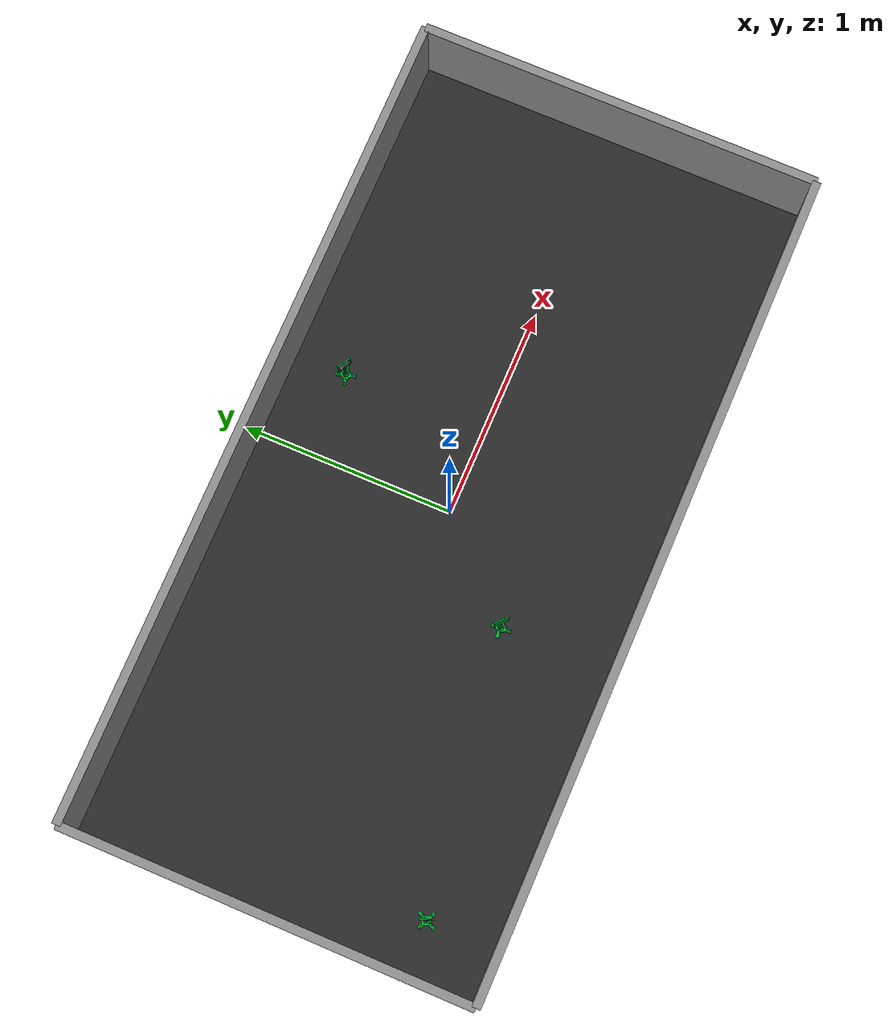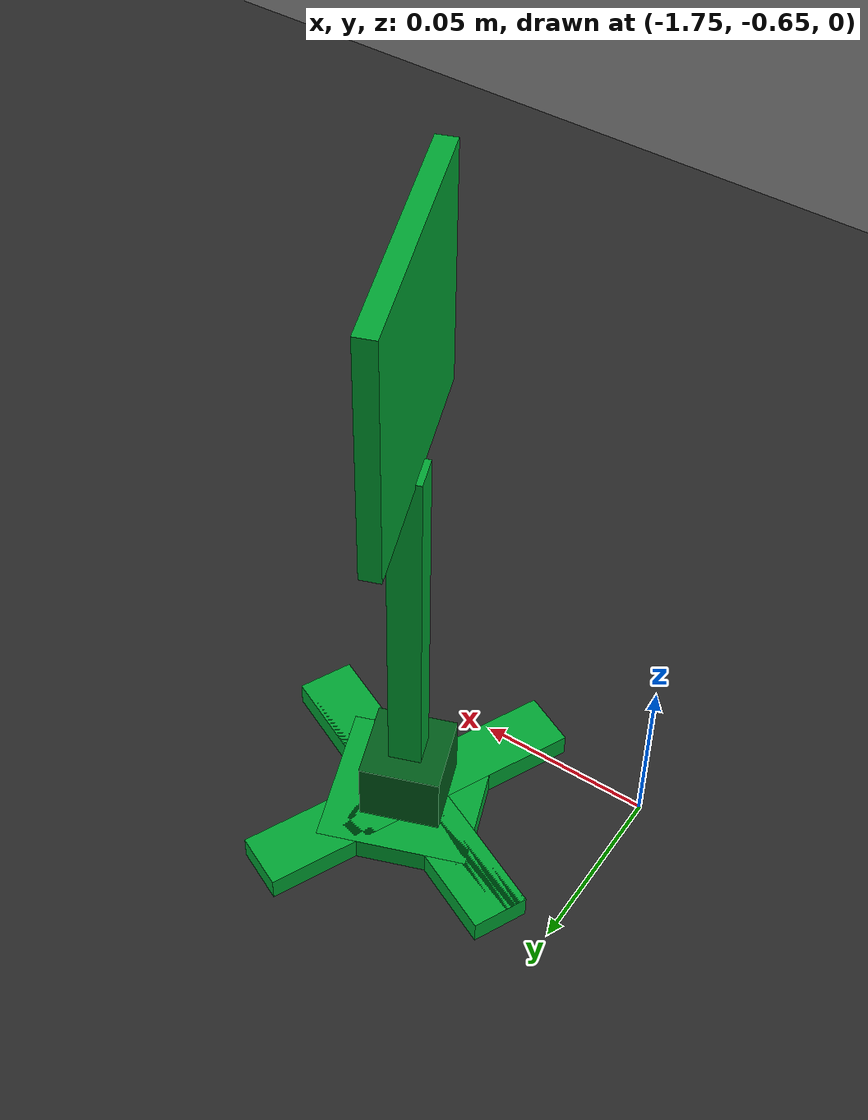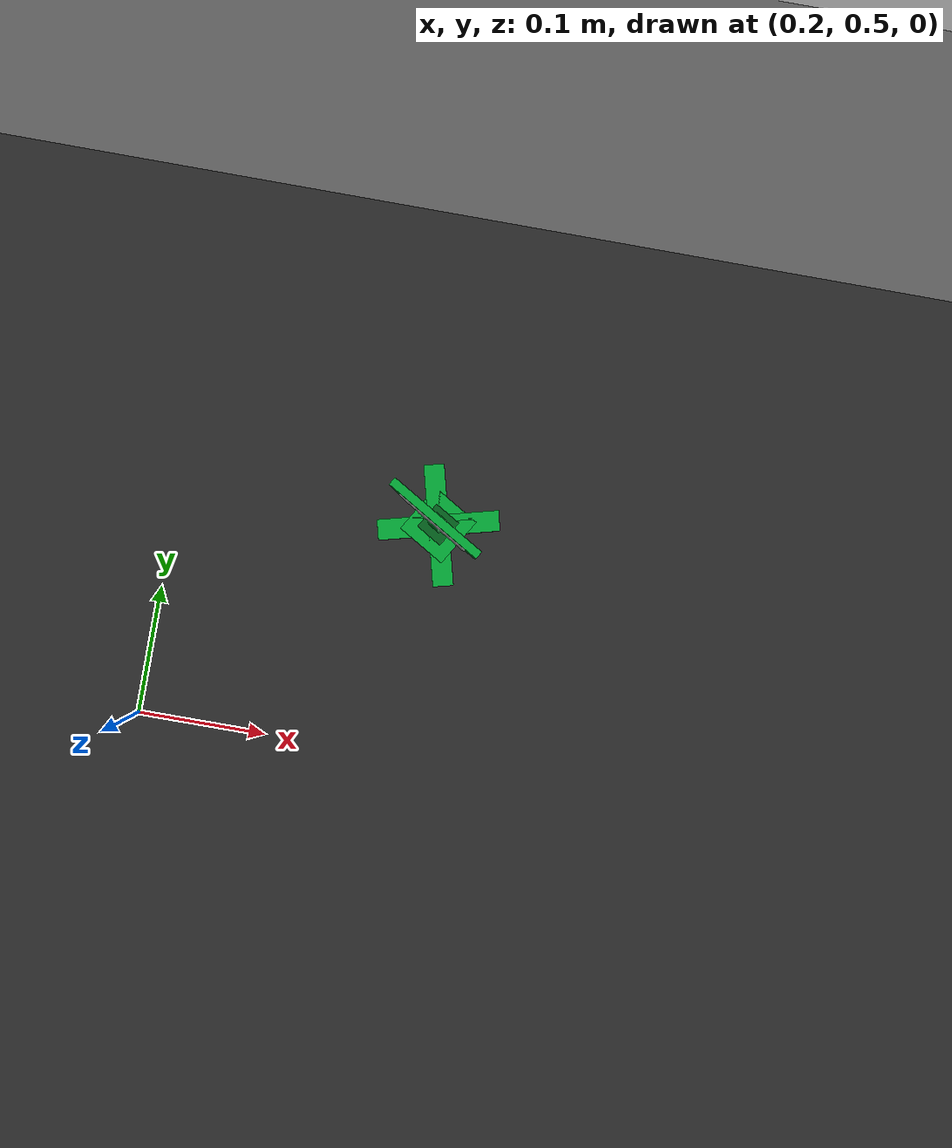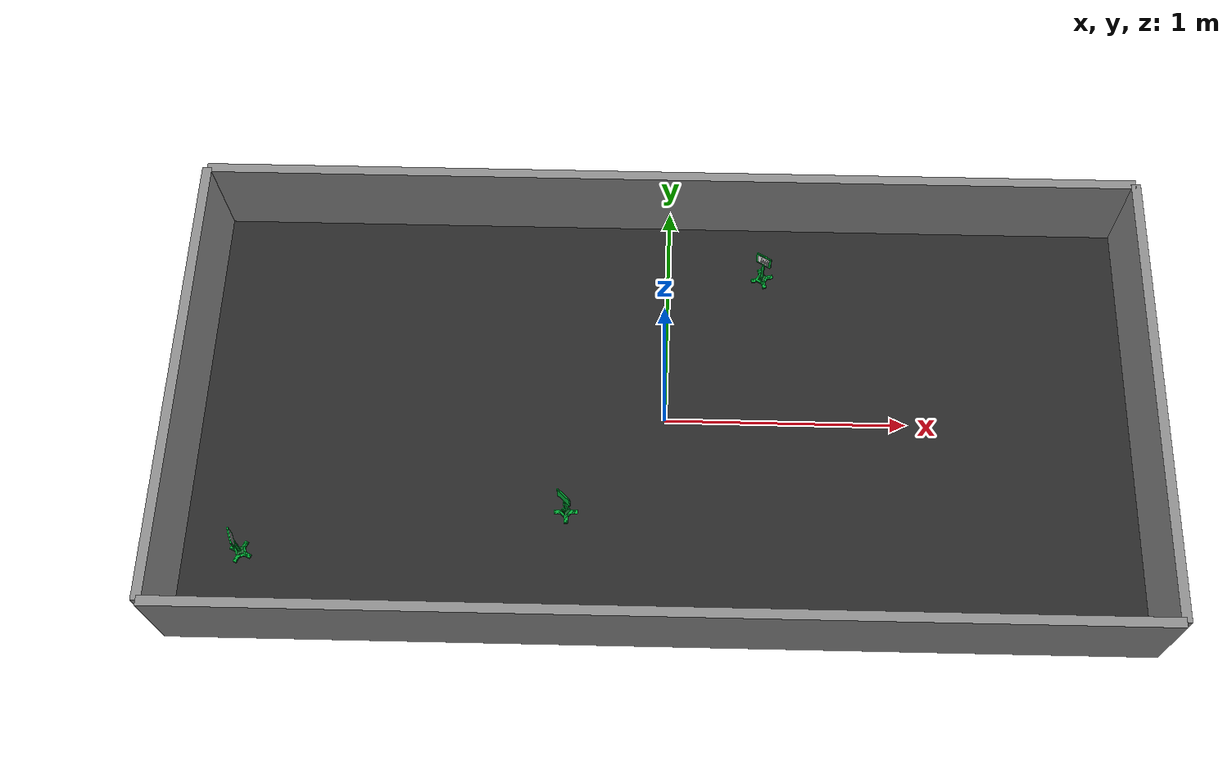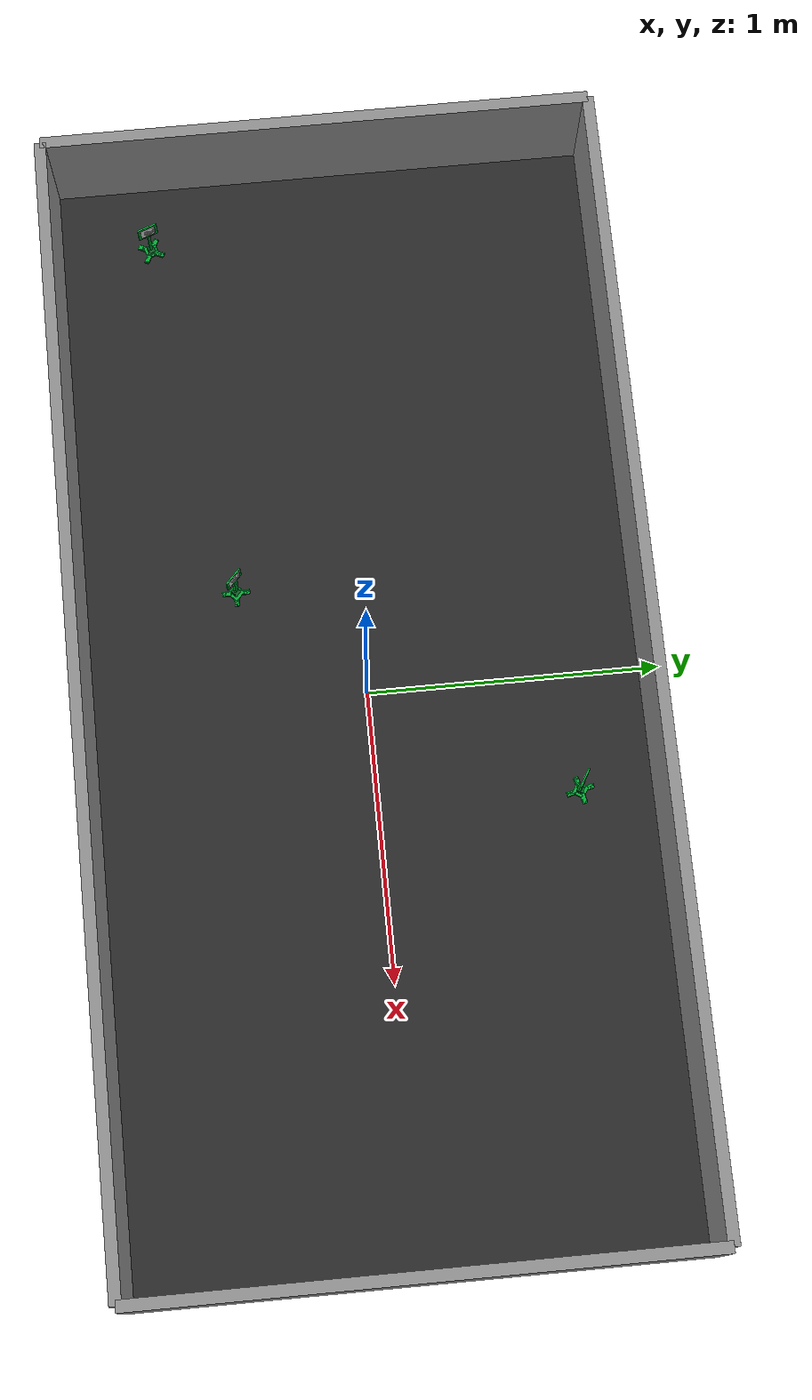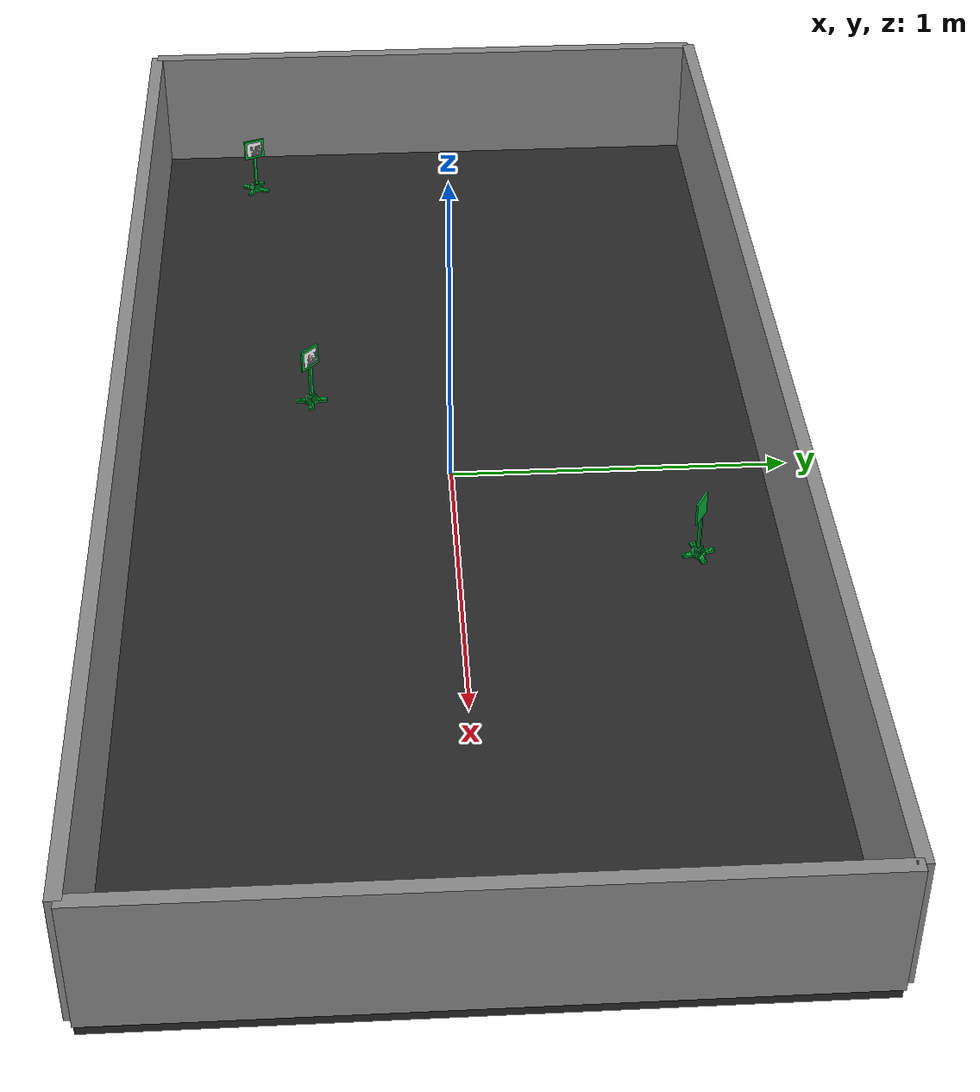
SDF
<?xml version="1.0" ?>
<sdf version="1.6">
  <world name="aufgabe04_stands">
    <gravity>0 0 -9.81</gravity>
    <physics name="default_physics" type="ode">
      <max_step_size>0.001</max_step_size>
      <real_time_factor>1</real_time_factor>
      <real_time_update_rate>1000</real_time_update_rate>
    </physics>
    <scene>
      <ambient>0.55 0.55 0.55 1</ambient>
      <background>0.75 0.75 0.75 1</background>
      <shadows>true</shadows>
    </scene>
    <light name="sun" type="directional">
      <cast_shadows>true</cast_shadows>
      <pose>0 0 4 0.35 -0.45 0</pose>
      <diffuse>0.9 0.9 0.9 1</diffuse>
      <specular>0.2 0.2 0.2 1</specular>
      <direction>-0.3 0.2 -1.0</direction>
    </light>
    <model name="arena_floor">
      <static>true</static>
      <link name="floor_link">
        <visual name="floor_visual">
          <pose>0 0 -0.025 0 0 0</pose>
          <geometry><box><size>3.9 1.898 0.05</size></box></geometry>
          <material>
          <ambient>0.16 0.16 0.16 1</ambient>
          <diffuse>0.16 0.16 0.16 1</diffuse>
          <specular>0.08 0.08 0.08 1</specular>
        </material>
        </visual>
        <collision name="floor_collision">
          <pose>0 0 -0.025 0 0 0</pose>
          <geometry><box><size>3.9 1.898 0.05</size></box></geometry>
        </collision>
      </link>
    </model>
    <model name="arena_walls">
      <static>true</static>
      <link name="walls_link">
        <visual name="wall_left">
        <pose>-1.950000 0.000000 0.200000 0 0 0.000000</pose>
        <geometry><box><size>0.040000 1.898000 0.400000</size></box></geometry>
        <material>
          <ambient>0.55 0.55 0.55 1</ambient>
          <diffuse>0.55 0.55 0.55 1</diffuse>
          <specular>0.08 0.08 0.08 1</specular>
        </material>
      </visual>
        <visual name="wall_right">
        <pose>1.950000 0.000000 0.200000 0 0 0.000000</pose>
        <geometry><box><size>0.040000 1.898000 0.400000</size></box></geometry>
        <material>
          <ambient>0.55 0.55 0.55 1</ambient>
          <diffuse>0.55 0.55 0.55 1</diffuse>
          <specular>0.08 0.08 0.08 1</specular>
        </material>
      </visual>
        <visual name="wall_front">
        <pose>0.000000 -0.949000 0.200000 0 0 0.000000</pose>
        <geometry><box><size>3.900000 0.040000 0.400000</size></box></geometry>
        <material>
          <ambient>0.55 0.55 0.55 1</ambient>
          <diffuse>0.55 0.55 0.55 1</diffuse>
          <specular>0.08 0.08 0.08 1</specular>
        </material>
      </visual>
        <visual name="wall_back">
        <pose>0.000000 0.949000 0.200000 0 0 0.000000</pose>
        <geometry><box><size>3.900000 0.040000 0.400000</size></box></geometry>
        <material>
          <ambient>0.55 0.55 0.55 1</ambient>
          <diffuse>0.55 0.55 0.55 1</diffuse>
          <specular>0.08 0.08 0.08 1</specular>
        </material>
      </visual>
        <collision name="wall_left">
        <pose>-1.950000 0.000000 0.200000 0 0 0.000000</pose>
        <geometry><box><size>0.040000 1.898000 0.400000</size></box></geometry>
      </collision>
        <collision name="wall_right">
        <pose>1.950000 0.000000 0.200000 0 0 0.000000</pose>
        <geometry><box><size>0.040000 1.898000 0.400000</size></box></geometry>
      </collision>
        <collision name="wall_front">
        <pose>0.000000 -0.949000 0.200000 0 0 0.000000</pose>
        <geometry><box><size>3.900000 0.040000 0.400000</size></box></geometry>
      </collision>
        <collision name="wall_back">
        <pose>0.000000 0.949000 0.200000 0 0 0.000000</pose>
        <geometry><box><size>3.900000 0.040000 0.400000</size></box></geometry>
      </collision>
      </link>
    </model>
  <model name="station_A">
    <pose>-0.395000 -0.415000 0.000000 0 0 0.810085</pose>
    <static>true</static>
    <self_collide>false</self_collide>
    <link name="stand_link">
      <visual name="base_center">
        <pose>0.000000 0.000000 0.003497 0 0 0.000000</pose>
        <geometry><box><size>0.041958 0.041958 0.006993</size></box></geometry>
        <material>
          <ambient>0.0 0.65 0.20 1</ambient>
          <diffuse>0.0 0.65 0.20 1</diffuse>
          <specular>0.08 0.08 0.08 1</specular>
        </material>
      </visual> <visual name="neck">
        <pose>0.000000 0.000000 0.014685 0 0 0.000000</pose>
        <geometry><box><size>0.022378 0.022378 0.022378</size></box></geometry>
        <material>
          <ambient>0.0 0.36 0.10 1</ambient>
          <diffuse>0.0 0.36 0.10 1</diffuse>
          <specular>0.08 0.08 0.08 1</specular>
        </material>
      </visual> <visual name="stem">
        <pose>0.000000 0.000000 0.074126 0 0 0.000000</pose>
        <geometry><box><size>0.009091 0.009091 0.114685</size></box></geometry>
        <material>
          <ambient>0.0 0.65 0.20 1</ambient>
          <diffuse>0.0 0.65 0.20 1</diffuse>
          <specular>0.08 0.08 0.08 1</specular>
        </material>
      </visual> <visual name="head_board">
        <pose>0.000000 0.000000 0.165035 0 0 0.000000</pose>
        <geometry><box><size>0.005594 0.069930 0.069930</size></box></geometry>
        <material>
          <ambient>0.0 0.65 0.20 1</ambient>
          <diffuse>0.0 0.65 0.20 1</diffuse>
          <specular>0.08 0.08 0.08 1</specular>
        </material>
      </visual> <visual name="base_arm_0">
        <pose>0.000000 0.000000 0.003497 0 0 0.785398</pose>
        <geometry><box><size>0.095105 0.016084 0.006993</size></box></geometry>
        <material>
          <ambient>0.0 0.65 0.20 1</ambient>
          <diffuse>0.0 0.65 0.20 1</diffuse>
          <specular>0.08 0.08 0.08 1</specular>
        </material>
      </visual> <visual name="base_arm_1">
        <pose>0.000000 0.000000 0.003497 0 0 2.356194</pose>
        <geometry><box><size>0.095105 0.016084 0.006993</size></box></geometry>
        <material>
          <ambient>0.0 0.65 0.20 1</ambient>
          <diffuse>0.0 0.65 0.20 1</diffuse>
          <specular>0.08 0.08 0.08 1</specular>
        </material>
      </visual> <visual name="base_arm_2">
        <pose>0.000000 0.000000 0.003497 0 0 3.926991</pose>
        <geometry><box><size>0.095105 0.016084 0.006993</size></box></geometry>
        <material>
          <ambient>0.0 0.65 0.20 1</ambient>
          <diffuse>0.0 0.65 0.20 1</diffuse>
          <specular>0.08 0.08 0.08 1</specular>
        </material>
      </visual> <visual name="base_arm_3">
        <pose>0.000000 0.000000 0.003497 0 0 5.497787</pose>
        <geometry><box><size>0.095105 0.016084 0.006993</size></box></geometry>
        <material>
          <ambient>0.0 0.65 0.20 1</ambient>
          <diffuse>0.0 0.65 0.20 1</diffuse>
          <specular>0.08 0.08 0.08 1</specular>
        </material>
      </visual> <visual name="qr_white_panel">
        <pose>0.003217 0.000000 0.165035 0 0 0.000000</pose>
        <geometry><box><size>0.000559 0.053147 0.053147</size></box></geometry>
        <material>
          <ambient>0.96 0.96 0.96 1</ambient>
          <diffuse>0.96 0.96 0.96 1</diffuse>
          <specular>0.08 0.08 0.08 1</specular>
        </material>
      </visual>
      <visual name="qr_00_00">
        <pose>0.003636 -0.011912 0.176947 0 0 0.000000</pose>
        <geometry><box><size>0.000280 0.001833 0.001833</size></box></geometry>
        <material>
          <ambient>0.01 0.01 0.01 1</ambient>
          <diffuse>0.01 0.01 0.01 1</diffuse>
          <specular>0.08 0.08 0.08 1</specular>
        </material>
      </visual>
      <visual name="qr_00_01">
        <pose>0.003636 -0.010080 0.176947 0 0 0.000000</pose>
        <geometry><box><size>0.000280 0.001833 0.001833</size></box></geometry>
        <material>
          <ambient>0.01 0.01 0.01 1</ambient>
          <diffuse>0.01 0.01 0.01 1</diffuse>
          <specular>0.08 0.08 0.08 1</specular>
        </material>
      </visual>
      <visual name="qr_00_02">
        <pose>0.003636 -0.008247 0.176947 0 0 0.000000</pose>
        <geometry><box><size>0.000280 0.001833 0.001833</size></box></geometry>
        <material>
          <ambient>0.01 0.01 0.01 1</ambient>
          <diffuse>0.01 0.01 0.01 1</diffuse>
          <specular>0.08 0.08 0.08 1</specular>
        </material>
      </visual>
      <visual name="qr_00_03">
        <pose>0.003636 -0.006414 0.176947 0 0 0.000000</pose>
        <geometry><box><size>0.000280 0.001833 0.001833</size></box></geometry>
        <material>
          <ambient>0.01 0.01 0.01 1</ambient>
          <diffuse>0.01 0.01 0.01 1</diffuse>
          <specular>0.08 0.08 0.08 1</specular>
        </material>
      </visual>
      <visual name="qr_00_04">
        <pose>0.003636 -0.004582 0.176947 0 0 0.000000</pose>
        <geometry><box><size>0.000280 0.001833 0.001833</size></box></geometry>
        <material>
          <ambient>0.01 0.01 0.01 1</ambient>
          <diffuse>0.01 0.01 0.01 1</diffuse>
          <specular>0.08 0.08 0.08 1</specular>
        </material>
      </visual>
      <visual name="qr_00_05">
        <pose>0.003636 -0.002749 0.176947 0 0 0.000000</pose>
        <geometry><box><size>0.000280 0.001833 0.001833</size></box></geometry>
        <material>
          <ambient>0.01 0.01 0.01 1</ambient>
          <diffuse>0.01 0.01 0.01 1</diffuse>
          <specular>0.08 0.08 0.08 1</specular>
        </material>
      </visual>
      <visual name="qr_00_06">
        <pose>0.003636 -0.000916 0.176947 0 0 0.000000</pose>
        <geometry><box><size>0.000280 0.001833 0.001833</size></box></geometry>
        <material>
          <ambient>0.01 0.01 0.01 1</ambient>
          <diffuse>0.01 0.01 0.01 1</diffuse>
          <specular>0.08 0.08 0.08 1</specular>
        </material>
      </visual>
      <visual name="qr_00_10">
        <pose>0.003636 0.006414 0.176947 0 0 0.000000</pose>
        <geometry><box><size>0.000280 0.001833 0.001833</size></box></geometry>
        <material>
          <ambient>0.01 0.01 0.01 1</ambient>
          <diffuse>0.01 0.01 0.01 1</diffuse>
          <specular>0.08 0.08 0.08 1</specular>
        </material>
      </visual>
      <visual name="qr_00_12">
        <pose>0.003636 0.010080 0.176947 0 0 0.000000</pose>
        <geometry><box><size>0.000280 0.001833 0.001833</size></box></geometry>
        <material>
          <ambient>0.01 0.01 0.01 1</ambient>
          <diffuse>0.01 0.01 0.01 1</diffuse>
          <specular>0.08 0.08 0.08 1</specular>
        </material>
      </visual>
      <visual name="qr_00_14">
        <pose>0.003636 0.013745 0.176947 0 0 0.000000</pose>
        <geometry><box><size>0.000280 0.001833 0.001833</size></box></geometry>
        <material>
          <ambient>0.01 0.01 0.01 1</ambient>
          <diffuse>0.01 0.01 0.01 1</diffuse>
          <specular>0.08 0.08 0.08 1</specular>
        </material>
      </visual>
      <visual name="qr_00_15">
        <pose>0.003636 0.015578 0.176947 0 0 0.000000</pose>
        <geometry><box><size>0.000280 0.001833 0.001833</size></box></geometry>
        <material>
          <ambient>0.01 0.01 0.01 1</ambient>
          <diffuse>0.01 0.01 0.01 1</diffuse>
          <specular>0.08 0.08 0.08 1</specular>
        </material>
      </visual>
      <visual name="qr_00_16">
        <pose>0.003636 0.017410 0.176947 0 0 0.000000</pose>
        <geometry><box><size>0.000280 0.001833 0.001833</size></box></geometry>
        <material>
          <ambient>0.01 0.01 0.01 1</ambient>
          <diffuse>0.01 0.01 0.01 1</diffuse>
          <specular>0.08 0.08 0.08 1</specular>
        </material>
      </visual>
      <visual name="qr_00_17">
        <pose>0.003636 0.019243 0.176947 0 0 0.000000</pose>
        <geometry><box><size>0.000280 0.001833 0.001833</size></box></geometry>
        <material>
          <ambient>0.01 0.01 0.01 1</ambient>
          <diffuse>0.01 0.01 0.01 1</diffuse>
          <specular>0.08 0.08 0.08 1</specular>
        </material>
      </visual>
      <visual name="qr_00_18">
        <pose>0.003636 0.021075 0.176947 0 0 0.000000</pose>
        <geometry><box><size>0.000280 0.001833 0.001833</size></box></geometry>
        <material>
          <ambient>0.01 0.01 0.01 1</ambient>
          <diffuse>0.01 0.01 0.01 1</diffuse>
          <specular>0.08 0.08 0.08 1</specular>
        </material>
      </visual>
      <visual name="qr_00_19">
        <pose>0.003636 0.022908 0.176947 0 0 0.000000</pose>
        <geometry><box><size>0.000280 0.001833 0.001833</size></box></geometry>
        <material>
          <ambient>0.01 0.01 0.01 1</ambient>
          <diffuse>0.01 0.01 0.01 1</diffuse>
          <specular>0.08 0.08 0.08 1</specular>
        </material>
      </visual>
      <visual name="qr_00_20">
        <pose>0.003636 0.024741 0.176947 0 0 0.000000</pose>
        <geometry><box><size>0.000280 0.001833 0.001833</size></box></geometry>
        <material>
          <ambient>0.01 0.01 0.01 1</ambient>
          <diffuse>0.01 0.01 0.01 1</diffuse>
          <specular>0.08 0.08 0.08 1</specular>
        </material>
      </visual>
      <visual name="qr_01_00">
        <pose>0.003636 -0.011912 0.175115 0 0 0.000000</pose>
        <geometry><box><size>0.000280 0.001833 0.001833</size></box></geometry>
        <material>
          <ambient>0.01 0.01 0.01 1</ambient>
          <diffuse>0.01 0.01 0.01 1</diffuse>
          <specular>0.08 0.08 0.08 1</specular>
        </material>
      </visual>
      <visual name="qr_01_06">
        <pose>0.003636 -0.000916 0.175115 0 0 0.000000</pose>
        <geometry><box><size>0.000280 0.001833 0.001833</size></box></geometry>
        <material>
          <ambient>0.01 0.01 0.01 1</ambient>
          <diffuse>0.01 0.01 0.01 1</diffuse>
          <specular>0.08 0.08 0.08 1</specular>
        </material>
      </visual>
      <visual name="qr_01_12">
        <pose>0.003636 0.010080 0.175115 0 0 0.000000</pose>
        <geometry><box><size>0.000280 0.001833 0.001833</size></box></geometry>
        <material>
          <ambient>0.01 0.01 0.01 1</ambient>
          <diffuse>0.01 0.01 0.01 1</diffuse>
          <specular>0.08 0.08 0.08 1</specular>
        </material>
      </visual>
      <visual name="qr_01_14">
        <pose>0.003636 0.013745 0.175115 0 0 0.000000</pose>
        <geometry><box><size>0.000280 0.001833 0.001833</size></box></geometry>
        <material>
          <ambient>0.01 0.01 0.01 1</ambient>
          <diffuse>0.01 0.01 0.01 1</diffuse>
          <specular>0.08 0.08 0.08 1</specular>
        </material>
      </visual>
      <visual name="qr_01_20">
        <pose>0.003636 0.024741 0.175115 0 0 0.000000</pose>
        <geometry><box><size>0.000280 0.001833 0.001833</size></box></geometry>
        <material>
          <ambient>0.01 0.01 0.01 1</ambient>
          <diffuse>0.01 0.01 0.01 1</diffuse>
          <specular>0.08 0.08 0.08 1</specular>
        </material>
      </visual>
      <visual name="qr_02_00">
        <pose>0.003636 -0.011912 0.173282 0 0 0.000000</pose>
        <geometry><box><size>0.000280 0.001833 0.001833</size></box></geometry>
        <material>
          <ambient>0.01 0.01 0.01 1</ambient>
          <diffuse>0.01 0.01 0.01 1</diffuse>
          <specular>0.08 0.08 0.08 1</specular>
        </material>
      </visual>
      <visual name="qr_02_02">
        <pose>0.003636 -0.008247 0.173282 0 0 0.000000</pose>
        <geometry><box><size>0.000280 0.001833 0.001833</size></box></geometry>
        <material>
          <ambient>0.01 0.01 0.01 1</ambient>
          <diffuse>0.01 0.01 0.01 1</diffuse>
          <specular>0.08 0.08 0.08 1</specular>
        </material>
      </visual>
      <visual name="qr_02_03">
        <pose>0.003636 -0.006414 0.173282 0 0 0.000000</pose>
        <geometry><box><size>0.000280 0.001833 0.001833</size></box></geometry>
        <material>
          <ambient>0.01 0.01 0.01 1</ambient>
          <diffuse>0.01 0.01 0.01 1</diffuse>
          <specular>0.08 0.08 0.08 1</specular>
        </material>
      </visual>
      <visual name="qr_02_04">
        <pose>0.003636 -0.004582 0.173282 0 0 0.000000</pose>
        <geometry><box><size>0.000280 0.001833 0.001833</size></box></geometry>
        <material>
          <ambient>0.01 0.01 0.01 1</ambient>
          <diffuse>0.01 0.01 0.01 1</diffuse>
          <specular>0.08 0.08 0.08 1</specular>
        </material>
      </visual>
      <visual name="qr_02_06">
        <pose>0.003636 -0.000916 0.173282 0 0 0.000000</pose>
        <geometry><box><size>0.000280 0.001833 0.001833</size></box></geometry>
        <material>
          <ambient>0.01 0.01 0.01 1</ambient>
          <diffuse>0.01 0.01 0.01 1</diffuse>
          <specular>0.08 0.08 0.08 1</specular>
        </material>
      </visual>
      <visual name="qr_02_08">
        <pose>0.003636 0.002749 0.173282 0 0 0.000000</pose>
        <geometry><box><size>0.000280 0.001833 0.001833</size></box></geometry>
        <material>
          <ambient>0.01 0.01 0.01 1</ambient>
          <diffuse>0.01 0.01 0.01 1</diffuse>
          <specular>0.08 0.08 0.08 1</specular>
        </material>
      </visual>
      <visual name="qr_02_10">
        <pose>0.003636 0.006414 0.173282 0 0 0.000000</pose>
        <geometry><box><size>0.000280 0.001833 0.001833</size></box></geometry>
        <material>
          <ambient>0.01 0.01 0.01 1</ambient>
          <diffuse>0.01 0.01 0.01 1</diffuse>
          <specular>0.08 0.08 0.08 1</specular>
        </material>
      </visual>
      <visual name="qr_02_14">
        <pose>0.003636 0.013745 0.173282 0 0 0.000000</pose>
        <geometry><box><size>0.000280 0.001833 0.001833</size></box></geometry>
        <material>
          <ambient>0.01 0.01 0.01 1</ambient>
          <diffuse>0.01 0.01 0.01 1</diffuse>
          <specular>0.08 0.08 0.08 1</specular>
        </material>
      </visual>
      <visual name="qr_02_16">
        <pose>0.003636 0.017410 0.173282 0 0 0.000000</pose>
        <geometry><box><size>0.000280 0.001833 0.001833</size></box></geometry>
        <material>
          <ambient>0.01 0.01 0.01 1</ambient>
          <diffuse>0.01 0.01 0.01 1</diffuse>
          <specular>0.08 0.08 0.08 1</specular>
        </material>
      </visual>
      <visual name="qr_02_17">
        <pose>0.003636 0.019243 0.173282 0 0 0.000000</pose>
        <geometry><box><size>0.000280 0.001833 0.001833</size></box></geometry>
        <material>
          <ambient>0.01 0.01 0.01 1</ambient>
          <diffuse>0.01 0.01 0.01 1</diffuse>
          <specular>0.08 0.08 0.08 1</specular>
        </material>
      </visual>
      <visual name="qr_02_18">
        <pose>0.003636 0.021075 0.173282 0 0 0.000000</pose>
        <geometry><box><size>0.000280 0.001833 0.001833</size></box></geometry>
        <material>
          <ambient>0.01 0.01 0.01 1</ambient>
          <diffuse>0.01 0.01 0.01 1</diffuse>
          <specular>0.08 0.08 0.08 1</specular>
        </material>
      </visual>
      <visual name="qr_02_20">
        <pose>0.003636 0.024741 0.173282 0 0 0.000000</pose>
        <geometry><box><size>0.000280 0.001833 0.001833</size></box></geometry>
        <material>
          <ambient>0.01 0.01 0.01 1</ambient>
          <diffuse>0.01 0.01 0.01 1</diffuse>
          <specular>0.08 0.08 0.08 1</specular>
        </material>
      </visual>
      <visual name="qr_03_00">
        <pose>0.003636 -0.011912 0.171449 0 0 0.000000</pose>
        <geometry><box><size>0.000280 0.001833 0.001833</size></box></geometry>
        <material>
          <ambient>0.01 0.01 0.01 1</ambient>
          <diffuse>0.01 0.01 0.01 1</diffuse>
          <specular>0.08 0.08 0.08 1</specular>
        </material>
      </visual>
      <visual name="qr_03_02">
        <pose>0.003636 -0.008247 0.171449 0 0 0.000000</pose>
        <geometry><box><size>0.000280 0.001833 0.001833</size></box></geometry>
        <material>
          <ambient>0.01 0.01 0.01 1</ambient>
          <diffuse>0.01 0.01 0.01 1</diffuse>
          <specular>0.08 0.08 0.08 1</specular>
        </material>
      </visual>
      <visual name="qr_03_03">
        <pose>0.003636 -0.006414 0.171449 0 0 0.000000</pose>
        <geometry><box><size>0.000280 0.001833 0.001833</size></box></geometry>
        <material>
          <ambient>0.01 0.01 0.01 1</ambient>
          <diffuse>0.01 0.01 0.01 1</diffuse>
          <specular>0.08 0.08 0.08 1</specular>
        </material>
      </visual>
      <visual name="qr_03_04">
        <pose>0.003636 -0.004582 0.171449 0 0 0.000000</pose>
        <geometry><box><size>0.000280 0.001833 0.001833</size></box></geometry>
        <material>
          <ambient>0.01 0.01 0.01 1</ambient>
          <diffuse>0.01 0.01 0.01 1</diffuse>
          <specular>0.08 0.08 0.08 1</specular>
        </material>
      </visual>
      <visual name="qr_03_06">
        <pose>0.003636 -0.000916 0.171449 0 0 0.000000</pose>
        <geometry><box><size>0.000280 0.001833 0.001833</size></box></geometry>
        <material>
          <ambient>0.01 0.01 0.01 1</ambient>
          <diffuse>0.01 0.01 0.01 1</diffuse>
          <specular>0.08 0.08 0.08 1</specular>
        </material>
      </visual>
      <visual name="qr_03_12">
        <pose>0.003636 0.010080 0.171449 0 0 0.000000</pose>
        <geometry><box><size>0.000280 0.001833 0.001833</size></box></geometry>
        <material>
          <ambient>0.01 0.01 0.01 1</ambient>
          <diffuse>0.01 0.01 0.01 1</diffuse>
          <specular>0.08 0.08 0.08 1</specular>
        </material>
      </visual>
      <visual name="qr_03_14">
        <pose>0.003636 0.013745 0.171449 0 0 0.000000</pose>
        <geometry><box><size>0.000280 0.001833 0.001833</size></box></geometry>
        <material>
          <ambient>0.01 0.01 0.01 1</ambient>
          <diffuse>0.01 0.01 0.01 1</diffuse>
          <specular>0.08 0.08 0.08 1</specular>
        </material>
      </visual>
      <visual name="qr_03_16">
        <pose>0.003636 0.017410 0.171449 0 0 0.000000</pose>
        <geometry><box><size>0.000280 0.001833 0.001833</size></box></geometry>
        <material>
          <ambient>0.01 0.01 0.01 1</ambient>
          <diffuse>0.01 0.01 0.01 1</diffuse>
          <specular>0.08 0.08 0.08 1</specular>
        </material>
      </visual>
      <visual name="qr_03_17">
        <pose>0.003636 0.019243 0.171449 0 0 0.000000</pose>
        <geometry><box><size>0.000280 0.001833 0.001833</size></box></geometry>
        <material>
          <ambient>0.01 0.01 0.01 1</ambient>
          <diffuse>0.01 0.01 0.01 1</diffuse>
          <specular>0.08 0.08 0.08 1</specular>
        </material>
      </visual>
      <visual name="qr_03_18">
        <pose>0.003636 0.021075 0.171449 0 0 0.000000</pose>
        <geometry><box><size>0.000280 0.001833 0.001833</size></box></geometry>
        <material>
          <ambient>0.01 0.01 0.01 1</ambient>
          <diffuse>0.01 0.01 0.01 1</diffuse>
          <specular>0.08 0.08 0.08 1</specular>
        </material>
      </visual>
      <visual name="qr_03_20">
        <pose>0.003636 0.024741 0.171449 0 0 0.000000</pose>
        <geometry><box><size>0.000280 0.001833 0.001833</size></box></geometry>
        <material>
          <ambient>0.01 0.01 0.01 1</ambient>
          <diffuse>0.01 0.01 0.01 1</diffuse>
          <specular>0.08 0.08 0.08 1</specular>
        </material>
      </visual>
      <visual name="qr_04_00">
        <pose>0.003636 -0.011912 0.169617 0 0 0.000000</pose>
        <geometry><box><size>0.000280 0.001833 0.001833</size></box></geometry>
        <material>
          <ambient>0.01 0.01 0.01 1</ambient>
          <diffuse>0.01 0.01 0.01 1</diffuse>
          <specular>0.08 0.08 0.08 1</specular>
        </material>
      </visual>
      <visual name="qr_04_02">
        <pose>0.003636 -0.008247 0.169617 0 0 0.000000</pose>
        <geometry><box><size>0.000280 0.001833 0.001833</size></box></geometry>
        <material>
          <ambient>0.01 0.01 0.01 1</ambient>
          <diffuse>0.01 0.01 0.01 1</diffuse>
          <specular>0.08 0.08 0.08 1</specular>
        </material>
      </visual>
      <visual name="qr_04_03">
        <pose>0.003636 -0.006414 0.169617 0 0 0.000000</pose>
        <geometry><box><size>0.000280 0.001833 0.001833</size></box></geometry>
        <material>
          <ambient>0.01 0.01 0.01 1</ambient>
          <diffuse>0.01 0.01 0.01 1</diffuse>
          <specular>0.08 0.08 0.08 1</specular>
        </material>
      </visual>
      <visual name="qr_04_04">
        <pose>0.003636 -0.004582 0.169617 0 0 0.000000</pose>
        <geometry><box><size>0.000280 0.001833 0.001833</size></box></geometry>
        <material>
          <ambient>0.01 0.01 0.01 1</ambient>
          <diffuse>0.01 0.01 0.01 1</diffuse>
          <specular>0.08 0.08 0.08 1</specular>
        </material>
      </visual>
      <visual name="qr_04_06">
        <pose>0.003636 -0.000916 0.169617 0 0 0.000000</pose>
        <geometry><box><size>0.000280 0.001833 0.001833</size></box></geometry>
        <material>
          <ambient>0.01 0.01 0.01 1</ambient>
          <diffuse>0.01 0.01 0.01 1</diffuse>
          <specular>0.08 0.08 0.08 1</specular>
        </material>
      </visual>
      <visual name="qr_04_11">
        <pose>0.003636 0.008247 0.169617 0 0 0.000000</pose>
        <geometry><box><size>0.000280 0.001833 0.001833</size></box></geometry>
        <material>
          <ambient>0.01 0.01 0.01 1</ambient>
          <diffuse>0.01 0.01 0.01 1</diffuse>
          <specular>0.08 0.08 0.08 1</specular>
        </material>
      </visual>
      <visual name="qr_04_12">
        <pose>0.003636 0.010080 0.169617 0 0 0.000000</pose>
        <geometry><box><size>0.000280 0.001833 0.001833</size></box></geometry>
        <material>
          <ambient>0.01 0.01 0.01 1</ambient>
          <diffuse>0.01 0.01 0.01 1</diffuse>
          <specular>0.08 0.08 0.08 1</specular>
        </material>
      </visual>
      <visual name="qr_04_14">
        <pose>0.003636 0.013745 0.169617 0 0 0.000000</pose>
        <geometry><box><size>0.000280 0.001833 0.001833</size></box></geometry>
        <material>
          <ambient>0.01 0.01 0.01 1</ambient>
          <diffuse>0.01 0.01 0.01 1</diffuse>
          <specular>0.08 0.08 0.08 1</specular>
        </material>
      </visual>
      <visual name="qr_04_16">
        <pose>0.003636 0.017410 0.169617 0 0 0.000000</pose>
        <geometry><box><size>0.000280 0.001833 0.001833</size></box></geometry>
        <material>
          <ambient>0.01 0.01 0.01 1</ambient>
          <diffuse>0.01 0.01 0.01 1</diffuse>
          <specular>0.08 0.08 0.08 1</specular>
        </material>
      </visual>
      <visual name="qr_04_17">
        <pose>0.003636 0.019243 0.169617 0 0 0.000000</pose>
        <geometry><box><size>0.000280 0.001833 0.001833</size></box></geometry>
        <material>
          <ambient>0.01 0.01 0.01 1</ambient>
          <diffuse>0.01 0.01 0.01 1</diffuse>
          <specular>0.08 0.08 0.08 1</specular>
        </material>
      </visual>
      <visual name="qr_04_18">
        <pose>0.003636 0.021075 0.169617 0 0 0.000000</pose>
        <geometry><box><size>0.000280 0.001833 0.001833</size></box></geometry>
        <material>
          <ambient>0.01 0.01 0.01 1</ambient>
          <diffuse>0.01 0.01 0.01 1</diffuse>
          <specular>0.08 0.08 0.08 1</specular>
        </material>
      </visual>
      <visual name="qr_04_20">
        <pose>0.003636 0.024741 0.169617 0 0 0.000000</pose>
        <geometry><box><size>0.000280 0.001833 0.001833</size></box></geometry>
        <material>
          <ambient>0.01 0.01 0.01 1</ambient>
          <diffuse>0.01 0.01 0.01 1</diffuse>
          <specular>0.08 0.08 0.08 1</specular>
        </material>
      </visual>
      <visual name="qr_05_00">
        <pose>0.003636 -0.011912 0.167784 0 0 0.000000</pose>
        <geometry><box><size>0.000280 0.001833 0.001833</size></box></geometry>
        <material>
          <ambient>0.01 0.01 0.01 1</ambient>
          <diffuse>0.01 0.01 0.01 1</diffuse>
          <specular>0.08 0.08 0.08 1</specular>
        </material>
      </visual>
      <visual name="qr_05_06">
        <pose>0.003636 -0.000916 0.167784 0 0 0.000000</pose>
        <geometry><box><size>0.000280 0.001833 0.001833</size></box></geometry>
        <material>
          <ambient>0.01 0.01 0.01 1</ambient>
          <diffuse>0.01 0.01 0.01 1</diffuse>
          <specular>0.08 0.08 0.08 1</specular>
        </material>
      </visual>
      <visual name="qr_05_09">
        <pose>0.003636 0.004582 0.167784 0 0 0.000000</pose>
        <geometry><box><size>0.000280 0.001833 0.001833</size></box></geometry>
        <material>
          <ambient>0.01 0.01 0.01 1</ambient>
          <diffuse>0.01 0.01 0.01 1</diffuse>
          <specular>0.08 0.08 0.08 1</specular>
        </material>
      </visual>
      <visual name="qr_05_11">
        <pose>0.003636 0.008247 0.167784 0 0 0.000000</pose>
        <geometry><box><size>0.000280 0.001833 0.001833</size></box></geometry>
        <material>
          <ambient>0.01 0.01 0.01 1</ambient>
          <diffuse>0.01 0.01 0.01 1</diffuse>
          <specular>0.08 0.08 0.08 1</specular>
        </material>
      </visual>
      <visual name="qr_05_14">
        <pose>0.003636 0.013745 0.167784 0 0 0.000000</pose>
        <geometry><box><size>0.000280 0.001833 0.001833</size></box></geometry>
        <material>
          <ambient>0.01 0.01 0.01 1</ambient>
          <diffuse>0.01 0.01 0.01 1</diffuse>
          <specular>0.08 0.08 0.08 1</specular>
        </material>
      </visual>
      <visual name="qr_05_20">
        <pose>0.003636 0.024741 0.167784 0 0 0.000000</pose>
        <geometry><box><size>0.000280 0.001833 0.001833</size></box></geometry>
        <material>
          <ambient>0.01 0.01 0.01 1</ambient>
          <diffuse>0.01 0.01 0.01 1</diffuse>
          <specular>0.08 0.08 0.08 1</specular>
        </material>
      </visual>
      <visual name="qr_06_00">
        <pose>0.003636 -0.011912 0.165951 0 0 0.000000</pose>
        <geometry><box><size>0.000280 0.001833 0.001833</size></box></geometry>
        <material>
          <ambient>0.01 0.01 0.01 1</ambient>
          <diffuse>0.01 0.01 0.01 1</diffuse>
          <specular>0.08 0.08 0.08 1</specular>
        </material>
      </visual>
      <visual name="qr_06_01">
        <pose>0.003636 -0.010080 0.165951 0 0 0.000000</pose>
        <geometry><box><size>0.000280 0.001833 0.001833</size></box></geometry>
        <material>
          <ambient>0.01 0.01 0.01 1</ambient>
          <diffuse>0.01 0.01 0.01 1</diffuse>
          <specular>0.08 0.08 0.08 1</specular>
        </material>
      </visual>
      <visual name="qr_06_02">
        <pose>0.003636 -0.008247 0.165951 0 0 0.000000</pose>
        <geometry><box><size>0.000280 0.001833 0.001833</size></box></geometry>
        <material>
          <ambient>0.01 0.01 0.01 1</ambient>
          <diffuse>0.01 0.01 0.01 1</diffuse>
          <specular>0.08 0.08 0.08 1</specular>
        </material>
      </visual>
      <visual name="qr_06_03">
        <pose>0.003636 -0.006414 0.165951 0 0 0.000000</pose>
        <geometry><box><size>0.000280 0.001833 0.001833</size></box></geometry>
        <material>
          <ambient>0.01 0.01 0.01 1</ambient>
          <diffuse>0.01 0.01 0.01 1</diffuse>
          <specular>0.08 0.08 0.08 1</specular>
        </material>
      </visual>
      <visual name="qr_06_04">
        <pose>0.003636 -0.004582 0.165951 0 0 0.000000</pose>
        <geometry><box><size>0.000280 0.001833 0.001833</size></box></geometry>
        <material>
          <ambient>0.01 0.01 0.01 1</ambient>
          <diffuse>0.01 0.01 0.01 1</diffuse>
          <specular>0.08 0.08 0.08 1</specular>
        </material>
      </visual>
      <visual name="qr_06_05">
        <pose>0.003636 -0.002749 0.165951 0 0 0.000000</pose>
        <geometry><box><size>0.000280 0.001833 0.001833</size></box></geometry>
        <material>
          <ambient>0.01 0.01 0.01 1</ambient>
          <diffuse>0.01 0.01 0.01 1</diffuse>
          <specular>0.08 0.08 0.08 1</specular>
        </material>
      </visual>
      <visual name="qr_06_06">
        <pose>0.003636 -0.000916 0.165951 0 0 0.000000</pose>
        <geometry><box><size>0.000280 0.001833 0.001833</size></box></geometry>
        <material>
          <ambient>0.01 0.01 0.01 1</ambient>
          <diffuse>0.01 0.01 0.01 1</diffuse>
          <specular>0.08 0.08 0.08 1</specular>
        </material>
      </visual>
      <visual name="qr_06_08">
        <pose>0.003636 0.002749 0.165951 0 0 0.000000</pose>
        <geometry><box><size>0.000280 0.001833 0.001833</size></box></geometry>
        <material>
          <ambient>0.01 0.01 0.01 1</ambient>
          <diffuse>0.01 0.01 0.01 1</diffuse>
          <specular>0.08 0.08 0.08 1</specular>
        </material>
      </visual>
      <visual name="qr_06_10">
        <pose>0.003636 0.006414 0.165951 0 0 0.000000</pose>
        <geometry><box><size>0.000280 0.001833 0.001833</size></box></geometry>
        <material>
          <ambient>0.01 0.01 0.01 1</ambient>
          <diffuse>0.01 0.01 0.01 1</diffuse>
          <specular>0.08 0.08 0.08 1</specular>
        </material>
      </visual>
      <visual name="qr_06_12">
        <pose>0.003636 0.010080 0.165951 0 0 0.000000</pose>
        <geometry><box><size>0.000280 0.001833 0.001833</size></box></geometry>
        <material>
          <ambient>0.01 0.01 0.01 1</ambient>
          <diffuse>0.01 0.01 0.01 1</diffuse>
          <specular>0.08 0.08 0.08 1</specular>
        </material>
      </visual>
      <visual name="qr_06_14">
        <pose>0.003636 0.013745 0.165951 0 0 0.000000</pose>
        <geometry><box><size>0.000280 0.001833 0.001833</size></box></geometry>
        <material>
          <ambient>0.01 0.01 0.01 1</ambient>
          <diffuse>0.01 0.01 0.01 1</diffuse>
          <specular>0.08 0.08 0.08 1</specular>
        </material>
      </visual>
      <visual name="qr_06_15">
        <pose>0.003636 0.015578 0.165951 0 0 0.000000</pose>
        <geometry><box><size>0.000280 0.001833 0.001833</size></box></geometry>
        <material>
          <ambient>0.01 0.01 0.01 1</ambient>
          <diffuse>0.01 0.01 0.01 1</diffuse>
          <specular>0.08 0.08 0.08 1</specular>
        </material>
      </visual>
      <visual name="qr_06_16">
        <pose>0.003636 0.017410 0.165951 0 0 0.000000</pose>
        <geometry><box><size>0.000280 0.001833 0.001833</size></box></geometry>
        <material>
          <ambient>0.01 0.01 0.01 1</ambient>
          <diffuse>0.01 0.01 0.01 1</diffuse>
          <specular>0.08 0.08 0.08 1</specular>
        </material>
      </visual>
      <visual name="qr_06_17">
        <pose>0.003636 0.019243 0.165951 0 0 0.000000</pose>
        <geometry><box><size>0.000280 0.001833 0.001833</size></box></geometry>
        <material>
          <ambient>0.01 0.01 0.01 1</ambient>
          <diffuse>0.01 0.01 0.01 1</diffuse>
          <specular>0.08 0.08 0.08 1</specular>
        </material>
      </visual>
      <visual name="qr_06_18">
        <pose>0.003636 0.021075 0.165951 0 0 0.000000</pose>
        <geometry><box><size>0.000280 0.001833 0.001833</size></box></geometry>
        <material>
          <ambient>0.01 0.01 0.01 1</ambient>
          <diffuse>0.01 0.01 0.01 1</diffuse>
          <specular>0.08 0.08 0.08 1</specular>
        </material>
      </visual>
      <visual name="qr_06_19">
        <pose>0.003636 0.022908 0.165951 0 0 0.000000</pose>
        <geometry><box><size>0.000280 0.001833 0.001833</size></box></geometry>
        <material>
          <ambient>0.01 0.01 0.01 1</ambient>
          <diffuse>0.01 0.01 0.01 1</diffuse>
          <specular>0.08 0.08 0.08 1</specular>
        </material>
      </visual>
      <visual name="qr_06_20">
        <pose>0.003636 0.024741 0.165951 0 0 0.000000</pose>
        <geometry><box><size>0.000280 0.001833 0.001833</size></box></geometry>
        <material>
          <ambient>0.01 0.01 0.01 1</ambient>
          <diffuse>0.01 0.01 0.01 1</diffuse>
          <specular>0.08 0.08 0.08 1</specular>
        </material>
      </visual>
      <visual name="qr_07_08">
        <pose>0.003636 0.002749 0.164119 0 0 0.000000</pose>
        <geometry><box><size>0.000280 0.001833 0.001833</size></box></geometry>
        <material>
          <ambient>0.01 0.01 0.01 1</ambient>
          <diffuse>0.01 0.01 0.01 1</diffuse>
          <specular>0.08 0.08 0.08 1</specular>
        </material>
      </visual>
      <visual name="qr_08_00">
        <pose>0.003636 -0.011912 0.162286 0 0 0.000000</pose>
        <geometry><box><size>0.000280 0.001833 0.001833</size></box></geometry>
        <material>
          <ambient>0.01 0.01 0.01 1</ambient>
          <diffuse>0.01 0.01 0.01 1</diffuse>
          <specular>0.08 0.08 0.08 1</specular>
        </material>
      </visual>
      <visual name="qr_08_01">
        <pose>0.003636 -0.010080 0.162286 0 0 0.000000</pose>
        <geometry><box><size>0.000280 0.001833 0.001833</size></box></geometry>
        <material>
          <ambient>0.01 0.01 0.01 1</ambient>
          <diffuse>0.01 0.01 0.01 1</diffuse>
          <specular>0.08 0.08 0.08 1</specular>
        </material>
      </visual>
      <visual name="qr_08_02">
        <pose>0.003636 -0.008247 0.162286 0 0 0.000000</pose>
        <geometry><box><size>0.000280 0.001833 0.001833</size></box></geometry>
        <material>
          <ambient>0.01 0.01 0.01 1</ambient>
          <diffuse>0.01 0.01 0.01 1</diffuse>
          <specular>0.08 0.08 0.08 1</specular>
        </material>
      </visual>
      <visual name="qr_08_04">
        <pose>0.003636 -0.004582 0.162286 0 0 0.000000</pose>
        <geometry><box><size>0.000280 0.001833 0.001833</size></box></geometry>
        <material>
          <ambient>0.01 0.01 0.01 1</ambient>
          <diffuse>0.01 0.01 0.01 1</diffuse>
          <specular>0.08 0.08 0.08 1</specular>
        </material>
      </visual>
      <visual name="qr_08_05">
        <pose>0.003636 -0.002749 0.162286 0 0 0.000000</pose>
        <geometry><box><size>0.000280 0.001833 0.001833</size></box></geometry>
        <material>
          <ambient>0.01 0.01 0.01 1</ambient>
          <diffuse>0.01 0.01 0.01 1</diffuse>
          <specular>0.08 0.08 0.08 1</specular>
        </material>
      </visual>
      <visual name="qr_08_06">
        <pose>0.003636 -0.000916 0.162286 0 0 0.000000</pose>
        <geometry><box><size>0.000280 0.001833 0.001833</size></box></geometry>
        <material>
          <ambient>0.01 0.01 0.01 1</ambient>
          <diffuse>0.01 0.01 0.01 1</diffuse>
          <specular>0.08 0.08 0.08 1</specular>
        </material>
      </visual>
      <visual name="qr_08_07">
        <pose>0.003636 0.000916 0.162286 0 0 0.000000</pose>
        <geometry><box><size>0.000280 0.001833 0.001833</size></box></geometry>
        <material>
          <ambient>0.01 0.01 0.01 1</ambient>
          <diffuse>0.01 0.01 0.01 1</diffuse>
          <specular>0.08 0.08 0.08 1</specular>
        </material>
      </visual>
      <visual name="qr_08_08">
        <pose>0.003636 0.002749 0.162286 0 0 0.000000</pose>
        <geometry><box><size>0.000280 0.001833 0.001833</size></box></geometry>
        <material>
          <ambient>0.01 0.01 0.01 1</ambient>
          <diffuse>0.01 0.01 0.01 1</diffuse>
          <specular>0.08 0.08 0.08 1</specular>
        </material>
      </visual>
      <visual name="qr_08_10">
        <pose>0.003636 0.006414 0.162286 0 0 0.000000</pose>
        <geometry><box><size>0.000280 0.001833 0.001833</size></box></geometry>
        <material>
          <ambient>0.01 0.01 0.01 1</ambient>
          <diffuse>0.01 0.01 0.01 1</diffuse>
          <specular>0.08 0.08 0.08 1</specular>
        </material>
      </visual>
      <visual name="qr_08_12">
        <pose>0.003636 0.010080 0.162286 0 0 0.000000</pose>
        <geometry><box><size>0.000280 0.001833 0.001833</size></box></geometry>
        <material>
          <ambient>0.01 0.01 0.01 1</ambient>
          <diffuse>0.01 0.01 0.01 1</diffuse>
          <specular>0.08 0.08 0.08 1</specular>
        </material>
      </visual>
      <visual name="qr_08_13">
        <pose>0.003636 0.011912 0.162286 0 0 0.000000</pose>
        <geometry><box><size>0.000280 0.001833 0.001833</size></box></geometry>
        <material>
          <ambient>0.01 0.01 0.01 1</ambient>
          <diffuse>0.01 0.01 0.01 1</diffuse>
          <specular>0.08 0.08 0.08 1</specular>
        </material>
      </visual>
      <visual name="qr_08_14">
        <pose>0.003636 0.013745 0.162286 0 0 0.000000</pose>
        <geometry><box><size>0.000280 0.001833 0.001833</size></box></geometry>
        <material>
          <ambient>0.01 0.01 0.01 1</ambient>
          <diffuse>0.01 0.01 0.01 1</diffuse>
          <specular>0.08 0.08 0.08 1</specular>
        </material>
      </visual>
      <visual name="qr_08_18">
        <pose>0.003636 0.021075 0.162286 0 0 0.000000</pose>
        <geometry><box><size>0.000280 0.001833 0.001833</size></box></geometry>
        <material>
          <ambient>0.01 0.01 0.01 1</ambient>
          <diffuse>0.01 0.01 0.01 1</diffuse>
          <specular>0.08 0.08 0.08 1</specular>
        </material>
      </visual>
      <visual name="qr_09_01">
        <pose>0.003636 -0.010080 0.160453 0 0 0.000000</pose>
        <geometry><box><size>0.000280 0.001833 0.001833</size></box></geometry>
        <material>
          <ambient>0.01 0.01 0.01 1</ambient>
          <diffuse>0.01 0.01 0.01 1</diffuse>
          <specular>0.08 0.08 0.08 1</specular>
        </material>
      </visual>
      <visual name="qr_09_03">
        <pose>0.003636 -0.006414 0.160453 0 0 0.000000</pose>
        <geometry><box><size>0.000280 0.001833 0.001833</size></box></geometry>
        <material>
          <ambient>0.01 0.01 0.01 1</ambient>
          <diffuse>0.01 0.01 0.01 1</diffuse>
          <specular>0.08 0.08 0.08 1</specular>
        </material>
      </visual>
      <visual name="qr_09_05">
        <pose>0.003636 -0.002749 0.160453 0 0 0.000000</pose>
        <geometry><box><size>0.000280 0.001833 0.001833</size></box></geometry>
        <material>
          <ambient>0.01 0.01 0.01 1</ambient>
          <diffuse>0.01 0.01 0.01 1</diffuse>
          <specular>0.08 0.08 0.08 1</specular>
        </material>
      </visual>
      <visual name="qr_09_08">
        <pose>0.003636 0.002749 0.160453 0 0 0.000000</pose>
        <geometry><box><size>0.000280 0.001833 0.001833</size></box></geometry>
        <material>
          <ambient>0.01 0.01 0.01 1</ambient>
          <diffuse>0.01 0.01 0.01 1</diffuse>
          <specular>0.08 0.08 0.08 1</specular>
        </material>
      </visual>
      <visual name="qr_09_10">
        <pose>0.003636 0.006414 0.160453 0 0 0.000000</pose>
        <geometry><box><size>0.000280 0.001833 0.001833</size></box></geometry>
        <material>
          <ambient>0.01 0.01 0.01 1</ambient>
          <diffuse>0.01 0.01 0.01 1</diffuse>
          <specular>0.08 0.08 0.08 1</specular>
        </material>
      </visual>
      <visual name="qr_09_11">
        <pose>0.003636 0.008247 0.160453 0 0 0.000000</pose>
        <geometry><box><size>0.000280 0.001833 0.001833</size></box></geometry>
        <material>
          <ambient>0.01 0.01 0.01 1</ambient>
          <diffuse>0.01 0.01 0.01 1</diffuse>
          <specular>0.08 0.08 0.08 1</specular>
        </material>
      </visual>
      <visual name="qr_09_13">
        <pose>0.003636 0.011912 0.160453 0 0 0.000000</pose>
        <geometry><box><size>0.000280 0.001833 0.001833</size></box></geometry>
        <material>
          <ambient>0.01 0.01 0.01 1</ambient>
          <diffuse>0.01 0.01 0.01 1</diffuse>
          <specular>0.08 0.08 0.08 1</specular>
        </material>
      </visual>
      <visual name="qr_09_15">
        <pose>0.003636 0.015578 0.160453 0 0 0.000000</pose>
        <geometry><box><size>0.000280 0.001833 0.001833</size></box></geometry>
        <material>
          <ambient>0.01 0.01 0.01 1</ambient>
          <diffuse>0.01 0.01 0.01 1</diffuse>
          <specular>0.08 0.08 0.08 1</specular>
        </material>
      </visual>
      <visual name="qr_09_16">
        <pose>0.003636 0.017410 0.160453 0 0 0.000000</pose>
        <geometry><box><size>0.000280 0.001833 0.001833</size></box></geometry>
        <material>
          <ambient>0.01 0.01 0.01 1</ambient>
          <diffuse>0.01 0.01 0.01 1</diffuse>
          <specular>0.08 0.08 0.08 1</specular>
        </material>
      </visual>
      <visual name="qr_09_18">
        <pose>0.003636 0.021075 0.160453 0 0 0.000000</pose>
        <geometry><box><size>0.000280 0.001833 0.001833</size></box></geometry>
        <material>
          <ambient>0.01 0.01 0.01 1</ambient>
          <diffuse>0.01 0.01 0.01 1</diffuse>
          <specular>0.08 0.08 0.08 1</specular>
        </material>
      </visual>
      <visual name="qr_09_19">
        <pose>0.003636 0.022908 0.160453 0 0 0.000000</pose>
        <geometry><box><size>0.000280 0.001833 0.001833</size></box></geometry>
        <material>
          <ambient>0.01 0.01 0.01 1</ambient>
          <diffuse>0.01 0.01 0.01 1</diffuse>
          <specular>0.08 0.08 0.08 1</specular>
        </material>
      </visual>
      <visual name="qr_10_00">
        <pose>0.003636 -0.011912 0.158621 0 0 0.000000</pose>
        <geometry><box><size>0.000280 0.001833 0.001833</size></box></geometry>
        <material>
          <ambient>0.01 0.01 0.01 1</ambient>
          <diffuse>0.01 0.01 0.01 1</diffuse>
          <specular>0.08 0.08 0.08 1</specular>
        </material>
      </visual>
      <visual name="qr_10_02">
        <pose>0.003636 -0.008247 0.158621 0 0 0.000000</pose>
        <geometry><box><size>0.000280 0.001833 0.001833</size></box></geometry>
        <material>
          <ambient>0.01 0.01 0.01 1</ambient>
          <diffuse>0.01 0.01 0.01 1</diffuse>
          <specular>0.08 0.08 0.08 1</specular>
        </material>
      </visual>
      <visual name="qr_10_04">
        <pose>0.003636 -0.004582 0.158621 0 0 0.000000</pose>
        <geometry><box><size>0.000280 0.001833 0.001833</size></box></geometry>
        <material>
          <ambient>0.01 0.01 0.01 1</ambient>
          <diffuse>0.01 0.01 0.01 1</diffuse>
          <specular>0.08 0.08 0.08 1</specular>
        </material>
      </visual>
      <visual name="qr_10_06">
        <pose>0.003636 -0.000916 0.158621 0 0 0.000000</pose>
        <geometry><box><size>0.000280 0.001833 0.001833</size></box></geometry>
        <material>
          <ambient>0.01 0.01 0.01 1</ambient>
          <diffuse>0.01 0.01 0.01 1</diffuse>
          <specular>0.08 0.08 0.08 1</specular>
        </material>
      </visual>
      <visual name="qr_10_07">
        <pose>0.003636 0.000916 0.158621 0 0 0.000000</pose>
        <geometry><box><size>0.000280 0.001833 0.001833</size></box></geometry>
        <material>
          <ambient>0.01 0.01 0.01 1</ambient>
          <diffuse>0.01 0.01 0.01 1</diffuse>
          <specular>0.08 0.08 0.08 1</specular>
        </material>
      </visual>
      <visual name="qr_10_11">
        <pose>0.003636 0.008247 0.158621 0 0 0.000000</pose>
        <geometry><box><size>0.000280 0.001833 0.001833</size></box></geometry>
        <material>
          <ambient>0.01 0.01 0.01 1</ambient>
          <diffuse>0.01 0.01 0.01 1</diffuse>
          <specular>0.08 0.08 0.08 1</specular>
        </material>
      </visual>
      <visual name="qr_10_13">
        <pose>0.003636 0.011912 0.158621 0 0 0.000000</pose>
        <geometry><box><size>0.000280 0.001833 0.001833</size></box></geometry>
        <material>
          <ambient>0.01 0.01 0.01 1</ambient>
          <diffuse>0.01 0.01 0.01 1</diffuse>
          <specular>0.08 0.08 0.08 1</specular>
        </material>
      </visual>
      <visual name="qr_10_14">
        <pose>0.003636 0.013745 0.158621 0 0 0.000000</pose>
        <geometry><box><size>0.000280 0.001833 0.001833</size></box></geometry>
        <material>
          <ambient>0.01 0.01 0.01 1</ambient>
          <diffuse>0.01 0.01 0.01 1</diffuse>
          <specular>0.08 0.08 0.08 1</specular>
        </material>
      </visual>
      <visual name="qr_10_15">
        <pose>0.003636 0.015578 0.158621 0 0 0.000000</pose>
        <geometry><box><size>0.000280 0.001833 0.001833</size></box></geometry>
        <material>
          <ambient>0.01 0.01 0.01 1</ambient>
          <diffuse>0.01 0.01 0.01 1</diffuse>
          <specular>0.08 0.08 0.08 1</specular>
        </material>
      </visual>
      <visual name="qr_10_18">
        <pose>0.003636 0.021075 0.158621 0 0 0.000000</pose>
        <geometry><box><size>0.000280 0.001833 0.001833</size></box></geometry>
        <material>
          <ambient>0.01 0.01 0.01 1</ambient>
          <diffuse>0.01 0.01 0.01 1</diffuse>
          <specular>0.08 0.08 0.08 1</specular>
        </material>
      </visual>
      <visual name="qr_10_20">
        <pose>0.003636 0.024741 0.158621 0 0 0.000000</pose>
        <geometry><box><size>0.000280 0.001833 0.001833</size></box></geometry>
        <material>
          <ambient>0.01 0.01 0.01 1</ambient>
          <diffuse>0.01 0.01 0.01 1</diffuse>
          <specular>0.08 0.08 0.08 1</specular>
        </material>
      </visual>
      <visual name="qr_11_01">
        <pose>0.003636 -0.010080 0.156788 0 0 0.000000</pose>
        <geometry><box><size>0.000280 0.001833 0.001833</size></box></geometry>
        <material>
          <ambient>0.01 0.01 0.01 1</ambient>
          <diffuse>0.01 0.01 0.01 1</diffuse>
          <specular>0.08 0.08 0.08 1</specular>
        </material>
      </visual>
      <visual name="qr_11_03">
        <pose>0.003636 -0.006414 0.156788 0 0 0.000000</pose>
        <geometry><box><size>0.000280 0.001833 0.001833</size></box></geometry>
        <material>
          <ambient>0.01 0.01 0.01 1</ambient>
          <diffuse>0.01 0.01 0.01 1</diffuse>
          <specular>0.08 0.08 0.08 1</specular>
        </material>
      </visual>
      <visual name="qr_11_05">
        <pose>0.003636 -0.002749 0.156788 0 0 0.000000</pose>
        <geometry><box><size>0.000280 0.001833 0.001833</size></box></geometry>
        <material>
          <ambient>0.01 0.01 0.01 1</ambient>
          <diffuse>0.01 0.01 0.01 1</diffuse>
          <specular>0.08 0.08 0.08 1</specular>
        </material>
      </visual>
      <visual name="qr_11_10">
        <pose>0.003636 0.006414 0.156788 0 0 0.000000</pose>
        <geometry><box><size>0.000280 0.001833 0.001833</size></box></geometry>
        <material>
          <ambient>0.01 0.01 0.01 1</ambient>
          <diffuse>0.01 0.01 0.01 1</diffuse>
          <specular>0.08 0.08 0.08 1</specular>
        </material>
      </visual>
      <visual name="qr_11_11">
        <pose>0.003636 0.008247 0.156788 0 0 0.000000</pose>
        <geometry><box><size>0.000280 0.001833 0.001833</size></box></geometry>
        <material>
          <ambient>0.01 0.01 0.01 1</ambient>
          <diffuse>0.01 0.01 0.01 1</diffuse>
          <specular>0.08 0.08 0.08 1</specular>
        </material>
      </visual>
      <visual name="qr_11_12">
        <pose>0.003636 0.010080 0.156788 0 0 0.000000</pose>
        <geometry><box><size>0.000280 0.001833 0.001833</size></box></geometry>
        <material>
          <ambient>0.01 0.01 0.01 1</ambient>
          <diffuse>0.01 0.01 0.01 1</diffuse>
          <specular>0.08 0.08 0.08 1</specular>
        </material>
      </visual>
      <visual name="qr_11_13">
        <pose>0.003636 0.011912 0.156788 0 0 0.000000</pose>
        <geometry><box><size>0.000280 0.001833 0.001833</size></box></geometry>
        <material>
          <ambient>0.01 0.01 0.01 1</ambient>
          <diffuse>0.01 0.01 0.01 1</diffuse>
          <specular>0.08 0.08 0.08 1</specular>
        </material>
      </visual>
      <visual name="qr_11_17">
        <pose>0.003636 0.019243 0.156788 0 0 0.000000</pose>
        <geometry><box><size>0.000280 0.001833 0.001833</size></box></geometry>
        <material>
          <ambient>0.01 0.01 0.01 1</ambient>
          <diffuse>0.01 0.01 0.01 1</diffuse>
          <specular>0.08 0.08 0.08 1</specular>
        </material>
      </visual>
      <visual name="qr_12_00">
        <pose>0.003636 -0.011912 0.154955 0 0 0.000000</pose>
        <geometry><box><size>0.000280 0.001833 0.001833</size></box></geometry>
        <material>
          <ambient>0.01 0.01 0.01 1</ambient>
          <diffuse>0.01 0.01 0.01 1</diffuse>
          <specular>0.08 0.08 0.08 1</specular>
        </material>
      </visual>
      <visual name="qr_12_02">
        <pose>0.003636 -0.008247 0.154955 0 0 0.000000</pose>
        <geometry><box><size>0.000280 0.001833 0.001833</size></box></geometry>
        <material>
          <ambient>0.01 0.01 0.01 1</ambient>
          <diffuse>0.01 0.01 0.01 1</diffuse>
          <specular>0.08 0.08 0.08 1</specular>
        </material>
      </visual>
      <visual name="qr_12_04">
        <pose>0.003636 -0.004582 0.154955 0 0 0.000000</pose>
        <geometry><box><size>0.000280 0.001833 0.001833</size></box></geometry>
        <material>
          <ambient>0.01 0.01 0.01 1</ambient>
          <diffuse>0.01 0.01 0.01 1</diffuse>
          <specular>0.08 0.08 0.08 1</specular>
        </material>
      </visual>
      <visual name="qr_12_06">
        <pose>0.003636 -0.000916 0.154955 0 0 0.000000</pose>
        <geometry><box><size>0.000280 0.001833 0.001833</size></box></geometry>
        <material>
          <ambient>0.01 0.01 0.01 1</ambient>
          <diffuse>0.01 0.01 0.01 1</diffuse>
          <specular>0.08 0.08 0.08 1</specular>
        </material>
      </visual>
      <visual name="qr_12_07">
        <pose>0.003636 0.000916 0.154955 0 0 0.000000</pose>
        <geometry><box><size>0.000280 0.001833 0.001833</size></box></geometry>
        <material>
          <ambient>0.01 0.01 0.01 1</ambient>
          <diffuse>0.01 0.01 0.01 1</diffuse>
          <specular>0.08 0.08 0.08 1</specular>
        </material>
      </visual>
      <visual name="qr_12_11">
        <pose>0.003636 0.008247 0.154955 0 0 0.000000</pose>
        <geometry><box><size>0.000280 0.001833 0.001833</size></box></geometry>
        <material>
          <ambient>0.01 0.01 0.01 1</ambient>
          <diffuse>0.01 0.01 0.01 1</diffuse>
          <specular>0.08 0.08 0.08 1</specular>
        </material>
      </visual>
      <visual name="qr_12_13">
        <pose>0.003636 0.011912 0.154955 0 0 0.000000</pose>
        <geometry><box><size>0.000280 0.001833 0.001833</size></box></geometry>
        <material>
          <ambient>0.01 0.01 0.01 1</ambient>
          <diffuse>0.01 0.01 0.01 1</diffuse>
          <specular>0.08 0.08 0.08 1</specular>
        </material>
      </visual>
      <visual name="qr_12_14">
        <pose>0.003636 0.013745 0.154955 0 0 0.000000</pose>
        <geometry><box><size>0.000280 0.001833 0.001833</size></box></geometry>
        <material>
          <ambient>0.01 0.01 0.01 1</ambient>
          <diffuse>0.01 0.01 0.01 1</diffuse>
          <specular>0.08 0.08 0.08 1</specular>
        </material>
      </visual>
      <visual name="qr_12_16">
        <pose>0.003636 0.017410 0.154955 0 0 0.000000</pose>
        <geometry><box><size>0.000280 0.001833 0.001833</size></box></geometry>
        <material>
          <ambient>0.01 0.01 0.01 1</ambient>
          <diffuse>0.01 0.01 0.01 1</diffuse>
          <specular>0.08 0.08 0.08 1</specular>
        </material>
      </visual>
      <visual name="qr_12_17">
        <pose>0.003636 0.019243 0.154955 0 0 0.000000</pose>
        <geometry><box><size>0.000280 0.001833 0.001833</size></box></geometry>
        <material>
          <ambient>0.01 0.01 0.01 1</ambient>
          <diffuse>0.01 0.01 0.01 1</diffuse>
          <specular>0.08 0.08 0.08 1</specular>
        </material>
      </visual>
      <visual name="qr_12_18">
        <pose>0.003636 0.021075 0.154955 0 0 0.000000</pose>
        <geometry><box><size>0.000280 0.001833 0.001833</size></box></geometry>
        <material>
          <ambient>0.01 0.01 0.01 1</ambient>
          <diffuse>0.01 0.01 0.01 1</diffuse>
          <specular>0.08 0.08 0.08 1</specular>
        </material>
      </visual>
      <visual name="qr_12_20">
        <pose>0.003636 0.024741 0.154955 0 0 0.000000</pose>
        <geometry><box><size>0.000280 0.001833 0.001833</size></box></geometry>
        <material>
          <ambient>0.01 0.01 0.01 1</ambient>
          <diffuse>0.01 0.01 0.01 1</diffuse>
          <specular>0.08 0.08 0.08 1</specular>
        </material>
      </visual>
      <visual name="qr_13_08">
        <pose>0.003636 0.002749 0.153123 0 0 0.000000</pose>
        <geometry><box><size>0.000280 0.001833 0.001833</size></box></geometry>
        <material>
          <ambient>0.01 0.01 0.01 1</ambient>
          <diffuse>0.01 0.01 0.01 1</diffuse>
          <specular>0.08 0.08 0.08 1</specular>
        </material>
      </visual>
      <visual name="qr_13_14">
        <pose>0.003636 0.013745 0.153123 0 0 0.000000</pose>
        <geometry><box><size>0.000280 0.001833 0.001833</size></box></geometry>
        <material>
          <ambient>0.01 0.01 0.01 1</ambient>
          <diffuse>0.01 0.01 0.01 1</diffuse>
          <specular>0.08 0.08 0.08 1</specular>
        </material>
      </visual>
      <visual name="qr_13_17">
        <pose>0.003636 0.019243 0.153123 0 0 0.000000</pose>
        <geometry><box><size>0.000280 0.001833 0.001833</size></box></geometry>
        <material>
          <ambient>0.01 0.01 0.01 1</ambient>
          <diffuse>0.01 0.01 0.01 1</diffuse>
          <specular>0.08 0.08 0.08 1</specular>
        </material>
      </visual>
      <visual name="qr_13_19">
        <pose>0.003636 0.022908 0.153123 0 0 0.000000</pose>
        <geometry><box><size>0.000280 0.001833 0.001833</size></box></geometry>
        <material>
          <ambient>0.01 0.01 0.01 1</ambient>
          <diffuse>0.01 0.01 0.01 1</diffuse>
          <specular>0.08 0.08 0.08 1</specular>
        </material>
      </visual>
      <visual name="qr_14_00">
        <pose>0.003636 -0.011912 0.151290 0 0 0.000000</pose>
        <geometry><box><size>0.000280 0.001833 0.001833</size></box></geometry>
        <material>
          <ambient>0.01 0.01 0.01 1</ambient>
          <diffuse>0.01 0.01 0.01 1</diffuse>
          <specular>0.08 0.08 0.08 1</specular>
        </material>
      </visual>
      <visual name="qr_14_01">
        <pose>0.003636 -0.010080 0.151290 0 0 0.000000</pose>
        <geometry><box><size>0.000280 0.001833 0.001833</size></box></geometry>
        <material>
          <ambient>0.01 0.01 0.01 1</ambient>
          <diffuse>0.01 0.01 0.01 1</diffuse>
          <specular>0.08 0.08 0.08 1</specular>
        </material>
      </visual>
      <visual name="qr_14_02">
        <pose>0.003636 -0.008247 0.151290 0 0 0.000000</pose>
        <geometry><box><size>0.000280 0.001833 0.001833</size></box></geometry>
        <material>
          <ambient>0.01 0.01 0.01 1</ambient>
          <diffuse>0.01 0.01 0.01 1</diffuse>
          <specular>0.08 0.08 0.08 1</specular>
        </material>
      </visual>
      <visual name="qr_14_03">
        <pose>0.003636 -0.006414 0.151290 0 0 0.000000</pose>
        <geometry><box><size>0.000280 0.001833 0.001833</size></box></geometry>
        <material>
          <ambient>0.01 0.01 0.01 1</ambient>
          <diffuse>0.01 0.01 0.01 1</diffuse>
          <specular>0.08 0.08 0.08 1</specular>
        </material>
      </visual>
      <visual name="qr_14_04">
        <pose>0.003636 -0.004582 0.151290 0 0 0.000000</pose>
        <geometry><box><size>0.000280 0.001833 0.001833</size></box></geometry>
        <material>
          <ambient>0.01 0.01 0.01 1</ambient>
          <diffuse>0.01 0.01 0.01 1</diffuse>
          <specular>0.08 0.08 0.08 1</specular>
        </material>
      </visual>
      <visual name="qr_14_05">
        <pose>0.003636 -0.002749 0.151290 0 0 0.000000</pose>
        <geometry><box><size>0.000280 0.001833 0.001833</size></box></geometry>
        <material>
          <ambient>0.01 0.01 0.01 1</ambient>
          <diffuse>0.01 0.01 0.01 1</diffuse>
          <specular>0.08 0.08 0.08 1</specular>
        </material>
      </visual>
      <visual name="qr_14_06">
        <pose>0.003636 -0.000916 0.151290 0 0 0.000000</pose>
        <geometry><box><size>0.000280 0.001833 0.001833</size></box></geometry>
        <material>
          <ambient>0.01 0.01 0.01 1</ambient>
          <diffuse>0.01 0.01 0.01 1</diffuse>
          <specular>0.08 0.08 0.08 1</specular>
        </material>
      </visual>
      <visual name="qr_14_08">
        <pose>0.003636 0.002749 0.151290 0 0 0.000000</pose>
        <geometry><box><size>0.000280 0.001833 0.001833</size></box></geometry>
        <material>
          <ambient>0.01 0.01 0.01 1</ambient>
          <diffuse>0.01 0.01 0.01 1</diffuse>
          <specular>0.08 0.08 0.08 1</specular>
        </material>
      </visual>
      <visual name="qr_14_09">
        <pose>0.003636 0.004582 0.151290 0 0 0.000000</pose>
        <geometry><box><size>0.000280 0.001833 0.001833</size></box></geometry>
        <material>
          <ambient>0.01 0.01 0.01 1</ambient>
          <diffuse>0.01 0.01 0.01 1</diffuse>
          <specular>0.08 0.08 0.08 1</specular>
        </material>
      </visual>
      <visual name="qr_14_10">
        <pose>0.003636 0.006414 0.151290 0 0 0.000000</pose>
        <geometry><box><size>0.000280 0.001833 0.001833</size></box></geometry>
        <material>
          <ambient>0.01 0.01 0.01 1</ambient>
          <diffuse>0.01 0.01 0.01 1</diffuse>
          <specular>0.08 0.08 0.08 1</specular>
        </material>
      </visual>
      <visual name="qr_14_12">
        <pose>0.003636 0.010080 0.151290 0 0 0.000000</pose>
        <geometry><box><size>0.000280 0.001833 0.001833</size></box></geometry>
        <material>
          <ambient>0.01 0.01 0.01 1</ambient>
          <diffuse>0.01 0.01 0.01 1</diffuse>
          <specular>0.08 0.08 0.08 1</specular>
        </material>
      </visual>
      <visual name="qr_14_16">
        <pose>0.003636 0.017410 0.151290 0 0 0.000000</pose>
        <geometry><box><size>0.000280 0.001833 0.001833</size></box></geometry>
        <material>
          <ambient>0.01 0.01 0.01 1</ambient>
          <diffuse>0.01 0.01 0.01 1</diffuse>
          <specular>0.08 0.08 0.08 1</specular>
        </material>
      </visual>
      <visual name="qr_14_17">
        <pose>0.003636 0.019243 0.151290 0 0 0.000000</pose>
        <geometry><box><size>0.000280 0.001833 0.001833</size></box></geometry>
        <material>
          <ambient>0.01 0.01 0.01 1</ambient>
          <diffuse>0.01 0.01 0.01 1</diffuse>
          <specular>0.08 0.08 0.08 1</specular>
        </material>
      </visual>
      <visual name="qr_14_18">
        <pose>0.003636 0.021075 0.151290 0 0 0.000000</pose>
        <geometry><box><size>0.000280 0.001833 0.001833</size></box></geometry>
        <material>
          <ambient>0.01 0.01 0.01 1</ambient>
          <diffuse>0.01 0.01 0.01 1</diffuse>
          <specular>0.08 0.08 0.08 1</specular>
        </material>
      </visual>
      <visual name="qr_14_19">
        <pose>0.003636 0.022908 0.151290 0 0 0.000000</pose>
        <geometry><box><size>0.000280 0.001833 0.001833</size></box></geometry>
        <material>
          <ambient>0.01 0.01 0.01 1</ambient>
          <diffuse>0.01 0.01 0.01 1</diffuse>
          <specular>0.08 0.08 0.08 1</specular>
        </material>
      </visual>
      <visual name="qr_14_20">
        <pose>0.003636 0.024741 0.151290 0 0 0.000000</pose>
        <geometry><box><size>0.000280 0.001833 0.001833</size></box></geometry>
        <material>
          <ambient>0.01 0.01 0.01 1</ambient>
          <diffuse>0.01 0.01 0.01 1</diffuse>
          <specular>0.08 0.08 0.08 1</specular>
        </material>
      </visual>
      <visual name="qr_15_00">
        <pose>0.003636 -0.011912 0.149457 0 0 0.000000</pose>
        <geometry><box><size>0.000280 0.001833 0.001833</size></box></geometry>
        <material>
          <ambient>0.01 0.01 0.01 1</ambient>
          <diffuse>0.01 0.01 0.01 1</diffuse>
          <specular>0.08 0.08 0.08 1</specular>
        </material>
      </visual>
      <visual name="qr_15_06">
        <pose>0.003636 -0.000916 0.149457 0 0 0.000000</pose>
        <geometry><box><size>0.000280 0.001833 0.001833</size></box></geometry>
        <material>
          <ambient>0.01 0.01 0.01 1</ambient>
          <diffuse>0.01 0.01 0.01 1</diffuse>
          <specular>0.08 0.08 0.08 1</specular>
        </material>
      </visual>
      <visual name="qr_15_08">
        <pose>0.003636 0.002749 0.149457 0 0 0.000000</pose>
        <geometry><box><size>0.000280 0.001833 0.001833</size></box></geometry>
        <material>
          <ambient>0.01 0.01 0.01 1</ambient>
          <diffuse>0.01 0.01 0.01 1</diffuse>
          <specular>0.08 0.08 0.08 1</specular>
        </material>
      </visual>
      <visual name="qr_15_14">
        <pose>0.003636 0.013745 0.149457 0 0 0.000000</pose>
        <geometry><box><size>0.000280 0.001833 0.001833</size></box></geometry>
        <material>
          <ambient>0.01 0.01 0.01 1</ambient>
          <diffuse>0.01 0.01 0.01 1</diffuse>
          <specular>0.08 0.08 0.08 1</specular>
        </material>
      </visual>
      <visual name="qr_15_15">
        <pose>0.003636 0.015578 0.149457 0 0 0.000000</pose>
        <geometry><box><size>0.000280 0.001833 0.001833</size></box></geometry>
        <material>
          <ambient>0.01 0.01 0.01 1</ambient>
          <diffuse>0.01 0.01 0.01 1</diffuse>
          <specular>0.08 0.08 0.08 1</specular>
        </material>
      </visual>
      <visual name="qr_15_18">
        <pose>0.003636 0.021075 0.149457 0 0 0.000000</pose>
        <geometry><box><size>0.000280 0.001833 0.001833</size></box></geometry>
        <material>
          <ambient>0.01 0.01 0.01 1</ambient>
          <diffuse>0.01 0.01 0.01 1</diffuse>
          <specular>0.08 0.08 0.08 1</specular>
        </material>
      </visual>
      <visual name="qr_16_00">
        <pose>0.003636 -0.011912 0.147625 0 0 0.000000</pose>
        <geometry><box><size>0.000280 0.001833 0.001833</size></box></geometry>
        <material>
          <ambient>0.01 0.01 0.01 1</ambient>
          <diffuse>0.01 0.01 0.01 1</diffuse>
          <specular>0.08 0.08 0.08 1</specular>
        </material>
      </visual>
      <visual name="qr_16_02">
        <pose>0.003636 -0.008247 0.147625 0 0 0.000000</pose>
        <geometry><box><size>0.000280 0.001833 0.001833</size></box></geometry>
        <material>
          <ambient>0.01 0.01 0.01 1</ambient>
          <diffuse>0.01 0.01 0.01 1</diffuse>
          <specular>0.08 0.08 0.08 1</specular>
        </material>
      </visual>
      <visual name="qr_16_03">
        <pose>0.003636 -0.006414 0.147625 0 0 0.000000</pose>
        <geometry><box><size>0.000280 0.001833 0.001833</size></box></geometry>
        <material>
          <ambient>0.01 0.01 0.01 1</ambient>
          <diffuse>0.01 0.01 0.01 1</diffuse>
          <specular>0.08 0.08 0.08 1</specular>
        </material>
      </visual>
      <visual name="qr_16_04">
        <pose>0.003636 -0.004582 0.147625 0 0 0.000000</pose>
        <geometry><box><size>0.000280 0.001833 0.001833</size></box></geometry>
        <material>
          <ambient>0.01 0.01 0.01 1</ambient>
          <diffuse>0.01 0.01 0.01 1</diffuse>
          <specular>0.08 0.08 0.08 1</specular>
        </material>
      </visual>
      <visual name="qr_16_06">
        <pose>0.003636 -0.000916 0.147625 0 0 0.000000</pose>
        <geometry><box><size>0.000280 0.001833 0.001833</size></box></geometry>
        <material>
          <ambient>0.01 0.01 0.01 1</ambient>
          <diffuse>0.01 0.01 0.01 1</diffuse>
          <specular>0.08 0.08 0.08 1</specular>
        </material>
      </visual>
      <visual name="qr_16_08">
        <pose>0.003636 0.002749 0.147625 0 0 0.000000</pose>
        <geometry><box><size>0.000280 0.001833 0.001833</size></box></geometry>
        <material>
          <ambient>0.01 0.01 0.01 1</ambient>
          <diffuse>0.01 0.01 0.01 1</diffuse>
          <specular>0.08 0.08 0.08 1</specular>
        </material>
      </visual>
      <visual name="qr_16_09">
        <pose>0.003636 0.004582 0.147625 0 0 0.000000</pose>
        <geometry><box><size>0.000280 0.001833 0.001833</size></box></geometry>
        <material>
          <ambient>0.01 0.01 0.01 1</ambient>
          <diffuse>0.01 0.01 0.01 1</diffuse>
          <specular>0.08 0.08 0.08 1</specular>
        </material>
      </visual>
      <visual name="qr_16_10">
        <pose>0.003636 0.006414 0.147625 0 0 0.000000</pose>
        <geometry><box><size>0.000280 0.001833 0.001833</size></box></geometry>
        <material>
          <ambient>0.01 0.01 0.01 1</ambient>
          <diffuse>0.01 0.01 0.01 1</diffuse>
          <specular>0.08 0.08 0.08 1</specular>
        </material>
      </visual>
      <visual name="qr_16_12">
        <pose>0.003636 0.010080 0.147625 0 0 0.000000</pose>
        <geometry><box><size>0.000280 0.001833 0.001833</size></box></geometry>
        <material>
          <ambient>0.01 0.01 0.01 1</ambient>
          <diffuse>0.01 0.01 0.01 1</diffuse>
          <specular>0.08 0.08 0.08 1</specular>
        </material>
      </visual>
      <visual name="qr_16_14">
        <pose>0.003636 0.013745 0.147625 0 0 0.000000</pose>
        <geometry><box><size>0.000280 0.001833 0.001833</size></box></geometry>
        <material>
          <ambient>0.01 0.01 0.01 1</ambient>
          <diffuse>0.01 0.01 0.01 1</diffuse>
          <specular>0.08 0.08 0.08 1</specular>
        </material>
      </visual>
      <visual name="qr_16_15">
        <pose>0.003636 0.015578 0.147625 0 0 0.000000</pose>
        <geometry><box><size>0.000280 0.001833 0.001833</size></box></geometry>
        <material>
          <ambient>0.01 0.01 0.01 1</ambient>
          <diffuse>0.01 0.01 0.01 1</diffuse>
          <specular>0.08 0.08 0.08 1</specular>
        </material>
      </visual>
      <visual name="qr_16_20">
        <pose>0.003636 0.024741 0.147625 0 0 0.000000</pose>
        <geometry><box><size>0.000280 0.001833 0.001833</size></box></geometry>
        <material>
          <ambient>0.01 0.01 0.01 1</ambient>
          <diffuse>0.01 0.01 0.01 1</diffuse>
          <specular>0.08 0.08 0.08 1</specular>
        </material>
      </visual>
      <visual name="qr_17_00">
        <pose>0.003636 -0.011912 0.145792 0 0 0.000000</pose>
        <geometry><box><size>0.000280 0.001833 0.001833</size></box></geometry>
        <material>
          <ambient>0.01 0.01 0.01 1</ambient>
          <diffuse>0.01 0.01 0.01 1</diffuse>
          <specular>0.08 0.08 0.08 1</specular>
        </material>
      </visual>
      <visual name="qr_17_02">
        <pose>0.003636 -0.008247 0.145792 0 0 0.000000</pose>
        <geometry><box><size>0.000280 0.001833 0.001833</size></box></geometry>
        <material>
          <ambient>0.01 0.01 0.01 1</ambient>
          <diffuse>0.01 0.01 0.01 1</diffuse>
          <specular>0.08 0.08 0.08 1</specular>
        </material>
      </visual>
      <visual name="qr_17_03">
        <pose>0.003636 -0.006414 0.145792 0 0 0.000000</pose>
        <geometry><box><size>0.000280 0.001833 0.001833</size></box></geometry>
        <material>
          <ambient>0.01 0.01 0.01 1</ambient>
          <diffuse>0.01 0.01 0.01 1</diffuse>
          <specular>0.08 0.08 0.08 1</specular>
        </material>
      </visual>
      <visual name="qr_17_04">
        <pose>0.003636 -0.004582 0.145792 0 0 0.000000</pose>
        <geometry><box><size>0.000280 0.001833 0.001833</size></box></geometry>
        <material>
          <ambient>0.01 0.01 0.01 1</ambient>
          <diffuse>0.01 0.01 0.01 1</diffuse>
          <specular>0.08 0.08 0.08 1</specular>
        </material>
      </visual>
      <visual name="qr_17_06">
        <pose>0.003636 -0.000916 0.145792 0 0 0.000000</pose>
        <geometry><box><size>0.000280 0.001833 0.001833</size></box></geometry>
        <material>
          <ambient>0.01 0.01 0.01 1</ambient>
          <diffuse>0.01 0.01 0.01 1</diffuse>
          <specular>0.08 0.08 0.08 1</specular>
        </material>
      </visual>
      <visual name="qr_17_09">
        <pose>0.003636 0.004582 0.145792 0 0 0.000000</pose>
        <geometry><box><size>0.000280 0.001833 0.001833</size></box></geometry>
        <material>
          <ambient>0.01 0.01 0.01 1</ambient>
          <diffuse>0.01 0.01 0.01 1</diffuse>
          <specular>0.08 0.08 0.08 1</specular>
        </material>
      </visual>
      <visual name="qr_17_11">
        <pose>0.003636 0.008247 0.145792 0 0 0.000000</pose>
        <geometry><box><size>0.000280 0.001833 0.001833</size></box></geometry>
        <material>
          <ambient>0.01 0.01 0.01 1</ambient>
          <diffuse>0.01 0.01 0.01 1</diffuse>
          <specular>0.08 0.08 0.08 1</specular>
        </material>
      </visual>
      <visual name="qr_17_13">
        <pose>0.003636 0.011912 0.145792 0 0 0.000000</pose>
        <geometry><box><size>0.000280 0.001833 0.001833</size></box></geometry>
        <material>
          <ambient>0.01 0.01 0.01 1</ambient>
          <diffuse>0.01 0.01 0.01 1</diffuse>
          <specular>0.08 0.08 0.08 1</specular>
        </material>
      </visual>
      <visual name="qr_17_15">
        <pose>0.003636 0.015578 0.145792 0 0 0.000000</pose>
        <geometry><box><size>0.000280 0.001833 0.001833</size></box></geometry>
        <material>
          <ambient>0.01 0.01 0.01 1</ambient>
          <diffuse>0.01 0.01 0.01 1</diffuse>
          <specular>0.08 0.08 0.08 1</specular>
        </material>
      </visual>
      <visual name="qr_17_16">
        <pose>0.003636 0.017410 0.145792 0 0 0.000000</pose>
        <geometry><box><size>0.000280 0.001833 0.001833</size></box></geometry>
        <material>
          <ambient>0.01 0.01 0.01 1</ambient>
          <diffuse>0.01 0.01 0.01 1</diffuse>
          <specular>0.08 0.08 0.08 1</specular>
        </material>
      </visual>
      <visual name="qr_17_18">
        <pose>0.003636 0.021075 0.145792 0 0 0.000000</pose>
        <geometry><box><size>0.000280 0.001833 0.001833</size></box></geometry>
        <material>
          <ambient>0.01 0.01 0.01 1</ambient>
          <diffuse>0.01 0.01 0.01 1</diffuse>
          <specular>0.08 0.08 0.08 1</specular>
        </material>
      </visual>
      <visual name="qr_17_19">
        <pose>0.003636 0.022908 0.145792 0 0 0.000000</pose>
        <geometry><box><size>0.000280 0.001833 0.001833</size></box></geometry>
        <material>
          <ambient>0.01 0.01 0.01 1</ambient>
          <diffuse>0.01 0.01 0.01 1</diffuse>
          <specular>0.08 0.08 0.08 1</specular>
        </material>
      </visual>
      <visual name="qr_18_00">
        <pose>0.003636 -0.011912 0.143959 0 0 0.000000</pose>
        <geometry><box><size>0.000280 0.001833 0.001833</size></box></geometry>
        <material>
          <ambient>0.01 0.01 0.01 1</ambient>
          <diffuse>0.01 0.01 0.01 1</diffuse>
          <specular>0.08 0.08 0.08 1</specular>
        </material>
      </visual>
      <visual name="qr_18_02">
        <pose>0.003636 -0.008247 0.143959 0 0 0.000000</pose>
        <geometry><box><size>0.000280 0.001833 0.001833</size></box></geometry>
        <material>
          <ambient>0.01 0.01 0.01 1</ambient>
          <diffuse>0.01 0.01 0.01 1</diffuse>
          <specular>0.08 0.08 0.08 1</specular>
        </material>
      </visual>
      <visual name="qr_18_03">
        <pose>0.003636 -0.006414 0.143959 0 0 0.000000</pose>
        <geometry><box><size>0.000280 0.001833 0.001833</size></box></geometry>
        <material>
          <ambient>0.01 0.01 0.01 1</ambient>
          <diffuse>0.01 0.01 0.01 1</diffuse>
          <specular>0.08 0.08 0.08 1</specular>
        </material>
      </visual>
      <visual name="qr_18_04">
        <pose>0.003636 -0.004582 0.143959 0 0 0.000000</pose>
        <geometry><box><size>0.000280 0.001833 0.001833</size></box></geometry>
        <material>
          <ambient>0.01 0.01 0.01 1</ambient>
          <diffuse>0.01 0.01 0.01 1</diffuse>
          <specular>0.08 0.08 0.08 1</specular>
        </material>
      </visual>
      <visual name="qr_18_06">
        <pose>0.003636 -0.000916 0.143959 0 0 0.000000</pose>
        <geometry><box><size>0.000280 0.001833 0.001833</size></box></geometry>
        <material>
          <ambient>0.01 0.01 0.01 1</ambient>
          <diffuse>0.01 0.01 0.01 1</diffuse>
          <specular>0.08 0.08 0.08 1</specular>
        </material>
      </visual>
      <visual name="qr_18_08">
        <pose>0.003636 0.002749 0.143959 0 0 0.000000</pose>
        <geometry><box><size>0.000280 0.001833 0.001833</size></box></geometry>
        <material>
          <ambient>0.01 0.01 0.01 1</ambient>
          <diffuse>0.01 0.01 0.01 1</diffuse>
          <specular>0.08 0.08 0.08 1</specular>
        </material>
      </visual>
      <visual name="qr_18_09">
        <pose>0.003636 0.004582 0.143959 0 0 0.000000</pose>
        <geometry><box><size>0.000280 0.001833 0.001833</size></box></geometry>
        <material>
          <ambient>0.01 0.01 0.01 1</ambient>
          <diffuse>0.01 0.01 0.01 1</diffuse>
          <specular>0.08 0.08 0.08 1</specular>
        </material>
      </visual>
      <visual name="qr_18_10">
        <pose>0.003636 0.006414 0.143959 0 0 0.000000</pose>
        <geometry><box><size>0.000280 0.001833 0.001833</size></box></geometry>
        <material>
          <ambient>0.01 0.01 0.01 1</ambient>
          <diffuse>0.01 0.01 0.01 1</diffuse>
          <specular>0.08 0.08 0.08 1</specular>
        </material>
      </visual>
      <visual name="qr_18_11">
        <pose>0.003636 0.008247 0.143959 0 0 0.000000</pose>
        <geometry><box><size>0.000280 0.001833 0.001833</size></box></geometry>
        <material>
          <ambient>0.01 0.01 0.01 1</ambient>
          <diffuse>0.01 0.01 0.01 1</diffuse>
          <specular>0.08 0.08 0.08 1</specular>
        </material>
      </visual>
      <visual name="qr_18_13">
        <pose>0.003636 0.011912 0.143959 0 0 0.000000</pose>
        <geometry><box><size>0.000280 0.001833 0.001833</size></box></geometry>
        <material>
          <ambient>0.01 0.01 0.01 1</ambient>
          <diffuse>0.01 0.01 0.01 1</diffuse>
          <specular>0.08 0.08 0.08 1</specular>
        </material>
      </visual>
      <visual name="qr_18_14">
        <pose>0.003636 0.013745 0.143959 0 0 0.000000</pose>
        <geometry><box><size>0.000280 0.001833 0.001833</size></box></geometry>
        <material>
          <ambient>0.01 0.01 0.01 1</ambient>
          <diffuse>0.01 0.01 0.01 1</diffuse>
          <specular>0.08 0.08 0.08 1</specular>
        </material>
      </visual>
      <visual name="qr_18_15">
        <pose>0.003636 0.015578 0.143959 0 0 0.000000</pose>
        <geometry><box><size>0.000280 0.001833 0.001833</size></box></geometry>
        <material>
          <ambient>0.01 0.01 0.01 1</ambient>
          <diffuse>0.01 0.01 0.01 1</diffuse>
          <specular>0.08 0.08 0.08 1</specular>
        </material>
      </visual>
      <visual name="qr_18_18">
        <pose>0.003636 0.021075 0.143959 0 0 0.000000</pose>
        <geometry><box><size>0.000280 0.001833 0.001833</size></box></geometry>
        <material>
          <ambient>0.01 0.01 0.01 1</ambient>
          <diffuse>0.01 0.01 0.01 1</diffuse>
          <specular>0.08 0.08 0.08 1</specular>
        </material>
      </visual>
      <visual name="qr_18_20">
        <pose>0.003636 0.024741 0.143959 0 0 0.000000</pose>
        <geometry><box><size>0.000280 0.001833 0.001833</size></box></geometry>
        <material>
          <ambient>0.01 0.01 0.01 1</ambient>
          <diffuse>0.01 0.01 0.01 1</diffuse>
          <specular>0.08 0.08 0.08 1</specular>
        </material>
      </visual>
      <visual name="qr_19_00">
        <pose>0.003636 -0.011912 0.142127 0 0 0.000000</pose>
        <geometry><box><size>0.000280 0.001833 0.001833</size></box></geometry>
        <material>
          <ambient>0.01 0.01 0.01 1</ambient>
          <diffuse>0.01 0.01 0.01 1</diffuse>
          <specular>0.08 0.08 0.08 1</specular>
        </material>
      </visual>
      <visual name="qr_19_06">
        <pose>0.003636 -0.000916 0.142127 0 0 0.000000</pose>
        <geometry><box><size>0.000280 0.001833 0.001833</size></box></geometry>
        <material>
          <ambient>0.01 0.01 0.01 1</ambient>
          <diffuse>0.01 0.01 0.01 1</diffuse>
          <specular>0.08 0.08 0.08 1</specular>
        </material>
      </visual>
      <visual name="qr_19_08">
        <pose>0.003636 0.002749 0.142127 0 0 0.000000</pose>
        <geometry><box><size>0.000280 0.001833 0.001833</size></box></geometry>
        <material>
          <ambient>0.01 0.01 0.01 1</ambient>
          <diffuse>0.01 0.01 0.01 1</diffuse>
          <specular>0.08 0.08 0.08 1</specular>
        </material>
      </visual>
      <visual name="qr_19_09">
        <pose>0.003636 0.004582 0.142127 0 0 0.000000</pose>
        <geometry><box><size>0.000280 0.001833 0.001833</size></box></geometry>
        <material>
          <ambient>0.01 0.01 0.01 1</ambient>
          <diffuse>0.01 0.01 0.01 1</diffuse>
          <specular>0.08 0.08 0.08 1</specular>
        </material>
      </visual>
      <visual name="qr_19_10">
        <pose>0.003636 0.006414 0.142127 0 0 0.000000</pose>
        <geometry><box><size>0.000280 0.001833 0.001833</size></box></geometry>
        <material>
          <ambient>0.01 0.01 0.01 1</ambient>
          <diffuse>0.01 0.01 0.01 1</diffuse>
          <specular>0.08 0.08 0.08 1</specular>
        </material>
      </visual>
      <visual name="qr_19_11">
        <pose>0.003636 0.008247 0.142127 0 0 0.000000</pose>
        <geometry><box><size>0.000280 0.001833 0.001833</size></box></geometry>
        <material>
          <ambient>0.01 0.01 0.01 1</ambient>
          <diffuse>0.01 0.01 0.01 1</diffuse>
          <specular>0.08 0.08 0.08 1</specular>
        </material>
      </visual>
      <visual name="qr_19_12">
        <pose>0.003636 0.010080 0.142127 0 0 0.000000</pose>
        <geometry><box><size>0.000280 0.001833 0.001833</size></box></geometry>
        <material>
          <ambient>0.01 0.01 0.01 1</ambient>
          <diffuse>0.01 0.01 0.01 1</diffuse>
          <specular>0.08 0.08 0.08 1</specular>
        </material>
      </visual>
      <visual name="qr_19_13">
        <pose>0.003636 0.011912 0.142127 0 0 0.000000</pose>
        <geometry><box><size>0.000280 0.001833 0.001833</size></box></geometry>
        <material>
          <ambient>0.01 0.01 0.01 1</ambient>
          <diffuse>0.01 0.01 0.01 1</diffuse>
          <specular>0.08 0.08 0.08 1</specular>
        </material>
      </visual>
      <visual name="qr_19_17">
        <pose>0.003636 0.019243 0.142127 0 0 0.000000</pose>
        <geometry><box><size>0.000280 0.001833 0.001833</size></box></geometry>
        <material>
          <ambient>0.01 0.01 0.01 1</ambient>
          <diffuse>0.01 0.01 0.01 1</diffuse>
          <specular>0.08 0.08 0.08 1</specular>
        </material>
      </visual>
      <visual name="qr_19_19">
        <pose>0.003636 0.022908 0.142127 0 0 0.000000</pose>
        <geometry><box><size>0.000280 0.001833 0.001833</size></box></geometry>
        <material>
          <ambient>0.01 0.01 0.01 1</ambient>
          <diffuse>0.01 0.01 0.01 1</diffuse>
          <specular>0.08 0.08 0.08 1</specular>
        </material>
      </visual>
      <visual name="qr_20_00">
        <pose>0.003636 -0.011912 0.140294 0 0 0.000000</pose>
        <geometry><box><size>0.000280 0.001833 0.001833</size></box></geometry>
        <material>
          <ambient>0.01 0.01 0.01 1</ambient>
          <diffuse>0.01 0.01 0.01 1</diffuse>
          <specular>0.08 0.08 0.08 1</specular>
        </material>
      </visual>
      <visual name="qr_20_01">
        <pose>0.003636 -0.010080 0.140294 0 0 0.000000</pose>
        <geometry><box><size>0.000280 0.001833 0.001833</size></box></geometry>
        <material>
          <ambient>0.01 0.01 0.01 1</ambient>
          <diffuse>0.01 0.01 0.01 1</diffuse>
          <specular>0.08 0.08 0.08 1</specular>
        </material>
      </visual>
      <visual name="qr_20_02">
        <pose>0.003636 -0.008247 0.140294 0 0 0.000000</pose>
        <geometry><box><size>0.000280 0.001833 0.001833</size></box></geometry>
        <material>
          <ambient>0.01 0.01 0.01 1</ambient>
          <diffuse>0.01 0.01 0.01 1</diffuse>
          <specular>0.08 0.08 0.08 1</specular>
        </material>
      </visual>
      <visual name="qr_20_03">
        <pose>0.003636 -0.006414 0.140294 0 0 0.000000</pose>
        <geometry><box><size>0.000280 0.001833 0.001833</size></box></geometry>
        <material>
          <ambient>0.01 0.01 0.01 1</ambient>
          <diffuse>0.01 0.01 0.01 1</diffuse>
          <specular>0.08 0.08 0.08 1</specular>
        </material>
      </visual>
      <visual name="qr_20_04">
        <pose>0.003636 -0.004582 0.140294 0 0 0.000000</pose>
        <geometry><box><size>0.000280 0.001833 0.001833</size></box></geometry>
        <material>
          <ambient>0.01 0.01 0.01 1</ambient>
          <diffuse>0.01 0.01 0.01 1</diffuse>
          <specular>0.08 0.08 0.08 1</specular>
        </material>
      </visual>
      <visual name="qr_20_05">
        <pose>0.003636 -0.002749 0.140294 0 0 0.000000</pose>
        <geometry><box><size>0.000280 0.001833 0.001833</size></box></geometry>
        <material>
          <ambient>0.01 0.01 0.01 1</ambient>
          <diffuse>0.01 0.01 0.01 1</diffuse>
          <specular>0.08 0.08 0.08 1</specular>
        </material>
      </visual>
      <visual name="qr_20_06">
        <pose>0.003636 -0.000916 0.140294 0 0 0.000000</pose>
        <geometry><box><size>0.000280 0.001833 0.001833</size></box></geometry>
        <material>
          <ambient>0.01 0.01 0.01 1</ambient>
          <diffuse>0.01 0.01 0.01 1</diffuse>
          <specular>0.08 0.08 0.08 1</specular>
        </material>
      </visual>
      <visual name="qr_20_08">
        <pose>0.003636 0.002749 0.140294 0 0 0.000000</pose>
        <geometry><box><size>0.000280 0.001833 0.001833</size></box></geometry>
        <material>
          <ambient>0.01 0.01 0.01 1</ambient>
          <diffuse>0.01 0.01 0.01 1</diffuse>
          <specular>0.08 0.08 0.08 1</specular>
        </material>
      </visual>
      <visual name="qr_20_11">
        <pose>0.003636 0.008247 0.140294 0 0 0.000000</pose>
        <geometry><box><size>0.000280 0.001833 0.001833</size></box></geometry>
        <material>
          <ambient>0.01 0.01 0.01 1</ambient>
          <diffuse>0.01 0.01 0.01 1</diffuse>
          <specular>0.08 0.08 0.08 1</specular>
        </material>
      </visual>
      <visual name="qr_20_13">
        <pose>0.003636 0.011912 0.140294 0 0 0.000000</pose>
        <geometry><box><size>0.000280 0.001833 0.001833</size></box></geometry>
        <material>
          <ambient>0.01 0.01 0.01 1</ambient>
          <diffuse>0.01 0.01 0.01 1</diffuse>
          <specular>0.08 0.08 0.08 1</specular>
        </material>
      </visual>
      <visual name="qr_20_14">
        <pose>0.003636 0.013745 0.140294 0 0 0.000000</pose>
        <geometry><box><size>0.000280 0.001833 0.001833</size></box></geometry>
        <material>
          <ambient>0.01 0.01 0.01 1</ambient>
          <diffuse>0.01 0.01 0.01 1</diffuse>
          <specular>0.08 0.08 0.08 1</specular>
        </material>
      </visual>
      <visual name="qr_20_16">
        <pose>0.003636 0.017410 0.140294 0 0 0.000000</pose>
        <geometry><box><size>0.000280 0.001833 0.001833</size></box></geometry>
        <material>
          <ambient>0.01 0.01 0.01 1</ambient>
          <diffuse>0.01 0.01 0.01 1</diffuse>
          <specular>0.08 0.08 0.08 1</specular>
        </material>
      </visual>
      <visual name="qr_20_17">
        <pose>0.003636 0.019243 0.140294 0 0 0.000000</pose>
        <geometry><box><size>0.000280 0.001833 0.001833</size></box></geometry>
        <material>
          <ambient>0.01 0.01 0.01 1</ambient>
          <diffuse>0.01 0.01 0.01 1</diffuse>
          <specular>0.08 0.08 0.08 1</specular>
        </material>
      </visual>
      <visual name="qr_20_18">
        <pose>0.003636 0.021075 0.140294 0 0 0.000000</pose>
        <geometry><box><size>0.000280 0.001833 0.001833</size></box></geometry>
        <material>
          <ambient>0.01 0.01 0.01 1</ambient>
          <diffuse>0.01 0.01 0.01 1</diffuse>
          <specular>0.08 0.08 0.08 1</specular>
        </material>
      </visual>
      <visual name="qr_20_19">
        <pose>0.003636 0.022908 0.140294 0 0 0.000000</pose>
        <geometry><box><size>0.000280 0.001833 0.001833</size></box></geometry>
        <material>
          <ambient>0.01 0.01 0.01 1</ambient>
          <diffuse>0.01 0.01 0.01 1</diffuse>
          <specular>0.08 0.08 0.08 1</specular>
        </material>
      </visual>
      <visual name="qr_20_20">
        <pose>0.003636 0.024741 0.140294 0 0 0.000000</pose>
        <geometry><box><size>0.000280 0.001833 0.001833</size></box></geometry>
        <material>
          <ambient>0.01 0.01 0.01 1</ambient>
          <diffuse>0.01 0.01 0.01 1</diffuse>
          <specular>0.08 0.08 0.08 1</specular>
        </material>
      </visual>
      <collision name="base_center">
        <pose>0.000000 0.000000 0.003497 0 0 0.000000</pose>
        <geometry><box><size>0.041958 0.041958 0.006993</size></box></geometry>
      </collision> <collision name="stem">
        <pose>0.000000 0.000000 0.074126 0 0 0.000000</pose>
        <geometry><box><size>0.009091 0.009091 0.114685</size></box></geometry>
      </collision> <collision name="head_board">
        <pose>0.000000 0.000000 0.165035 0 0 0.000000</pose>
        <geometry><box><size>0.005594 0.069930 0.069930</size></box></geometry>
      </collision> <collision name="base_arm_0">
        <pose>0.000000 0.000000 0.003497 0 0 0.785398</pose>
        <geometry><box><size>0.095105 0.016084 0.006993</size></box></geometry>
      </collision> <collision name="base_arm_1">
        <pose>0.000000 0.000000 0.003497 0 0 2.356194</pose>
        <geometry><box><size>0.095105 0.016084 0.006993</size></box></geometry>
      </collision> <collision name="base_arm_2">
        <pose>0.000000 0.000000 0.003497 0 0 3.926991</pose>
        <geometry><box><size>0.095105 0.016084 0.006993</size></box></geometry>
      </collision> <collision name="base_arm_3">
        <pose>0.000000 0.000000 0.003497 0 0 5.497787</pose>
        <geometry><box><size>0.095105 0.016084 0.006993</size></box></geometry>
      </collision>
    </link>
  </model>
  <model name="station_B">
    <pose>-1.695000 -0.615000 0.000000 0 0 0.348060</pose>
    <static>true</static>
    <self_collide>false</self_collide>
    <link name="stand_link">
      <visual name="base_center">
        <pose>0.000000 0.000000 0.003497 0 0 0.000000</pose>
        <geometry><box><size>0.041958 0.041958 0.006993</size></box></geometry>
        <material>
          <ambient>0.0 0.65 0.20 1</ambient>
          <diffuse>0.0 0.65 0.20 1</diffuse>
          <specular>0.08 0.08 0.08 1</specular>
        </material>
      </visual> <visual name="neck">
        <pose>0.000000 0.000000 0.014685 0 0 0.000000</pose>
        <geometry><box><size>0.022378 0.022378 0.022378</size></box></geometry>
        <material>
          <ambient>0.0 0.36 0.10 1</ambient>
          <diffuse>0.0 0.36 0.10 1</diffuse>
          <specular>0.08 0.08 0.08 1</specular>
        </material>
      </visual> <visual name="stem">
        <pose>0.000000 0.000000 0.074126 0 0 0.000000</pose>
        <geometry><box><size>0.009091 0.009091 0.114685</size></box></geometry>
        <material>
          <ambient>0.0 0.65 0.20 1</ambient>
          <diffuse>0.0 0.65 0.20 1</diffuse>
          <specular>0.08 0.08 0.08 1</specular>
        </material>
      </visual> <visual name="head_board">
        <pose>0.000000 0.000000 0.165035 0 0 0.000000</pose>
        <geometry><box><size>0.005594 0.069930 0.069930</size></box></geometry>
        <material>
          <ambient>0.0 0.65 0.20 1</ambient>
          <diffuse>0.0 0.65 0.20 1</diffuse>
          <specular>0.08 0.08 0.08 1</specular>
        </material>
      </visual> <visual name="base_arm_0">
        <pose>0.000000 0.000000 0.003497 0 0 0.785398</pose>
        <geometry><box><size>0.095105 0.016084 0.006993</size></box></geometry>
        <material>
          <ambient>0.0 0.65 0.20 1</ambient>
          <diffuse>0.0 0.65 0.20 1</diffuse>
          <specular>0.08 0.08 0.08 1</specular>
        </material>
      </visual> <visual name="base_arm_1">
        <pose>0.000000 0.000000 0.003497 0 0 2.356194</pose>
        <geometry><box><size>0.095105 0.016084 0.006993</size></box></geometry>
        <material>
          <ambient>0.0 0.65 0.20 1</ambient>
          <diffuse>0.0 0.65 0.20 1</diffuse>
          <specular>0.08 0.08 0.08 1</specular>
        </material>
      </visual> <visual name="base_arm_2">
        <pose>0.000000 0.000000 0.003497 0 0 3.926991</pose>
        <geometry><box><size>0.095105 0.016084 0.006993</size></box></geometry>
        <material>
          <ambient>0.0 0.65 0.20 1</ambient>
          <diffuse>0.0 0.65 0.20 1</diffuse>
          <specular>0.08 0.08 0.08 1</specular>
        </material>
      </visual> <visual name="base_arm_3">
        <pose>0.000000 0.000000 0.003497 0 0 5.497787</pose>
        <geometry><box><size>0.095105 0.016084 0.006993</size></box></geometry>
        <material>
          <ambient>0.0 0.65 0.20 1</ambient>
          <diffuse>0.0 0.65 0.20 1</diffuse>
          <specular>0.08 0.08 0.08 1</specular>
        </material>
      </visual> <visual name="qr_white_panel">
        <pose>0.003217 0.000000 0.165035 0 0 0.000000</pose>
        <geometry><box><size>0.000559 0.053147 0.053147</size></box></geometry>
        <material>
          <ambient>0.96 0.96 0.96 1</ambient>
          <diffuse>0.96 0.96 0.96 1</diffuse>
          <specular>0.08 0.08 0.08 1</specular>
        </material>
      </visual>
      <visual name="qr_00_00">
        <pose>0.003636 -0.011912 0.176947 0 0 0.000000</pose>
        <geometry><box><size>0.000280 0.001833 0.001833</size></box></geometry>
        <material>
          <ambient>0.01 0.01 0.01 1</ambient>
          <diffuse>0.01 0.01 0.01 1</diffuse>
          <specular>0.08 0.08 0.08 1</specular>
        </material>
      </visual>
      <visual name="qr_00_01">
        <pose>0.003636 -0.010080 0.176947 0 0 0.000000</pose>
        <geometry><box><size>0.000280 0.001833 0.001833</size></box></geometry>
        <material>
          <ambient>0.01 0.01 0.01 1</ambient>
          <diffuse>0.01 0.01 0.01 1</diffuse>
          <specular>0.08 0.08 0.08 1</specular>
        </material>
      </visual>
      <visual name="qr_00_02">
        <pose>0.003636 -0.008247 0.176947 0 0 0.000000</pose>
        <geometry><box><size>0.000280 0.001833 0.001833</size></box></geometry>
        <material>
          <ambient>0.01 0.01 0.01 1</ambient>
          <diffuse>0.01 0.01 0.01 1</diffuse>
          <specular>0.08 0.08 0.08 1</specular>
        </material>
      </visual>
      <visual name="qr_00_03">
        <pose>0.003636 -0.006414 0.176947 0 0 0.000000</pose>
        <geometry><box><size>0.000280 0.001833 0.001833</size></box></geometry>
        <material>
          <ambient>0.01 0.01 0.01 1</ambient>
          <diffuse>0.01 0.01 0.01 1</diffuse>
          <specular>0.08 0.08 0.08 1</specular>
        </material>
      </visual>
      <visual name="qr_00_04">
        <pose>0.003636 -0.004582 0.176947 0 0 0.000000</pose>
        <geometry><box><size>0.000280 0.001833 0.001833</size></box></geometry>
        <material>
          <ambient>0.01 0.01 0.01 1</ambient>
          <diffuse>0.01 0.01 0.01 1</diffuse>
          <specular>0.08 0.08 0.08 1</specular>
        </material>
      </visual>
      <visual name="qr_00_05">
        <pose>0.003636 -0.002749 0.176947 0 0 0.000000</pose>
        <geometry><box><size>0.000280 0.001833 0.001833</size></box></geometry>
        <material>
          <ambient>0.01 0.01 0.01 1</ambient>
          <diffuse>0.01 0.01 0.01 1</diffuse>
          <specular>0.08 0.08 0.08 1</specular>
        </material>
      </visual>
      <visual name="qr_00_06">
        <pose>0.003636 -0.000916 0.176947 0 0 0.000000</pose>
        <geometry><box><size>0.000280 0.001833 0.001833</size></box></geometry>
        <material>
          <ambient>0.01 0.01 0.01 1</ambient>
          <diffuse>0.01 0.01 0.01 1</diffuse>
          <specular>0.08 0.08 0.08 1</specular>
        </material>
      </visual>
      <visual name="qr_00_10">
        <pose>0.003636 0.006414 0.176947 0 0 0.000000</pose>
        <geometry><box><size>0.000280 0.001833 0.001833</size></box></geometry>
        <material>
          <ambient>0.01 0.01 0.01 1</ambient>
          <diffuse>0.01 0.01 0.01 1</diffuse>
          <specular>0.08 0.08 0.08 1</specular>
        </material>
      </visual>
      <visual name="qr_00_12">
        <pose>0.003636 0.010080 0.176947 0 0 0.000000</pose>
        <geometry><box><size>0.000280 0.001833 0.001833</size></box></geometry>
        <material>
          <ambient>0.01 0.01 0.01 1</ambient>
          <diffuse>0.01 0.01 0.01 1</diffuse>
          <specular>0.08 0.08 0.08 1</specular>
        </material>
      </visual>
      <visual name="qr_00_14">
        <pose>0.003636 0.013745 0.176947 0 0 0.000000</pose>
        <geometry><box><size>0.000280 0.001833 0.001833</size></box></geometry>
        <material>
          <ambient>0.01 0.01 0.01 1</ambient>
          <diffuse>0.01 0.01 0.01 1</diffuse>
          <specular>0.08 0.08 0.08 1</specular>
        </material>
      </visual>
      <visual name="qr_00_15">
        <pose>0.003636 0.015578 0.176947 0 0 0.000000</pose>
        <geometry><box><size>0.000280 0.001833 0.001833</size></box></geometry>
        <material>
          <ambient>0.01 0.01 0.01 1</ambient>
          <diffuse>0.01 0.01 0.01 1</diffuse>
          <specular>0.08 0.08 0.08 1</specular>
        </material>
      </visual>
      <visual name="qr_00_16">
        <pose>0.003636 0.017410 0.176947 0 0 0.000000</pose>
        <geometry><box><size>0.000280 0.001833 0.001833</size></box></geometry>
        <material>
          <ambient>0.01 0.01 0.01 1</ambient>
          <diffuse>0.01 0.01 0.01 1</diffuse>
          <specular>0.08 0.08 0.08 1</specular>
        </material>
      </visual>
      <visual name="qr_00_17">
        <pose>0.003636 0.019243 0.176947 0 0 0.000000</pose>
        <geometry><box><size>0.000280 0.001833 0.001833</size></box></geometry>
        <material>
          <ambient>0.01 0.01 0.01 1</ambient>
          <diffuse>0.01 0.01 0.01 1</diffuse>
          <specular>0.08 0.08 0.08 1</specular>
        </material>
      </visual>
      <visual name="qr_00_18">
        <pose>0.003636 0.021075 0.176947 0 0 0.000000</pose>
        <geometry><box><size>0.000280 0.001833 0.001833</size></box></geometry>
        <material>
          <ambient>0.01 0.01 0.01 1</ambient>
          <diffuse>0.01 0.01 0.01 1</diffuse>
          <specular>0.08 0.08 0.08 1</specular>
        </material>
      </visual>
      <visual name="qr_00_19">
        <pose>0.003636 0.022908 0.176947 0 0 0.000000</pose>
        <geometry><box><size>0.000280 0.001833 0.001833</size></box></geometry>
        <material>
          <ambient>0.01 0.01 0.01 1</ambient>
          <diffuse>0.01 0.01 0.01 1</diffuse>
          <specular>0.08 0.08 0.08 1</specular>
        </material>
      </visual>
      <visual name="qr_00_20">
        <pose>0.003636 0.024741 0.176947 0 0 0.000000</pose>
        <geometry><box><size>0.000280 0.001833 0.001833</size></box></geometry>
        <material>
          <ambient>0.01 0.01 0.01 1</ambient>
          <diffuse>0.01 0.01 0.01 1</diffuse>
          <specular>0.08 0.08 0.08 1</specular>
        </material>
      </visual>
      <visual name="qr_01_00">
        <pose>0.003636 -0.011912 0.175115 0 0 0.000000</pose>
        <geometry><box><size>0.000280 0.001833 0.001833</size></box></geometry>
        <material>
          <ambient>0.01 0.01 0.01 1</ambient>
          <diffuse>0.01 0.01 0.01 1</diffuse>
          <specular>0.08 0.08 0.08 1</specular>
        </material>
      </visual>
      <visual name="qr_01_06">
        <pose>0.003636 -0.000916 0.175115 0 0 0.000000</pose>
        <geometry><box><size>0.000280 0.001833 0.001833</size></box></geometry>
        <material>
          <ambient>0.01 0.01 0.01 1</ambient>
          <diffuse>0.01 0.01 0.01 1</diffuse>
          <specular>0.08 0.08 0.08 1</specular>
        </material>
      </visual>
      <visual name="qr_01_12">
        <pose>0.003636 0.010080 0.175115 0 0 0.000000</pose>
        <geometry><box><size>0.000280 0.001833 0.001833</size></box></geometry>
        <material>
          <ambient>0.01 0.01 0.01 1</ambient>
          <diffuse>0.01 0.01 0.01 1</diffuse>
          <specular>0.08 0.08 0.08 1</specular>
        </material>
      </visual>
      <visual name="qr_01_14">
        <pose>0.003636 0.013745 0.175115 0 0 0.000000</pose>
        <geometry><box><size>0.000280 0.001833 0.001833</size></box></geometry>
        <material>
          <ambient>0.01 0.01 0.01 1</ambient>
          <diffuse>0.01 0.01 0.01 1</diffuse>
          <specular>0.08 0.08 0.08 1</specular>
        </material>
      </visual>
      <visual name="qr_01_20">
        <pose>0.003636 0.024741 0.175115 0 0 0.000000</pose>
        <geometry><box><size>0.000280 0.001833 0.001833</size></box></geometry>
        <material>
          <ambient>0.01 0.01 0.01 1</ambient>
          <diffuse>0.01 0.01 0.01 1</diffuse>
          <specular>0.08 0.08 0.08 1</specular>
        </material>
      </visual>
      <visual name="qr_02_00">
        <pose>0.003636 -0.011912 0.173282 0 0 0.000000</pose>
        <geometry><box><size>0.000280 0.001833 0.001833</size></box></geometry>
        <material>
          <ambient>0.01 0.01 0.01 1</ambient>
          <diffuse>0.01 0.01 0.01 1</diffuse>
          <specular>0.08 0.08 0.08 1</specular>
        </material>
      </visual>
      <visual name="qr_02_02">
        <pose>0.003636 -0.008247 0.173282 0 0 0.000000</pose>
        <geometry><box><size>0.000280 0.001833 0.001833</size></box></geometry>
        <material>
          <ambient>0.01 0.01 0.01 1</ambient>
          <diffuse>0.01 0.01 0.01 1</diffuse>
          <specular>0.08 0.08 0.08 1</specular>
        </material>
      </visual>
      <visual name="qr_02_03">
        <pose>0.003636 -0.006414 0.173282 0 0 0.000000</pose>
        <geometry><box><size>0.000280 0.001833 0.001833</size></box></geometry>
        <material>
          <ambient>0.01 0.01 0.01 1</ambient>
          <diffuse>0.01 0.01 0.01 1</diffuse>
          <specular>0.08 0.08 0.08 1</specular>
        </material>
      </visual>
      <visual name="qr_02_04">
        <pose>0.003636 -0.004582 0.173282 0 0 0.000000</pose>
        <geometry><box><size>0.000280 0.001833 0.001833</size></box></geometry>
        <material>
          <ambient>0.01 0.01 0.01 1</ambient>
          <diffuse>0.01 0.01 0.01 1</diffuse>
          <specular>0.08 0.08 0.08 1</specular>
        </material>
      </visual>
      <visual name="qr_02_06">
        <pose>0.003636 -0.000916 0.173282 0 0 0.000000</pose>
        <geometry><box><size>0.000280 0.001833 0.001833</size></box></geometry>
        <material>
          <ambient>0.01 0.01 0.01 1</ambient>
          <diffuse>0.01 0.01 0.01 1</diffuse>
          <specular>0.08 0.08 0.08 1</specular>
        </material>
      </visual>
      <visual name="qr_02_08">
        <pose>0.003636 0.002749 0.173282 0 0 0.000000</pose>
        <geometry><box><size>0.000280 0.001833 0.001833</size></box></geometry>
        <material>
          <ambient>0.01 0.01 0.01 1</ambient>
          <diffuse>0.01 0.01 0.01 1</diffuse>
          <specular>0.08 0.08 0.08 1</specular>
        </material>
      </visual>
      <visual name="qr_02_10">
        <pose>0.003636 0.006414 0.173282 0 0 0.000000</pose>
        <geometry><box><size>0.000280 0.001833 0.001833</size></box></geometry>
        <material>
          <ambient>0.01 0.01 0.01 1</ambient>
          <diffuse>0.01 0.01 0.01 1</diffuse>
          <specular>0.08 0.08 0.08 1</specular>
        </material>
      </visual>
      <visual name="qr_02_14">
        <pose>0.003636 0.013745 0.173282 0 0 0.000000</pose>
        <geometry><box><size>0.000280 0.001833 0.001833</size></box></geometry>
        <material>
          <ambient>0.01 0.01 0.01 1</ambient>
          <diffuse>0.01 0.01 0.01 1</diffuse>
          <specular>0.08 0.08 0.08 1</specular>
        </material>
      </visual>
      <visual name="qr_02_16">
        <pose>0.003636 0.017410 0.173282 0 0 0.000000</pose>
        <geometry><box><size>0.000280 0.001833 0.001833</size></box></geometry>
        <material>
          <ambient>0.01 0.01 0.01 1</ambient>
          <diffuse>0.01 0.01 0.01 1</diffuse>
          <specular>0.08 0.08 0.08 1</specular>
        </material>
      </visual>
      <visual name="qr_02_17">
        <pose>0.003636 0.019243 0.173282 0 0 0.000000</pose>
        <geometry><box><size>0.000280 0.001833 0.001833</size></box></geometry>
        <material>
          <ambient>0.01 0.01 0.01 1</ambient>
          <diffuse>0.01 0.01 0.01 1</diffuse>
          <specular>0.08 0.08 0.08 1</specular>
        </material>
      </visual>
      <visual name="qr_02_18">
        <pose>0.003636 0.021075 0.173282 0 0 0.000000</pose>
        <geometry><box><size>0.000280 0.001833 0.001833</size></box></geometry>
        <material>
          <ambient>0.01 0.01 0.01 1</ambient>
          <diffuse>0.01 0.01 0.01 1</diffuse>
          <specular>0.08 0.08 0.08 1</specular>
        </material>
      </visual>
      <visual name="qr_02_20">
        <pose>0.003636 0.024741 0.173282 0 0 0.000000</pose>
        <geometry><box><size>0.000280 0.001833 0.001833</size></box></geometry>
        <material>
          <ambient>0.01 0.01 0.01 1</ambient>
          <diffuse>0.01 0.01 0.01 1</diffuse>
          <specular>0.08 0.08 0.08 1</specular>
        </material>
      </visual>
      <visual name="qr_03_00">
        <pose>0.003636 -0.011912 0.171449 0 0 0.000000</pose>
        <geometry><box><size>0.000280 0.001833 0.001833</size></box></geometry>
        <material>
          <ambient>0.01 0.01 0.01 1</ambient>
          <diffuse>0.01 0.01 0.01 1</diffuse>
          <specular>0.08 0.08 0.08 1</specular>
        </material>
      </visual>
      <visual name="qr_03_02">
        <pose>0.003636 -0.008247 0.171449 0 0 0.000000</pose>
        <geometry><box><size>0.000280 0.001833 0.001833</size></box></geometry>
        <material>
          <ambient>0.01 0.01 0.01 1</ambient>
          <diffuse>0.01 0.01 0.01 1</diffuse>
          <specular>0.08 0.08 0.08 1</specular>
        </material>
      </visual>
      <visual name="qr_03_03">
        <pose>0.003636 -0.006414 0.171449 0 0 0.000000</pose>
        <geometry><box><size>0.000280 0.001833 0.001833</size></box></geometry>
        <material>
          <ambient>0.01 0.01 0.01 1</ambient>
          <diffuse>0.01 0.01 0.01 1</diffuse>
          <specular>0.08 0.08 0.08 1</specular>
        </material>
      </visual>
      <visual name="qr_03_04">
        <pose>0.003636 -0.004582 0.171449 0 0 0.000000</pose>
        <geometry><box><size>0.000280 0.001833 0.001833</size></box></geometry>
        <material>
          <ambient>0.01 0.01 0.01 1</ambient>
          <diffuse>0.01 0.01 0.01 1</diffuse>
          <specular>0.08 0.08 0.08 1</specular>
        </material>
      </visual>
      <visual name="qr_03_06">
        <pose>0.003636 -0.000916 0.171449 0 0 0.000000</pose>
        <geometry><box><size>0.000280 0.001833 0.001833</size></box></geometry>
        <material>
          <ambient>0.01 0.01 0.01 1</ambient>
          <diffuse>0.01 0.01 0.01 1</diffuse>
          <specular>0.08 0.08 0.08 1</specular>
        </material>
      </visual>
      <visual name="qr_03_12">
        <pose>0.003636 0.010080 0.171449 0 0 0.000000</pose>
        <geometry><box><size>0.000280 0.001833 0.001833</size></box></geometry>
        <material>
          <ambient>0.01 0.01 0.01 1</ambient>
          <diffuse>0.01 0.01 0.01 1</diffuse>
          <specular>0.08 0.08 0.08 1</specular>
        </material>
      </visual>
      <visual name="qr_03_14">
        <pose>0.003636 0.013745 0.171449 0 0 0.000000</pose>
        <geometry><box><size>0.000280 0.001833 0.001833</size></box></geometry>
        <material>
          <ambient>0.01 0.01 0.01 1</ambient>
          <diffuse>0.01 0.01 0.01 1</diffuse>
          <specular>0.08 0.08 0.08 1</specular>
        </material>
      </visual>
      <visual name="qr_03_16">
        <pose>0.003636 0.017410 0.171449 0 0 0.000000</pose>
        <geometry><box><size>0.000280 0.001833 0.001833</size></box></geometry>
        <material>
          <ambient>0.01 0.01 0.01 1</ambient>
          <diffuse>0.01 0.01 0.01 1</diffuse>
          <specular>0.08 0.08 0.08 1</specular>
        </material>
      </visual>
      <visual name="qr_03_17">
        <pose>0.003636 0.019243 0.171449 0 0 0.000000</pose>
        <geometry><box><size>0.000280 0.001833 0.001833</size></box></geometry>
        <material>
          <ambient>0.01 0.01 0.01 1</ambient>
          <diffuse>0.01 0.01 0.01 1</diffuse>
          <specular>0.08 0.08 0.08 1</specular>
        </material>
      </visual>
      <visual name="qr_03_18">
        <pose>0.003636 0.021075 0.171449 0 0 0.000000</pose>
        <geometry><box><size>0.000280 0.001833 0.001833</size></box></geometry>
        <material>
          <ambient>0.01 0.01 0.01 1</ambient>
          <diffuse>0.01 0.01 0.01 1</diffuse>
          <specular>0.08 0.08 0.08 1</specular>
        </material>
      </visual>
      <visual name="qr_03_20">
        <pose>0.003636 0.024741 0.171449 0 0 0.000000</pose>
        <geometry><box><size>0.000280 0.001833 0.001833</size></box></geometry>
        <material>
          <ambient>0.01 0.01 0.01 1</ambient>
          <diffuse>0.01 0.01 0.01 1</diffuse>
          <specular>0.08 0.08 0.08 1</specular>
        </material>
      </visual>
      <visual name="qr_04_00">
        <pose>0.003636 -0.011912 0.169617 0 0 0.000000</pose>
        <geometry><box><size>0.000280 0.001833 0.001833</size></box></geometry>
        <material>
          <ambient>0.01 0.01 0.01 1</ambient>
          <diffuse>0.01 0.01 0.01 1</diffuse>
          <specular>0.08 0.08 0.08 1</specular>
        </material>
      </visual>
      <visual name="qr_04_02">
        <pose>0.003636 -0.008247 0.169617 0 0 0.000000</pose>
        <geometry><box><size>0.000280 0.001833 0.001833</size></box></geometry>
        <material>
          <ambient>0.01 0.01 0.01 1</ambient>
          <diffuse>0.01 0.01 0.01 1</diffuse>
          <specular>0.08 0.08 0.08 1</specular>
        </material>
      </visual>
      <visual name="qr_04_03">
        <pose>0.003636 -0.006414 0.169617 0 0 0.000000</pose>
        <geometry><box><size>0.000280 0.001833 0.001833</size></box></geometry>
        <material>
          <ambient>0.01 0.01 0.01 1</ambient>
          <diffuse>0.01 0.01 0.01 1</diffuse>
          <specular>0.08 0.08 0.08 1</specular>
        </material>
      </visual>
      <visual name="qr_04_04">
        <pose>0.003636 -0.004582 0.169617 0 0 0.000000</pose>
        <geometry><box><size>0.000280 0.001833 0.001833</size></box></geometry>
        <material>
          <ambient>0.01 0.01 0.01 1</ambient>
          <diffuse>0.01 0.01 0.01 1</diffuse>
          <specular>0.08 0.08 0.08 1</specular>
        </material>
      </visual>
      <visual name="qr_04_06">
        <pose>0.003636 -0.000916 0.169617 0 0 0.000000</pose>
        <geometry><box><size>0.000280 0.001833 0.001833</size></box></geometry>
        <material>
          <ambient>0.01 0.01 0.01 1</ambient>
          <diffuse>0.01 0.01 0.01 1</diffuse>
          <specular>0.08 0.08 0.08 1</specular>
        </material>
      </visual>
      <visual name="qr_04_11">
        <pose>0.003636 0.008247 0.169617 0 0 0.000000</pose>
        <geometry><box><size>0.000280 0.001833 0.001833</size></box></geometry>
        <material>
          <ambient>0.01 0.01 0.01 1</ambient>
          <diffuse>0.01 0.01 0.01 1</diffuse>
          <specular>0.08 0.08 0.08 1</specular>
        </material>
      </visual>
      <visual name="qr_04_12">
        <pose>0.003636 0.010080 0.169617 0 0 0.000000</pose>
        <geometry><box><size>0.000280 0.001833 0.001833</size></box></geometry>
        <material>
          <ambient>0.01 0.01 0.01 1</ambient>
          <diffuse>0.01 0.01 0.01 1</diffuse>
          <specular>0.08 0.08 0.08 1</specular>
        </material>
      </visual>
      <visual name="qr_04_14">
        <pose>0.003636 0.013745 0.169617 0 0 0.000000</pose>
        <geometry><box><size>0.000280 0.001833 0.001833</size></box></geometry>
        <material>
          <ambient>0.01 0.01 0.01 1</ambient>
          <diffuse>0.01 0.01 0.01 1</diffuse>
          <specular>0.08 0.08 0.08 1</specular>
        </material>
      </visual>
      <visual name="qr_04_16">
        <pose>0.003636 0.017410 0.169617 0 0 0.000000</pose>
        <geometry><box><size>0.000280 0.001833 0.001833</size></box></geometry>
        <material>
          <ambient>0.01 0.01 0.01 1</ambient>
          <diffuse>0.01 0.01 0.01 1</diffuse>
          <specular>0.08 0.08 0.08 1</specular>
        </material>
      </visual>
      <visual name="qr_04_17">
        <pose>0.003636 0.019243 0.169617 0 0 0.000000</pose>
        <geometry><box><size>0.000280 0.001833 0.001833</size></box></geometry>
        <material>
          <ambient>0.01 0.01 0.01 1</ambient>
          <diffuse>0.01 0.01 0.01 1</diffuse>
          <specular>0.08 0.08 0.08 1</specular>
        </material>
      </visual>
      <visual name="qr_04_18">
        <pose>0.003636 0.021075 0.169617 0 0 0.000000</pose>
        <geometry><box><size>0.000280 0.001833 0.001833</size></box></geometry>
        <material>
          <ambient>0.01 0.01 0.01 1</ambient>
          <diffuse>0.01 0.01 0.01 1</diffuse>
          <specular>0.08 0.08 0.08 1</specular>
        </material>
      </visual>
      <visual name="qr_04_20">
        <pose>0.003636 0.024741 0.169617 0 0 0.000000</pose>
        <geometry><box><size>0.000280 0.001833 0.001833</size></box></geometry>
        <material>
          <ambient>0.01 0.01 0.01 1</ambient>
          <diffuse>0.01 0.01 0.01 1</diffuse>
          <specular>0.08 0.08 0.08 1</specular>
        </material>
      </visual>
      <visual name="qr_05_00">
        <pose>0.003636 -0.011912 0.167784 0 0 0.000000</pose>
        <geometry><box><size>0.000280 0.001833 0.001833</size></box></geometry>
        <material>
          <ambient>0.01 0.01 0.01 1</ambient>
          <diffuse>0.01 0.01 0.01 1</diffuse>
          <specular>0.08 0.08 0.08 1</specular>
        </material>
      </visual>
      <visual name="qr_05_06">
        <pose>0.003636 -0.000916 0.167784 0 0 0.000000</pose>
        <geometry><box><size>0.000280 0.001833 0.001833</size></box></geometry>
        <material>
          <ambient>0.01 0.01 0.01 1</ambient>
          <diffuse>0.01 0.01 0.01 1</diffuse>
          <specular>0.08 0.08 0.08 1</specular>
        </material>
      </visual>
      <visual name="qr_05_09">
        <pose>0.003636 0.004582 0.167784 0 0 0.000000</pose>
        <geometry><box><size>0.000280 0.001833 0.001833</size></box></geometry>
        <material>
          <ambient>0.01 0.01 0.01 1</ambient>
          <diffuse>0.01 0.01 0.01 1</diffuse>
          <specular>0.08 0.08 0.08 1</specular>
        </material>
      </visual>
      <visual name="qr_05_10">
        <pose>0.003636 0.006414 0.167784 0 0 0.000000</pose>
        <geometry><box><size>0.000280 0.001833 0.001833</size></box></geometry>
        <material>
          <ambient>0.01 0.01 0.01 1</ambient>
          <diffuse>0.01 0.01 0.01 1</diffuse>
          <specular>0.08 0.08 0.08 1</specular>
        </material>
      </visual>
      <visual name="qr_05_11">
        <pose>0.003636 0.008247 0.167784 0 0 0.000000</pose>
        <geometry><box><size>0.000280 0.001833 0.001833</size></box></geometry>
        <material>
          <ambient>0.01 0.01 0.01 1</ambient>
          <diffuse>0.01 0.01 0.01 1</diffuse>
          <specular>0.08 0.08 0.08 1</specular>
        </material>
      </visual>
      <visual name="qr_05_14">
        <pose>0.003636 0.013745 0.167784 0 0 0.000000</pose>
        <geometry><box><size>0.000280 0.001833 0.001833</size></box></geometry>
        <material>
          <ambient>0.01 0.01 0.01 1</ambient>
          <diffuse>0.01 0.01 0.01 1</diffuse>
          <specular>0.08 0.08 0.08 1</specular>
        </material>
      </visual>
      <visual name="qr_05_20">
        <pose>0.003636 0.024741 0.167784 0 0 0.000000</pose>
        <geometry><box><size>0.000280 0.001833 0.001833</size></box></geometry>
        <material>
          <ambient>0.01 0.01 0.01 1</ambient>
          <diffuse>0.01 0.01 0.01 1</diffuse>
          <specular>0.08 0.08 0.08 1</specular>
        </material>
      </visual>
      <visual name="qr_06_00">
        <pose>0.003636 -0.011912 0.165951 0 0 0.000000</pose>
        <geometry><box><size>0.000280 0.001833 0.001833</size></box></geometry>
        <material>
          <ambient>0.01 0.01 0.01 1</ambient>
          <diffuse>0.01 0.01 0.01 1</diffuse>
          <specular>0.08 0.08 0.08 1</specular>
        </material>
      </visual>
      <visual name="qr_06_01">
        <pose>0.003636 -0.010080 0.165951 0 0 0.000000</pose>
        <geometry><box><size>0.000280 0.001833 0.001833</size></box></geometry>
        <material>
          <ambient>0.01 0.01 0.01 1</ambient>
          <diffuse>0.01 0.01 0.01 1</diffuse>
          <specular>0.08 0.08 0.08 1</specular>
        </material>
      </visual>
      <visual name="qr_06_02">
        <pose>0.003636 -0.008247 0.165951 0 0 0.000000</pose>
        <geometry><box><size>0.000280 0.001833 0.001833</size></box></geometry>
        <material>
          <ambient>0.01 0.01 0.01 1</ambient>
          <diffuse>0.01 0.01 0.01 1</diffuse>
          <specular>0.08 0.08 0.08 1</specular>
        </material>
      </visual>
      <visual name="qr_06_03">
        <pose>0.003636 -0.006414 0.165951 0 0 0.000000</pose>
        <geometry><box><size>0.000280 0.001833 0.001833</size></box></geometry>
        <material>
          <ambient>0.01 0.01 0.01 1</ambient>
          <diffuse>0.01 0.01 0.01 1</diffuse>
          <specular>0.08 0.08 0.08 1</specular>
        </material>
      </visual>
      <visual name="qr_06_04">
        <pose>0.003636 -0.004582 0.165951 0 0 0.000000</pose>
        <geometry><box><size>0.000280 0.001833 0.001833</size></box></geometry>
        <material>
          <ambient>0.01 0.01 0.01 1</ambient>
          <diffuse>0.01 0.01 0.01 1</diffuse>
          <specular>0.08 0.08 0.08 1</specular>
        </material>
      </visual>
      <visual name="qr_06_05">
        <pose>0.003636 -0.002749 0.165951 0 0 0.000000</pose>
        <geometry><box><size>0.000280 0.001833 0.001833</size></box></geometry>
        <material>
          <ambient>0.01 0.01 0.01 1</ambient>
          <diffuse>0.01 0.01 0.01 1</diffuse>
          <specular>0.08 0.08 0.08 1</specular>
        </material>
      </visual>
      <visual name="qr_06_06">
        <pose>0.003636 -0.000916 0.165951 0 0 0.000000</pose>
        <geometry><box><size>0.000280 0.001833 0.001833</size></box></geometry>
        <material>
          <ambient>0.01 0.01 0.01 1</ambient>
          <diffuse>0.01 0.01 0.01 1</diffuse>
          <specular>0.08 0.08 0.08 1</specular>
        </material>
      </visual>
      <visual name="qr_06_08">
        <pose>0.003636 0.002749 0.165951 0 0 0.000000</pose>
        <geometry><box><size>0.000280 0.001833 0.001833</size></box></geometry>
        <material>
          <ambient>0.01 0.01 0.01 1</ambient>
          <diffuse>0.01 0.01 0.01 1</diffuse>
          <specular>0.08 0.08 0.08 1</specular>
        </material>
      </visual>
      <visual name="qr_06_10">
        <pose>0.003636 0.006414 0.165951 0 0 0.000000</pose>
        <geometry><box><size>0.000280 0.001833 0.001833</size></box></geometry>
        <material>
          <ambient>0.01 0.01 0.01 1</ambient>
          <diffuse>0.01 0.01 0.01 1</diffuse>
          <specular>0.08 0.08 0.08 1</specular>
        </material>
      </visual>
      <visual name="qr_06_12">
        <pose>0.003636 0.010080 0.165951 0 0 0.000000</pose>
        <geometry><box><size>0.000280 0.001833 0.001833</size></box></geometry>
        <material>
          <ambient>0.01 0.01 0.01 1</ambient>
          <diffuse>0.01 0.01 0.01 1</diffuse>
          <specular>0.08 0.08 0.08 1</specular>
        </material>
      </visual>
      <visual name="qr_06_14">
        <pose>0.003636 0.013745 0.165951 0 0 0.000000</pose>
        <geometry><box><size>0.000280 0.001833 0.001833</size></box></geometry>
        <material>
          <ambient>0.01 0.01 0.01 1</ambient>
          <diffuse>0.01 0.01 0.01 1</diffuse>
          <specular>0.08 0.08 0.08 1</specular>
        </material>
      </visual>
      <visual name="qr_06_15">
        <pose>0.003636 0.015578 0.165951 0 0 0.000000</pose>
        <geometry><box><size>0.000280 0.001833 0.001833</size></box></geometry>
        <material>
          <ambient>0.01 0.01 0.01 1</ambient>
          <diffuse>0.01 0.01 0.01 1</diffuse>
          <specular>0.08 0.08 0.08 1</specular>
        </material>
      </visual>
      <visual name="qr_06_16">
        <pose>0.003636 0.017410 0.165951 0 0 0.000000</pose>
        <geometry><box><size>0.000280 0.001833 0.001833</size></box></geometry>
        <material>
          <ambient>0.01 0.01 0.01 1</ambient>
          <diffuse>0.01 0.01 0.01 1</diffuse>
          <specular>0.08 0.08 0.08 1</specular>
        </material>
      </visual>
      <visual name="qr_06_17">
        <pose>0.003636 0.019243 0.165951 0 0 0.000000</pose>
        <geometry><box><size>0.000280 0.001833 0.001833</size></box></geometry>
        <material>
          <ambient>0.01 0.01 0.01 1</ambient>
          <diffuse>0.01 0.01 0.01 1</diffuse>
          <specular>0.08 0.08 0.08 1</specular>
        </material>
      </visual>
      <visual name="qr_06_18">
        <pose>0.003636 0.021075 0.165951 0 0 0.000000</pose>
        <geometry><box><size>0.000280 0.001833 0.001833</size></box></geometry>
        <material>
          <ambient>0.01 0.01 0.01 1</ambient>
          <diffuse>0.01 0.01 0.01 1</diffuse>
          <specular>0.08 0.08 0.08 1</specular>
        </material>
      </visual>
      <visual name="qr_06_19">
        <pose>0.003636 0.022908 0.165951 0 0 0.000000</pose>
        <geometry><box><size>0.000280 0.001833 0.001833</size></box></geometry>
        <material>
          <ambient>0.01 0.01 0.01 1</ambient>
          <diffuse>0.01 0.01 0.01 1</diffuse>
          <specular>0.08 0.08 0.08 1</specular>
        </material>
      </visual>
      <visual name="qr_06_20">
        <pose>0.003636 0.024741 0.165951 0 0 0.000000</pose>
        <geometry><box><size>0.000280 0.001833 0.001833</size></box></geometry>
        <material>
          <ambient>0.01 0.01 0.01 1</ambient>
          <diffuse>0.01 0.01 0.01 1</diffuse>
          <specular>0.08 0.08 0.08 1</specular>
        </material>
      </visual>
      <visual name="qr_07_08">
        <pose>0.003636 0.002749 0.164119 0 0 0.000000</pose>
        <geometry><box><size>0.000280 0.001833 0.001833</size></box></geometry>
        <material>
          <ambient>0.01 0.01 0.01 1</ambient>
          <diffuse>0.01 0.01 0.01 1</diffuse>
          <specular>0.08 0.08 0.08 1</specular>
        </material>
      </visual>
      <visual name="qr_07_10">
        <pose>0.003636 0.006414 0.164119 0 0 0.000000</pose>
        <geometry><box><size>0.000280 0.001833 0.001833</size></box></geometry>
        <material>
          <ambient>0.01 0.01 0.01 1</ambient>
          <diffuse>0.01 0.01 0.01 1</diffuse>
          <specular>0.08 0.08 0.08 1</specular>
        </material>
      </visual>
      <visual name="qr_08_00">
        <pose>0.003636 -0.011912 0.162286 0 0 0.000000</pose>
        <geometry><box><size>0.000280 0.001833 0.001833</size></box></geometry>
        <material>
          <ambient>0.01 0.01 0.01 1</ambient>
          <diffuse>0.01 0.01 0.01 1</diffuse>
          <specular>0.08 0.08 0.08 1</specular>
        </material>
      </visual>
      <visual name="qr_08_01">
        <pose>0.003636 -0.010080 0.162286 0 0 0.000000</pose>
        <geometry><box><size>0.000280 0.001833 0.001833</size></box></geometry>
        <material>
          <ambient>0.01 0.01 0.01 1</ambient>
          <diffuse>0.01 0.01 0.01 1</diffuse>
          <specular>0.08 0.08 0.08 1</specular>
        </material>
      </visual>
      <visual name="qr_08_02">
        <pose>0.003636 -0.008247 0.162286 0 0 0.000000</pose>
        <geometry><box><size>0.000280 0.001833 0.001833</size></box></geometry>
        <material>
          <ambient>0.01 0.01 0.01 1</ambient>
          <diffuse>0.01 0.01 0.01 1</diffuse>
          <specular>0.08 0.08 0.08 1</specular>
        </material>
      </visual>
      <visual name="qr_08_04">
        <pose>0.003636 -0.004582 0.162286 0 0 0.000000</pose>
        <geometry><box><size>0.000280 0.001833 0.001833</size></box></geometry>
        <material>
          <ambient>0.01 0.01 0.01 1</ambient>
          <diffuse>0.01 0.01 0.01 1</diffuse>
          <specular>0.08 0.08 0.08 1</specular>
        </material>
      </visual>
      <visual name="qr_08_05">
        <pose>0.003636 -0.002749 0.162286 0 0 0.000000</pose>
        <geometry><box><size>0.000280 0.001833 0.001833</size></box></geometry>
        <material>
          <ambient>0.01 0.01 0.01 1</ambient>
          <diffuse>0.01 0.01 0.01 1</diffuse>
          <specular>0.08 0.08 0.08 1</specular>
        </material>
      </visual>
      <visual name="qr_08_06">
        <pose>0.003636 -0.000916 0.162286 0 0 0.000000</pose>
        <geometry><box><size>0.000280 0.001833 0.001833</size></box></geometry>
        <material>
          <ambient>0.01 0.01 0.01 1</ambient>
          <diffuse>0.01 0.01 0.01 1</diffuse>
          <specular>0.08 0.08 0.08 1</specular>
        </material>
      </visual>
      <visual name="qr_08_07">
        <pose>0.003636 0.000916 0.162286 0 0 0.000000</pose>
        <geometry><box><size>0.000280 0.001833 0.001833</size></box></geometry>
        <material>
          <ambient>0.01 0.01 0.01 1</ambient>
          <diffuse>0.01 0.01 0.01 1</diffuse>
          <specular>0.08 0.08 0.08 1</specular>
        </material>
      </visual>
      <visual name="qr_08_08">
        <pose>0.003636 0.002749 0.162286 0 0 0.000000</pose>
        <geometry><box><size>0.000280 0.001833 0.001833</size></box></geometry>
        <material>
          <ambient>0.01 0.01 0.01 1</ambient>
          <diffuse>0.01 0.01 0.01 1</diffuse>
          <specular>0.08 0.08 0.08 1</specular>
        </material>
      </visual>
      <visual name="qr_08_10">
        <pose>0.003636 0.006414 0.162286 0 0 0.000000</pose>
        <geometry><box><size>0.000280 0.001833 0.001833</size></box></geometry>
        <material>
          <ambient>0.01 0.01 0.01 1</ambient>
          <diffuse>0.01 0.01 0.01 1</diffuse>
          <specular>0.08 0.08 0.08 1</specular>
        </material>
      </visual>
      <visual name="qr_08_12">
        <pose>0.003636 0.010080 0.162286 0 0 0.000000</pose>
        <geometry><box><size>0.000280 0.001833 0.001833</size></box></geometry>
        <material>
          <ambient>0.01 0.01 0.01 1</ambient>
          <diffuse>0.01 0.01 0.01 1</diffuse>
          <specular>0.08 0.08 0.08 1</specular>
        </material>
      </visual>
      <visual name="qr_08_13">
        <pose>0.003636 0.011912 0.162286 0 0 0.000000</pose>
        <geometry><box><size>0.000280 0.001833 0.001833</size></box></geometry>
        <material>
          <ambient>0.01 0.01 0.01 1</ambient>
          <diffuse>0.01 0.01 0.01 1</diffuse>
          <specular>0.08 0.08 0.08 1</specular>
        </material>
      </visual>
      <visual name="qr_08_14">
        <pose>0.003636 0.013745 0.162286 0 0 0.000000</pose>
        <geometry><box><size>0.000280 0.001833 0.001833</size></box></geometry>
        <material>
          <ambient>0.01 0.01 0.01 1</ambient>
          <diffuse>0.01 0.01 0.01 1</diffuse>
          <specular>0.08 0.08 0.08 1</specular>
        </material>
      </visual>
      <visual name="qr_08_18">
        <pose>0.003636 0.021075 0.162286 0 0 0.000000</pose>
        <geometry><box><size>0.000280 0.001833 0.001833</size></box></geometry>
        <material>
          <ambient>0.01 0.01 0.01 1</ambient>
          <diffuse>0.01 0.01 0.01 1</diffuse>
          <specular>0.08 0.08 0.08 1</specular>
        </material>
      </visual>
      <visual name="qr_09_01">
        <pose>0.003636 -0.010080 0.160453 0 0 0.000000</pose>
        <geometry><box><size>0.000280 0.001833 0.001833</size></box></geometry>
        <material>
          <ambient>0.01 0.01 0.01 1</ambient>
          <diffuse>0.01 0.01 0.01 1</diffuse>
          <specular>0.08 0.08 0.08 1</specular>
        </material>
      </visual>
      <visual name="qr_09_03">
        <pose>0.003636 -0.006414 0.160453 0 0 0.000000</pose>
        <geometry><box><size>0.000280 0.001833 0.001833</size></box></geometry>
        <material>
          <ambient>0.01 0.01 0.01 1</ambient>
          <diffuse>0.01 0.01 0.01 1</diffuse>
          <specular>0.08 0.08 0.08 1</specular>
        </material>
      </visual>
      <visual name="qr_09_05">
        <pose>0.003636 -0.002749 0.160453 0 0 0.000000</pose>
        <geometry><box><size>0.000280 0.001833 0.001833</size></box></geometry>
        <material>
          <ambient>0.01 0.01 0.01 1</ambient>
          <diffuse>0.01 0.01 0.01 1</diffuse>
          <specular>0.08 0.08 0.08 1</specular>
        </material>
      </visual>
      <visual name="qr_09_07">
        <pose>0.003636 0.000916 0.160453 0 0 0.000000</pose>
        <geometry><box><size>0.000280 0.001833 0.001833</size></box></geometry>
        <material>
          <ambient>0.01 0.01 0.01 1</ambient>
          <diffuse>0.01 0.01 0.01 1</diffuse>
          <specular>0.08 0.08 0.08 1</specular>
        </material>
      </visual>
      <visual name="qr_09_09">
        <pose>0.003636 0.004582 0.160453 0 0 0.000000</pose>
        <geometry><box><size>0.000280 0.001833 0.001833</size></box></geometry>
        <material>
          <ambient>0.01 0.01 0.01 1</ambient>
          <diffuse>0.01 0.01 0.01 1</diffuse>
          <specular>0.08 0.08 0.08 1</specular>
        </material>
      </visual>
      <visual name="qr_09_11">
        <pose>0.003636 0.008247 0.160453 0 0 0.000000</pose>
        <geometry><box><size>0.000280 0.001833 0.001833</size></box></geometry>
        <material>
          <ambient>0.01 0.01 0.01 1</ambient>
          <diffuse>0.01 0.01 0.01 1</diffuse>
          <specular>0.08 0.08 0.08 1</specular>
        </material>
      </visual>
      <visual name="qr_09_13">
        <pose>0.003636 0.011912 0.160453 0 0 0.000000</pose>
        <geometry><box><size>0.000280 0.001833 0.001833</size></box></geometry>
        <material>
          <ambient>0.01 0.01 0.01 1</ambient>
          <diffuse>0.01 0.01 0.01 1</diffuse>
          <specular>0.08 0.08 0.08 1</specular>
        </material>
      </visual>
      <visual name="qr_09_15">
        <pose>0.003636 0.015578 0.160453 0 0 0.000000</pose>
        <geometry><box><size>0.000280 0.001833 0.001833</size></box></geometry>
        <material>
          <ambient>0.01 0.01 0.01 1</ambient>
          <diffuse>0.01 0.01 0.01 1</diffuse>
          <specular>0.08 0.08 0.08 1</specular>
        </material>
      </visual>
      <visual name="qr_09_16">
        <pose>0.003636 0.017410 0.160453 0 0 0.000000</pose>
        <geometry><box><size>0.000280 0.001833 0.001833</size></box></geometry>
        <material>
          <ambient>0.01 0.01 0.01 1</ambient>
          <diffuse>0.01 0.01 0.01 1</diffuse>
          <specular>0.08 0.08 0.08 1</specular>
        </material>
      </visual>
      <visual name="qr_09_18">
        <pose>0.003636 0.021075 0.160453 0 0 0.000000</pose>
        <geometry><box><size>0.000280 0.001833 0.001833</size></box></geometry>
        <material>
          <ambient>0.01 0.01 0.01 1</ambient>
          <diffuse>0.01 0.01 0.01 1</diffuse>
          <specular>0.08 0.08 0.08 1</specular>
        </material>
      </visual>
      <visual name="qr_09_19">
        <pose>0.003636 0.022908 0.160453 0 0 0.000000</pose>
        <geometry><box><size>0.000280 0.001833 0.001833</size></box></geometry>
        <material>
          <ambient>0.01 0.01 0.01 1</ambient>
          <diffuse>0.01 0.01 0.01 1</diffuse>
          <specular>0.08 0.08 0.08 1</specular>
        </material>
      </visual>
      <visual name="qr_10_00">
        <pose>0.003636 -0.011912 0.158621 0 0 0.000000</pose>
        <geometry><box><size>0.000280 0.001833 0.001833</size></box></geometry>
        <material>
          <ambient>0.01 0.01 0.01 1</ambient>
          <diffuse>0.01 0.01 0.01 1</diffuse>
          <specular>0.08 0.08 0.08 1</specular>
        </material>
      </visual>
      <visual name="qr_10_02">
        <pose>0.003636 -0.008247 0.158621 0 0 0.000000</pose>
        <geometry><box><size>0.000280 0.001833 0.001833</size></box></geometry>
        <material>
          <ambient>0.01 0.01 0.01 1</ambient>
          <diffuse>0.01 0.01 0.01 1</diffuse>
          <specular>0.08 0.08 0.08 1</specular>
        </material>
      </visual>
      <visual name="qr_10_04">
        <pose>0.003636 -0.004582 0.158621 0 0 0.000000</pose>
        <geometry><box><size>0.000280 0.001833 0.001833</size></box></geometry>
        <material>
          <ambient>0.01 0.01 0.01 1</ambient>
          <diffuse>0.01 0.01 0.01 1</diffuse>
          <specular>0.08 0.08 0.08 1</specular>
        </material>
      </visual>
      <visual name="qr_10_06">
        <pose>0.003636 -0.000916 0.158621 0 0 0.000000</pose>
        <geometry><box><size>0.000280 0.001833 0.001833</size></box></geometry>
        <material>
          <ambient>0.01 0.01 0.01 1</ambient>
          <diffuse>0.01 0.01 0.01 1</diffuse>
          <specular>0.08 0.08 0.08 1</specular>
        </material>
      </visual>
      <visual name="qr_10_07">
        <pose>0.003636 0.000916 0.158621 0 0 0.000000</pose>
        <geometry><box><size>0.000280 0.001833 0.001833</size></box></geometry>
        <material>
          <ambient>0.01 0.01 0.01 1</ambient>
          <diffuse>0.01 0.01 0.01 1</diffuse>
          <specular>0.08 0.08 0.08 1</specular>
        </material>
      </visual>
      <visual name="qr_10_10">
        <pose>0.003636 0.006414 0.158621 0 0 0.000000</pose>
        <geometry><box><size>0.000280 0.001833 0.001833</size></box></geometry>
        <material>
          <ambient>0.01 0.01 0.01 1</ambient>
          <diffuse>0.01 0.01 0.01 1</diffuse>
          <specular>0.08 0.08 0.08 1</specular>
        </material>
      </visual>
      <visual name="qr_10_11">
        <pose>0.003636 0.008247 0.158621 0 0 0.000000</pose>
        <geometry><box><size>0.000280 0.001833 0.001833</size></box></geometry>
        <material>
          <ambient>0.01 0.01 0.01 1</ambient>
          <diffuse>0.01 0.01 0.01 1</diffuse>
          <specular>0.08 0.08 0.08 1</specular>
        </material>
      </visual>
      <visual name="qr_10_13">
        <pose>0.003636 0.011912 0.158621 0 0 0.000000</pose>
        <geometry><box><size>0.000280 0.001833 0.001833</size></box></geometry>
        <material>
          <ambient>0.01 0.01 0.01 1</ambient>
          <diffuse>0.01 0.01 0.01 1</diffuse>
          <specular>0.08 0.08 0.08 1</specular>
        </material>
      </visual>
      <visual name="qr_10_14">
        <pose>0.003636 0.013745 0.158621 0 0 0.000000</pose>
        <geometry><box><size>0.000280 0.001833 0.001833</size></box></geometry>
        <material>
          <ambient>0.01 0.01 0.01 1</ambient>
          <diffuse>0.01 0.01 0.01 1</diffuse>
          <specular>0.08 0.08 0.08 1</specular>
        </material>
      </visual>
      <visual name="qr_10_15">
        <pose>0.003636 0.015578 0.158621 0 0 0.000000</pose>
        <geometry><box><size>0.000280 0.001833 0.001833</size></box></geometry>
        <material>
          <ambient>0.01 0.01 0.01 1</ambient>
          <diffuse>0.01 0.01 0.01 1</diffuse>
          <specular>0.08 0.08 0.08 1</specular>
        </material>
      </visual>
      <visual name="qr_10_18">
        <pose>0.003636 0.021075 0.158621 0 0 0.000000</pose>
        <geometry><box><size>0.000280 0.001833 0.001833</size></box></geometry>
        <material>
          <ambient>0.01 0.01 0.01 1</ambient>
          <diffuse>0.01 0.01 0.01 1</diffuse>
          <specular>0.08 0.08 0.08 1</specular>
        </material>
      </visual>
      <visual name="qr_10_20">
        <pose>0.003636 0.024741 0.158621 0 0 0.000000</pose>
        <geometry><box><size>0.000280 0.001833 0.001833</size></box></geometry>
        <material>
          <ambient>0.01 0.01 0.01 1</ambient>
          <diffuse>0.01 0.01 0.01 1</diffuse>
          <specular>0.08 0.08 0.08 1</specular>
        </material>
      </visual>
      <visual name="qr_11_01">
        <pose>0.003636 -0.010080 0.156788 0 0 0.000000</pose>
        <geometry><box><size>0.000280 0.001833 0.001833</size></box></geometry>
        <material>
          <ambient>0.01 0.01 0.01 1</ambient>
          <diffuse>0.01 0.01 0.01 1</diffuse>
          <specular>0.08 0.08 0.08 1</specular>
        </material>
      </visual>
      <visual name="qr_11_03">
        <pose>0.003636 -0.006414 0.156788 0 0 0.000000</pose>
        <geometry><box><size>0.000280 0.001833 0.001833</size></box></geometry>
        <material>
          <ambient>0.01 0.01 0.01 1</ambient>
          <diffuse>0.01 0.01 0.01 1</diffuse>
          <specular>0.08 0.08 0.08 1</specular>
        </material>
      </visual>
      <visual name="qr_11_05">
        <pose>0.003636 -0.002749 0.156788 0 0 0.000000</pose>
        <geometry><box><size>0.000280 0.001833 0.001833</size></box></geometry>
        <material>
          <ambient>0.01 0.01 0.01 1</ambient>
          <diffuse>0.01 0.01 0.01 1</diffuse>
          <specular>0.08 0.08 0.08 1</specular>
        </material>
      </visual>
      <visual name="qr_11_08">
        <pose>0.003636 0.002749 0.156788 0 0 0.000000</pose>
        <geometry><box><size>0.000280 0.001833 0.001833</size></box></geometry>
        <material>
          <ambient>0.01 0.01 0.01 1</ambient>
          <diffuse>0.01 0.01 0.01 1</diffuse>
          <specular>0.08 0.08 0.08 1</specular>
        </material>
      </visual>
      <visual name="qr_11_09">
        <pose>0.003636 0.004582 0.156788 0 0 0.000000</pose>
        <geometry><box><size>0.000280 0.001833 0.001833</size></box></geometry>
        <material>
          <ambient>0.01 0.01 0.01 1</ambient>
          <diffuse>0.01 0.01 0.01 1</diffuse>
          <specular>0.08 0.08 0.08 1</specular>
        </material>
      </visual>
      <visual name="qr_11_10">
        <pose>0.003636 0.006414 0.156788 0 0 0.000000</pose>
        <geometry><box><size>0.000280 0.001833 0.001833</size></box></geometry>
        <material>
          <ambient>0.01 0.01 0.01 1</ambient>
          <diffuse>0.01 0.01 0.01 1</diffuse>
          <specular>0.08 0.08 0.08 1</specular>
        </material>
      </visual>
      <visual name="qr_11_11">
        <pose>0.003636 0.008247 0.156788 0 0 0.000000</pose>
        <geometry><box><size>0.000280 0.001833 0.001833</size></box></geometry>
        <material>
          <ambient>0.01 0.01 0.01 1</ambient>
          <diffuse>0.01 0.01 0.01 1</diffuse>
          <specular>0.08 0.08 0.08 1</specular>
        </material>
      </visual>
      <visual name="qr_11_12">
        <pose>0.003636 0.010080 0.156788 0 0 0.000000</pose>
        <geometry><box><size>0.000280 0.001833 0.001833</size></box></geometry>
        <material>
          <ambient>0.01 0.01 0.01 1</ambient>
          <diffuse>0.01 0.01 0.01 1</diffuse>
          <specular>0.08 0.08 0.08 1</specular>
        </material>
      </visual>
      <visual name="qr_11_13">
        <pose>0.003636 0.011912 0.156788 0 0 0.000000</pose>
        <geometry><box><size>0.000280 0.001833 0.001833</size></box></geometry>
        <material>
          <ambient>0.01 0.01 0.01 1</ambient>
          <diffuse>0.01 0.01 0.01 1</diffuse>
          <specular>0.08 0.08 0.08 1</specular>
        </material>
      </visual>
      <visual name="qr_11_17">
        <pose>0.003636 0.019243 0.156788 0 0 0.000000</pose>
        <geometry><box><size>0.000280 0.001833 0.001833</size></box></geometry>
        <material>
          <ambient>0.01 0.01 0.01 1</ambient>
          <diffuse>0.01 0.01 0.01 1</diffuse>
          <specular>0.08 0.08 0.08 1</specular>
        </material>
      </visual>
      <visual name="qr_11_19">
        <pose>0.003636 0.022908 0.156788 0 0 0.000000</pose>
        <geometry><box><size>0.000280 0.001833 0.001833</size></box></geometry>
        <material>
          <ambient>0.01 0.01 0.01 1</ambient>
          <diffuse>0.01 0.01 0.01 1</diffuse>
          <specular>0.08 0.08 0.08 1</specular>
        </material>
      </visual>
      <visual name="qr_11_20">
        <pose>0.003636 0.024741 0.156788 0 0 0.000000</pose>
        <geometry><box><size>0.000280 0.001833 0.001833</size></box></geometry>
        <material>
          <ambient>0.01 0.01 0.01 1</ambient>
          <diffuse>0.01 0.01 0.01 1</diffuse>
          <specular>0.08 0.08 0.08 1</specular>
        </material>
      </visual>
      <visual name="qr_12_00">
        <pose>0.003636 -0.011912 0.154955 0 0 0.000000</pose>
        <geometry><box><size>0.000280 0.001833 0.001833</size></box></geometry>
        <material>
          <ambient>0.01 0.01 0.01 1</ambient>
          <diffuse>0.01 0.01 0.01 1</diffuse>
          <specular>0.08 0.08 0.08 1</specular>
        </material>
      </visual>
      <visual name="qr_12_02">
        <pose>0.003636 -0.008247 0.154955 0 0 0.000000</pose>
        <geometry><box><size>0.000280 0.001833 0.001833</size></box></geometry>
        <material>
          <ambient>0.01 0.01 0.01 1</ambient>
          <diffuse>0.01 0.01 0.01 1</diffuse>
          <specular>0.08 0.08 0.08 1</specular>
        </material>
      </visual>
      <visual name="qr_12_04">
        <pose>0.003636 -0.004582 0.154955 0 0 0.000000</pose>
        <geometry><box><size>0.000280 0.001833 0.001833</size></box></geometry>
        <material>
          <ambient>0.01 0.01 0.01 1</ambient>
          <diffuse>0.01 0.01 0.01 1</diffuse>
          <specular>0.08 0.08 0.08 1</specular>
        </material>
      </visual>
      <visual name="qr_12_06">
        <pose>0.003636 -0.000916 0.154955 0 0 0.000000</pose>
        <geometry><box><size>0.000280 0.001833 0.001833</size></box></geometry>
        <material>
          <ambient>0.01 0.01 0.01 1</ambient>
          <diffuse>0.01 0.01 0.01 1</diffuse>
          <specular>0.08 0.08 0.08 1</specular>
        </material>
      </visual>
      <visual name="qr_12_09">
        <pose>0.003636 0.004582 0.154955 0 0 0.000000</pose>
        <geometry><box><size>0.000280 0.001833 0.001833</size></box></geometry>
        <material>
          <ambient>0.01 0.01 0.01 1</ambient>
          <diffuse>0.01 0.01 0.01 1</diffuse>
          <specular>0.08 0.08 0.08 1</specular>
        </material>
      </visual>
      <visual name="qr_12_11">
        <pose>0.003636 0.008247 0.154955 0 0 0.000000</pose>
        <geometry><box><size>0.000280 0.001833 0.001833</size></box></geometry>
        <material>
          <ambient>0.01 0.01 0.01 1</ambient>
          <diffuse>0.01 0.01 0.01 1</diffuse>
          <specular>0.08 0.08 0.08 1</specular>
        </material>
      </visual>
      <visual name="qr_12_13">
        <pose>0.003636 0.011912 0.154955 0 0 0.000000</pose>
        <geometry><box><size>0.000280 0.001833 0.001833</size></box></geometry>
        <material>
          <ambient>0.01 0.01 0.01 1</ambient>
          <diffuse>0.01 0.01 0.01 1</diffuse>
          <specular>0.08 0.08 0.08 1</specular>
        </material>
      </visual>
      <visual name="qr_12_14">
        <pose>0.003636 0.013745 0.154955 0 0 0.000000</pose>
        <geometry><box><size>0.000280 0.001833 0.001833</size></box></geometry>
        <material>
          <ambient>0.01 0.01 0.01 1</ambient>
          <diffuse>0.01 0.01 0.01 1</diffuse>
          <specular>0.08 0.08 0.08 1</specular>
        </material>
      </visual>
      <visual name="qr_12_16">
        <pose>0.003636 0.017410 0.154955 0 0 0.000000</pose>
        <geometry><box><size>0.000280 0.001833 0.001833</size></box></geometry>
        <material>
          <ambient>0.01 0.01 0.01 1</ambient>
          <diffuse>0.01 0.01 0.01 1</diffuse>
          <specular>0.08 0.08 0.08 1</specular>
        </material>
      </visual>
      <visual name="qr_12_17">
        <pose>0.003636 0.019243 0.154955 0 0 0.000000</pose>
        <geometry><box><size>0.000280 0.001833 0.001833</size></box></geometry>
        <material>
          <ambient>0.01 0.01 0.01 1</ambient>
          <diffuse>0.01 0.01 0.01 1</diffuse>
          <specular>0.08 0.08 0.08 1</specular>
        </material>
      </visual>
      <visual name="qr_12_18">
        <pose>0.003636 0.021075 0.154955 0 0 0.000000</pose>
        <geometry><box><size>0.000280 0.001833 0.001833</size></box></geometry>
        <material>
          <ambient>0.01 0.01 0.01 1</ambient>
          <diffuse>0.01 0.01 0.01 1</diffuse>
          <specular>0.08 0.08 0.08 1</specular>
        </material>
      </visual>
      <visual name="qr_12_20">
        <pose>0.003636 0.024741 0.154955 0 0 0.000000</pose>
        <geometry><box><size>0.000280 0.001833 0.001833</size></box></geometry>
        <material>
          <ambient>0.01 0.01 0.01 1</ambient>
          <diffuse>0.01 0.01 0.01 1</diffuse>
          <specular>0.08 0.08 0.08 1</specular>
        </material>
      </visual>
      <visual name="qr_13_08">
        <pose>0.003636 0.002749 0.153123 0 0 0.000000</pose>
        <geometry><box><size>0.000280 0.001833 0.001833</size></box></geometry>
        <material>
          <ambient>0.01 0.01 0.01 1</ambient>
          <diffuse>0.01 0.01 0.01 1</diffuse>
          <specular>0.08 0.08 0.08 1</specular>
        </material>
      </visual>
      <visual name="qr_13_10">
        <pose>0.003636 0.006414 0.153123 0 0 0.000000</pose>
        <geometry><box><size>0.000280 0.001833 0.001833</size></box></geometry>
        <material>
          <ambient>0.01 0.01 0.01 1</ambient>
          <diffuse>0.01 0.01 0.01 1</diffuse>
          <specular>0.08 0.08 0.08 1</specular>
        </material>
      </visual>
      <visual name="qr_13_14">
        <pose>0.003636 0.013745 0.153123 0 0 0.000000</pose>
        <geometry><box><size>0.000280 0.001833 0.001833</size></box></geometry>
        <material>
          <ambient>0.01 0.01 0.01 1</ambient>
          <diffuse>0.01 0.01 0.01 1</diffuse>
          <specular>0.08 0.08 0.08 1</specular>
        </material>
      </visual>
      <visual name="qr_13_17">
        <pose>0.003636 0.019243 0.153123 0 0 0.000000</pose>
        <geometry><box><size>0.000280 0.001833 0.001833</size></box></geometry>
        <material>
          <ambient>0.01 0.01 0.01 1</ambient>
          <diffuse>0.01 0.01 0.01 1</diffuse>
          <specular>0.08 0.08 0.08 1</specular>
        </material>
      </visual>
      <visual name="qr_13_19">
        <pose>0.003636 0.022908 0.153123 0 0 0.000000</pose>
        <geometry><box><size>0.000280 0.001833 0.001833</size></box></geometry>
        <material>
          <ambient>0.01 0.01 0.01 1</ambient>
          <diffuse>0.01 0.01 0.01 1</diffuse>
          <specular>0.08 0.08 0.08 1</specular>
        </material>
      </visual>
      <visual name="qr_14_00">
        <pose>0.003636 -0.011912 0.151290 0 0 0.000000</pose>
        <geometry><box><size>0.000280 0.001833 0.001833</size></box></geometry>
        <material>
          <ambient>0.01 0.01 0.01 1</ambient>
          <diffuse>0.01 0.01 0.01 1</diffuse>
          <specular>0.08 0.08 0.08 1</specular>
        </material>
      </visual>
      <visual name="qr_14_01">
        <pose>0.003636 -0.010080 0.151290 0 0 0.000000</pose>
        <geometry><box><size>0.000280 0.001833 0.001833</size></box></geometry>
        <material>
          <ambient>0.01 0.01 0.01 1</ambient>
          <diffuse>0.01 0.01 0.01 1</diffuse>
          <specular>0.08 0.08 0.08 1</specular>
        </material>
      </visual>
      <visual name="qr_14_02">
        <pose>0.003636 -0.008247 0.151290 0 0 0.000000</pose>
        <geometry><box><size>0.000280 0.001833 0.001833</size></box></geometry>
        <material>
          <ambient>0.01 0.01 0.01 1</ambient>
          <diffuse>0.01 0.01 0.01 1</diffuse>
          <specular>0.08 0.08 0.08 1</specular>
        </material>
      </visual>
      <visual name="qr_14_03">
        <pose>0.003636 -0.006414 0.151290 0 0 0.000000</pose>
        <geometry><box><size>0.000280 0.001833 0.001833</size></box></geometry>
        <material>
          <ambient>0.01 0.01 0.01 1</ambient>
          <diffuse>0.01 0.01 0.01 1</diffuse>
          <specular>0.08 0.08 0.08 1</specular>
        </material>
      </visual>
      <visual name="qr_14_04">
        <pose>0.003636 -0.004582 0.151290 0 0 0.000000</pose>
        <geometry><box><size>0.000280 0.001833 0.001833</size></box></geometry>
        <material>
          <ambient>0.01 0.01 0.01 1</ambient>
          <diffuse>0.01 0.01 0.01 1</diffuse>
          <specular>0.08 0.08 0.08 1</specular>
        </material>
      </visual>
      <visual name="qr_14_05">
        <pose>0.003636 -0.002749 0.151290 0 0 0.000000</pose>
        <geometry><box><size>0.000280 0.001833 0.001833</size></box></geometry>
        <material>
          <ambient>0.01 0.01 0.01 1</ambient>
          <diffuse>0.01 0.01 0.01 1</diffuse>
          <specular>0.08 0.08 0.08 1</specular>
        </material>
      </visual>
      <visual name="qr_14_06">
        <pose>0.003636 -0.000916 0.151290 0 0 0.000000</pose>
        <geometry><box><size>0.000280 0.001833 0.001833</size></box></geometry>
        <material>
          <ambient>0.01 0.01 0.01 1</ambient>
          <diffuse>0.01 0.01 0.01 1</diffuse>
          <specular>0.08 0.08 0.08 1</specular>
        </material>
      </visual>
      <visual name="qr_14_08">
        <pose>0.003636 0.002749 0.151290 0 0 0.000000</pose>
        <geometry><box><size>0.000280 0.001833 0.001833</size></box></geometry>
        <material>
          <ambient>0.01 0.01 0.01 1</ambient>
          <diffuse>0.01 0.01 0.01 1</diffuse>
          <specular>0.08 0.08 0.08 1</specular>
        </material>
      </visual>
      <visual name="qr_14_09">
        <pose>0.003636 0.004582 0.151290 0 0 0.000000</pose>
        <geometry><box><size>0.000280 0.001833 0.001833</size></box></geometry>
        <material>
          <ambient>0.01 0.01 0.01 1</ambient>
          <diffuse>0.01 0.01 0.01 1</diffuse>
          <specular>0.08 0.08 0.08 1</specular>
        </material>
      </visual>
      <visual name="qr_14_12">
        <pose>0.003636 0.010080 0.151290 0 0 0.000000</pose>
        <geometry><box><size>0.000280 0.001833 0.001833</size></box></geometry>
        <material>
          <ambient>0.01 0.01 0.01 1</ambient>
          <diffuse>0.01 0.01 0.01 1</diffuse>
          <specular>0.08 0.08 0.08 1</specular>
        </material>
      </visual>
      <visual name="qr_14_16">
        <pose>0.003636 0.017410 0.151290 0 0 0.000000</pose>
        <geometry><box><size>0.000280 0.001833 0.001833</size></box></geometry>
        <material>
          <ambient>0.01 0.01 0.01 1</ambient>
          <diffuse>0.01 0.01 0.01 1</diffuse>
          <specular>0.08 0.08 0.08 1</specular>
        </material>
      </visual>
      <visual name="qr_14_17">
        <pose>0.003636 0.019243 0.151290 0 0 0.000000</pose>
        <geometry><box><size>0.000280 0.001833 0.001833</size></box></geometry>
        <material>
          <ambient>0.01 0.01 0.01 1</ambient>
          <diffuse>0.01 0.01 0.01 1</diffuse>
          <specular>0.08 0.08 0.08 1</specular>
        </material>
      </visual>
      <visual name="qr_14_18">
        <pose>0.003636 0.021075 0.151290 0 0 0.000000</pose>
        <geometry><box><size>0.000280 0.001833 0.001833</size></box></geometry>
        <material>
          <ambient>0.01 0.01 0.01 1</ambient>
          <diffuse>0.01 0.01 0.01 1</diffuse>
          <specular>0.08 0.08 0.08 1</specular>
        </material>
      </visual>
      <visual name="qr_14_19">
        <pose>0.003636 0.022908 0.151290 0 0 0.000000</pose>
        <geometry><box><size>0.000280 0.001833 0.001833</size></box></geometry>
        <material>
          <ambient>0.01 0.01 0.01 1</ambient>
          <diffuse>0.01 0.01 0.01 1</diffuse>
          <specular>0.08 0.08 0.08 1</specular>
        </material>
      </visual>
      <visual name="qr_14_20">
        <pose>0.003636 0.024741 0.151290 0 0 0.000000</pose>
        <geometry><box><size>0.000280 0.001833 0.001833</size></box></geometry>
        <material>
          <ambient>0.01 0.01 0.01 1</ambient>
          <diffuse>0.01 0.01 0.01 1</diffuse>
          <specular>0.08 0.08 0.08 1</specular>
        </material>
      </visual>
      <visual name="qr_15_00">
        <pose>0.003636 -0.011912 0.149457 0 0 0.000000</pose>
        <geometry><box><size>0.000280 0.001833 0.001833</size></box></geometry>
        <material>
          <ambient>0.01 0.01 0.01 1</ambient>
          <diffuse>0.01 0.01 0.01 1</diffuse>
          <specular>0.08 0.08 0.08 1</specular>
        </material>
      </visual>
      <visual name="qr_15_06">
        <pose>0.003636 -0.000916 0.149457 0 0 0.000000</pose>
        <geometry><box><size>0.000280 0.001833 0.001833</size></box></geometry>
        <material>
          <ambient>0.01 0.01 0.01 1</ambient>
          <diffuse>0.01 0.01 0.01 1</diffuse>
          <specular>0.08 0.08 0.08 1</specular>
        </material>
      </visual>
      <visual name="qr_15_08">
        <pose>0.003636 0.002749 0.149457 0 0 0.000000</pose>
        <geometry><box><size>0.000280 0.001833 0.001833</size></box></geometry>
        <material>
          <ambient>0.01 0.01 0.01 1</ambient>
          <diffuse>0.01 0.01 0.01 1</diffuse>
          <specular>0.08 0.08 0.08 1</specular>
        </material>
      </visual>
      <visual name="qr_15_09">
        <pose>0.003636 0.004582 0.149457 0 0 0.000000</pose>
        <geometry><box><size>0.000280 0.001833 0.001833</size></box></geometry>
        <material>
          <ambient>0.01 0.01 0.01 1</ambient>
          <diffuse>0.01 0.01 0.01 1</diffuse>
          <specular>0.08 0.08 0.08 1</specular>
        </material>
      </visual>
      <visual name="qr_15_10">
        <pose>0.003636 0.006414 0.149457 0 0 0.000000</pose>
        <geometry><box><size>0.000280 0.001833 0.001833</size></box></geometry>
        <material>
          <ambient>0.01 0.01 0.01 1</ambient>
          <diffuse>0.01 0.01 0.01 1</diffuse>
          <specular>0.08 0.08 0.08 1</specular>
        </material>
      </visual>
      <visual name="qr_15_14">
        <pose>0.003636 0.013745 0.149457 0 0 0.000000</pose>
        <geometry><box><size>0.000280 0.001833 0.001833</size></box></geometry>
        <material>
          <ambient>0.01 0.01 0.01 1</ambient>
          <diffuse>0.01 0.01 0.01 1</diffuse>
          <specular>0.08 0.08 0.08 1</specular>
        </material>
      </visual>
      <visual name="qr_15_15">
        <pose>0.003636 0.015578 0.149457 0 0 0.000000</pose>
        <geometry><box><size>0.000280 0.001833 0.001833</size></box></geometry>
        <material>
          <ambient>0.01 0.01 0.01 1</ambient>
          <diffuse>0.01 0.01 0.01 1</diffuse>
          <specular>0.08 0.08 0.08 1</specular>
        </material>
      </visual>
      <visual name="qr_15_18">
        <pose>0.003636 0.021075 0.149457 0 0 0.000000</pose>
        <geometry><box><size>0.000280 0.001833 0.001833</size></box></geometry>
        <material>
          <ambient>0.01 0.01 0.01 1</ambient>
          <diffuse>0.01 0.01 0.01 1</diffuse>
          <specular>0.08 0.08 0.08 1</specular>
        </material>
      </visual>
      <visual name="qr_16_00">
        <pose>0.003636 -0.011912 0.147625 0 0 0.000000</pose>
        <geometry><box><size>0.000280 0.001833 0.001833</size></box></geometry>
        <material>
          <ambient>0.01 0.01 0.01 1</ambient>
          <diffuse>0.01 0.01 0.01 1</diffuse>
          <specular>0.08 0.08 0.08 1</specular>
        </material>
      </visual>
      <visual name="qr_16_02">
        <pose>0.003636 -0.008247 0.147625 0 0 0.000000</pose>
        <geometry><box><size>0.000280 0.001833 0.001833</size></box></geometry>
        <material>
          <ambient>0.01 0.01 0.01 1</ambient>
          <diffuse>0.01 0.01 0.01 1</diffuse>
          <specular>0.08 0.08 0.08 1</specular>
        </material>
      </visual>
      <visual name="qr_16_03">
        <pose>0.003636 -0.006414 0.147625 0 0 0.000000</pose>
        <geometry><box><size>0.000280 0.001833 0.001833</size></box></geometry>
        <material>
          <ambient>0.01 0.01 0.01 1</ambient>
          <diffuse>0.01 0.01 0.01 1</diffuse>
          <specular>0.08 0.08 0.08 1</specular>
        </material>
      </visual>
      <visual name="qr_16_04">
        <pose>0.003636 -0.004582 0.147625 0 0 0.000000</pose>
        <geometry><box><size>0.000280 0.001833 0.001833</size></box></geometry>
        <material>
          <ambient>0.01 0.01 0.01 1</ambient>
          <diffuse>0.01 0.01 0.01 1</diffuse>
          <specular>0.08 0.08 0.08 1</specular>
        </material>
      </visual>
      <visual name="qr_16_06">
        <pose>0.003636 -0.000916 0.147625 0 0 0.000000</pose>
        <geometry><box><size>0.000280 0.001833 0.001833</size></box></geometry>
        <material>
          <ambient>0.01 0.01 0.01 1</ambient>
          <diffuse>0.01 0.01 0.01 1</diffuse>
          <specular>0.08 0.08 0.08 1</specular>
        </material>
      </visual>
      <visual name="qr_16_08">
        <pose>0.003636 0.002749 0.147625 0 0 0.000000</pose>
        <geometry><box><size>0.000280 0.001833 0.001833</size></box></geometry>
        <material>
          <ambient>0.01 0.01 0.01 1</ambient>
          <diffuse>0.01 0.01 0.01 1</diffuse>
          <specular>0.08 0.08 0.08 1</specular>
        </material>
      </visual>
      <visual name="qr_16_10">
        <pose>0.003636 0.006414 0.147625 0 0 0.000000</pose>
        <geometry><box><size>0.000280 0.001833 0.001833</size></box></geometry>
        <material>
          <ambient>0.01 0.01 0.01 1</ambient>
          <diffuse>0.01 0.01 0.01 1</diffuse>
          <specular>0.08 0.08 0.08 1</specular>
        </material>
      </visual>
      <visual name="qr_16_12">
        <pose>0.003636 0.010080 0.147625 0 0 0.000000</pose>
        <geometry><box><size>0.000280 0.001833 0.001833</size></box></geometry>
        <material>
          <ambient>0.01 0.01 0.01 1</ambient>
          <diffuse>0.01 0.01 0.01 1</diffuse>
          <specular>0.08 0.08 0.08 1</specular>
        </material>
      </visual>
      <visual name="qr_16_14">
        <pose>0.003636 0.013745 0.147625 0 0 0.000000</pose>
        <geometry><box><size>0.000280 0.001833 0.001833</size></box></geometry>
        <material>
          <ambient>0.01 0.01 0.01 1</ambient>
          <diffuse>0.01 0.01 0.01 1</diffuse>
          <specular>0.08 0.08 0.08 1</specular>
        </material>
      </visual>
      <visual name="qr_16_15">
        <pose>0.003636 0.015578 0.147625 0 0 0.000000</pose>
        <geometry><box><size>0.000280 0.001833 0.001833</size></box></geometry>
        <material>
          <ambient>0.01 0.01 0.01 1</ambient>
          <diffuse>0.01 0.01 0.01 1</diffuse>
          <specular>0.08 0.08 0.08 1</specular>
        </material>
      </visual>
      <visual name="qr_16_20">
        <pose>0.003636 0.024741 0.147625 0 0 0.000000</pose>
        <geometry><box><size>0.000280 0.001833 0.001833</size></box></geometry>
        <material>
          <ambient>0.01 0.01 0.01 1</ambient>
          <diffuse>0.01 0.01 0.01 1</diffuse>
          <specular>0.08 0.08 0.08 1</specular>
        </material>
      </visual>
      <visual name="qr_17_00">
        <pose>0.003636 -0.011912 0.145792 0 0 0.000000</pose>
        <geometry><box><size>0.000280 0.001833 0.001833</size></box></geometry>
        <material>
          <ambient>0.01 0.01 0.01 1</ambient>
          <diffuse>0.01 0.01 0.01 1</diffuse>
          <specular>0.08 0.08 0.08 1</specular>
        </material>
      </visual>
      <visual name="qr_17_02">
        <pose>0.003636 -0.008247 0.145792 0 0 0.000000</pose>
        <geometry><box><size>0.000280 0.001833 0.001833</size></box></geometry>
        <material>
          <ambient>0.01 0.01 0.01 1</ambient>
          <diffuse>0.01 0.01 0.01 1</diffuse>
          <specular>0.08 0.08 0.08 1</specular>
        </material>
      </visual>
      <visual name="qr_17_03">
        <pose>0.003636 -0.006414 0.145792 0 0 0.000000</pose>
        <geometry><box><size>0.000280 0.001833 0.001833</size></box></geometry>
        <material>
          <ambient>0.01 0.01 0.01 1</ambient>
          <diffuse>0.01 0.01 0.01 1</diffuse>
          <specular>0.08 0.08 0.08 1</specular>
        </material>
      </visual>
      <visual name="qr_17_04">
        <pose>0.003636 -0.004582 0.145792 0 0 0.000000</pose>
        <geometry><box><size>0.000280 0.001833 0.001833</size></box></geometry>
        <material>
          <ambient>0.01 0.01 0.01 1</ambient>
          <diffuse>0.01 0.01 0.01 1</diffuse>
          <specular>0.08 0.08 0.08 1</specular>
        </material>
      </visual>
      <visual name="qr_17_06">
        <pose>0.003636 -0.000916 0.145792 0 0 0.000000</pose>
        <geometry><box><size>0.000280 0.001833 0.001833</size></box></geometry>
        <material>
          <ambient>0.01 0.01 0.01 1</ambient>
          <diffuse>0.01 0.01 0.01 1</diffuse>
          <specular>0.08 0.08 0.08 1</specular>
        </material>
      </visual>
      <visual name="qr_17_11">
        <pose>0.003636 0.008247 0.145792 0 0 0.000000</pose>
        <geometry><box><size>0.000280 0.001833 0.001833</size></box></geometry>
        <material>
          <ambient>0.01 0.01 0.01 1</ambient>
          <diffuse>0.01 0.01 0.01 1</diffuse>
          <specular>0.08 0.08 0.08 1</specular>
        </material>
      </visual>
      <visual name="qr_17_13">
        <pose>0.003636 0.011912 0.145792 0 0 0.000000</pose>
        <geometry><box><size>0.000280 0.001833 0.001833</size></box></geometry>
        <material>
          <ambient>0.01 0.01 0.01 1</ambient>
          <diffuse>0.01 0.01 0.01 1</diffuse>
          <specular>0.08 0.08 0.08 1</specular>
        </material>
      </visual>
      <visual name="qr_17_15">
        <pose>0.003636 0.015578 0.145792 0 0 0.000000</pose>
        <geometry><box><size>0.000280 0.001833 0.001833</size></box></geometry>
        <material>
          <ambient>0.01 0.01 0.01 1</ambient>
          <diffuse>0.01 0.01 0.01 1</diffuse>
          <specular>0.08 0.08 0.08 1</specular>
        </material>
      </visual>
      <visual name="qr_17_16">
        <pose>0.003636 0.017410 0.145792 0 0 0.000000</pose>
        <geometry><box><size>0.000280 0.001833 0.001833</size></box></geometry>
        <material>
          <ambient>0.01 0.01 0.01 1</ambient>
          <diffuse>0.01 0.01 0.01 1</diffuse>
          <specular>0.08 0.08 0.08 1</specular>
        </material>
      </visual>
      <visual name="qr_17_18">
        <pose>0.003636 0.021075 0.145792 0 0 0.000000</pose>
        <geometry><box><size>0.000280 0.001833 0.001833</size></box></geometry>
        <material>
          <ambient>0.01 0.01 0.01 1</ambient>
          <diffuse>0.01 0.01 0.01 1</diffuse>
          <specular>0.08 0.08 0.08 1</specular>
        </material>
      </visual>
      <visual name="qr_17_19">
        <pose>0.003636 0.022908 0.145792 0 0 0.000000</pose>
        <geometry><box><size>0.000280 0.001833 0.001833</size></box></geometry>
        <material>
          <ambient>0.01 0.01 0.01 1</ambient>
          <diffuse>0.01 0.01 0.01 1</diffuse>
          <specular>0.08 0.08 0.08 1</specular>
        </material>
      </visual>
      <visual name="qr_18_00">
        <pose>0.003636 -0.011912 0.143959 0 0 0.000000</pose>
        <geometry><box><size>0.000280 0.001833 0.001833</size></box></geometry>
        <material>
          <ambient>0.01 0.01 0.01 1</ambient>
          <diffuse>0.01 0.01 0.01 1</diffuse>
          <specular>0.08 0.08 0.08 1</specular>
        </material>
      </visual>
      <visual name="qr_18_02">
        <pose>0.003636 -0.008247 0.143959 0 0 0.000000</pose>
        <geometry><box><size>0.000280 0.001833 0.001833</size></box></geometry>
        <material>
          <ambient>0.01 0.01 0.01 1</ambient>
          <diffuse>0.01 0.01 0.01 1</diffuse>
          <specular>0.08 0.08 0.08 1</specular>
        </material>
      </visual>
      <visual name="qr_18_03">
        <pose>0.003636 -0.006414 0.143959 0 0 0.000000</pose>
        <geometry><box><size>0.000280 0.001833 0.001833</size></box></geometry>
        <material>
          <ambient>0.01 0.01 0.01 1</ambient>
          <diffuse>0.01 0.01 0.01 1</diffuse>
          <specular>0.08 0.08 0.08 1</specular>
        </material>
      </visual>
      <visual name="qr_18_04">
        <pose>0.003636 -0.004582 0.143959 0 0 0.000000</pose>
        <geometry><box><size>0.000280 0.001833 0.001833</size></box></geometry>
        <material>
          <ambient>0.01 0.01 0.01 1</ambient>
          <diffuse>0.01 0.01 0.01 1</diffuse>
          <specular>0.08 0.08 0.08 1</specular>
        </material>
      </visual>
      <visual name="qr_18_06">
        <pose>0.003636 -0.000916 0.143959 0 0 0.000000</pose>
        <geometry><box><size>0.000280 0.001833 0.001833</size></box></geometry>
        <material>
          <ambient>0.01 0.01 0.01 1</ambient>
          <diffuse>0.01 0.01 0.01 1</diffuse>
          <specular>0.08 0.08 0.08 1</specular>
        </material>
      </visual>
      <visual name="qr_18_08">
        <pose>0.003636 0.002749 0.143959 0 0 0.000000</pose>
        <geometry><box><size>0.000280 0.001833 0.001833</size></box></geometry>
        <material>
          <ambient>0.01 0.01 0.01 1</ambient>
          <diffuse>0.01 0.01 0.01 1</diffuse>
          <specular>0.08 0.08 0.08 1</specular>
        </material>
      </visual>
      <visual name="qr_18_11">
        <pose>0.003636 0.008247 0.143959 0 0 0.000000</pose>
        <geometry><box><size>0.000280 0.001833 0.001833</size></box></geometry>
        <material>
          <ambient>0.01 0.01 0.01 1</ambient>
          <diffuse>0.01 0.01 0.01 1</diffuse>
          <specular>0.08 0.08 0.08 1</specular>
        </material>
      </visual>
      <visual name="qr_18_13">
        <pose>0.003636 0.011912 0.143959 0 0 0.000000</pose>
        <geometry><box><size>0.000280 0.001833 0.001833</size></box></geometry>
        <material>
          <ambient>0.01 0.01 0.01 1</ambient>
          <diffuse>0.01 0.01 0.01 1</diffuse>
          <specular>0.08 0.08 0.08 1</specular>
        </material>
      </visual>
      <visual name="qr_18_14">
        <pose>0.003636 0.013745 0.143959 0 0 0.000000</pose>
        <geometry><box><size>0.000280 0.001833 0.001833</size></box></geometry>
        <material>
          <ambient>0.01 0.01 0.01 1</ambient>
          <diffuse>0.01 0.01 0.01 1</diffuse>
          <specular>0.08 0.08 0.08 1</specular>
        </material>
      </visual>
      <visual name="qr_18_15">
        <pose>0.003636 0.015578 0.143959 0 0 0.000000</pose>
        <geometry><box><size>0.000280 0.001833 0.001833</size></box></geometry>
        <material>
          <ambient>0.01 0.01 0.01 1</ambient>
          <diffuse>0.01 0.01 0.01 1</diffuse>
          <specular>0.08 0.08 0.08 1</specular>
        </material>
      </visual>
      <visual name="qr_18_18">
        <pose>0.003636 0.021075 0.143959 0 0 0.000000</pose>
        <geometry><box><size>0.000280 0.001833 0.001833</size></box></geometry>
        <material>
          <ambient>0.01 0.01 0.01 1</ambient>
          <diffuse>0.01 0.01 0.01 1</diffuse>
          <specular>0.08 0.08 0.08 1</specular>
        </material>
      </visual>
      <visual name="qr_18_20">
        <pose>0.003636 0.024741 0.143959 0 0 0.000000</pose>
        <geometry><box><size>0.000280 0.001833 0.001833</size></box></geometry>
        <material>
          <ambient>0.01 0.01 0.01 1</ambient>
          <diffuse>0.01 0.01 0.01 1</diffuse>
          <specular>0.08 0.08 0.08 1</specular>
        </material>
      </visual>
      <visual name="qr_19_00">
        <pose>0.003636 -0.011912 0.142127 0 0 0.000000</pose>
        <geometry><box><size>0.000280 0.001833 0.001833</size></box></geometry>
        <material>
          <ambient>0.01 0.01 0.01 1</ambient>
          <diffuse>0.01 0.01 0.01 1</diffuse>
          <specular>0.08 0.08 0.08 1</specular>
        </material>
      </visual>
      <visual name="qr_19_06">
        <pose>0.003636 -0.000916 0.142127 0 0 0.000000</pose>
        <geometry><box><size>0.000280 0.001833 0.001833</size></box></geometry>
        <material>
          <ambient>0.01 0.01 0.01 1</ambient>
          <diffuse>0.01 0.01 0.01 1</diffuse>
          <specular>0.08 0.08 0.08 1</specular>
        </material>
      </visual>
      <visual name="qr_19_08">
        <pose>0.003636 0.002749 0.142127 0 0 0.000000</pose>
        <geometry><box><size>0.000280 0.001833 0.001833</size></box></geometry>
        <material>
          <ambient>0.01 0.01 0.01 1</ambient>
          <diffuse>0.01 0.01 0.01 1</diffuse>
          <specular>0.08 0.08 0.08 1</specular>
        </material>
      </visual>
      <visual name="qr_19_11">
        <pose>0.003636 0.008247 0.142127 0 0 0.000000</pose>
        <geometry><box><size>0.000280 0.001833 0.001833</size></box></geometry>
        <material>
          <ambient>0.01 0.01 0.01 1</ambient>
          <diffuse>0.01 0.01 0.01 1</diffuse>
          <specular>0.08 0.08 0.08 1</specular>
        </material>
      </visual>
      <visual name="qr_19_12">
        <pose>0.003636 0.010080 0.142127 0 0 0.000000</pose>
        <geometry><box><size>0.000280 0.001833 0.001833</size></box></geometry>
        <material>
          <ambient>0.01 0.01 0.01 1</ambient>
          <diffuse>0.01 0.01 0.01 1</diffuse>
          <specular>0.08 0.08 0.08 1</specular>
        </material>
      </visual>
      <visual name="qr_19_13">
        <pose>0.003636 0.011912 0.142127 0 0 0.000000</pose>
        <geometry><box><size>0.000280 0.001833 0.001833</size></box></geometry>
        <material>
          <ambient>0.01 0.01 0.01 1</ambient>
          <diffuse>0.01 0.01 0.01 1</diffuse>
          <specular>0.08 0.08 0.08 1</specular>
        </material>
      </visual>
      <visual name="qr_19_17">
        <pose>0.003636 0.019243 0.142127 0 0 0.000000</pose>
        <geometry><box><size>0.000280 0.001833 0.001833</size></box></geometry>
        <material>
          <ambient>0.01 0.01 0.01 1</ambient>
          <diffuse>0.01 0.01 0.01 1</diffuse>
          <specular>0.08 0.08 0.08 1</specular>
        </material>
      </visual>
      <visual name="qr_19_19">
        <pose>0.003636 0.022908 0.142127 0 0 0.000000</pose>
        <geometry><box><size>0.000280 0.001833 0.001833</size></box></geometry>
        <material>
          <ambient>0.01 0.01 0.01 1</ambient>
          <diffuse>0.01 0.01 0.01 1</diffuse>
          <specular>0.08 0.08 0.08 1</specular>
        </material>
      </visual>
      <visual name="qr_20_00">
        <pose>0.003636 -0.011912 0.140294 0 0 0.000000</pose>
        <geometry><box><size>0.000280 0.001833 0.001833</size></box></geometry>
        <material>
          <ambient>0.01 0.01 0.01 1</ambient>
          <diffuse>0.01 0.01 0.01 1</diffuse>
          <specular>0.08 0.08 0.08 1</specular>
        </material>
      </visual>
      <visual name="qr_20_01">
        <pose>0.003636 -0.010080 0.140294 0 0 0.000000</pose>
        <geometry><box><size>0.000280 0.001833 0.001833</size></box></geometry>
        <material>
          <ambient>0.01 0.01 0.01 1</ambient>
          <diffuse>0.01 0.01 0.01 1</diffuse>
          <specular>0.08 0.08 0.08 1</specular>
        </material>
      </visual>
      <visual name="qr_20_02">
        <pose>0.003636 -0.008247 0.140294 0 0 0.000000</pose>
        <geometry><box><size>0.000280 0.001833 0.001833</size></box></geometry>
        <material>
          <ambient>0.01 0.01 0.01 1</ambient>
          <diffuse>0.01 0.01 0.01 1</diffuse>
          <specular>0.08 0.08 0.08 1</specular>
        </material>
      </visual>
      <visual name="qr_20_03">
        <pose>0.003636 -0.006414 0.140294 0 0 0.000000</pose>
        <geometry><box><size>0.000280 0.001833 0.001833</size></box></geometry>
        <material>
          <ambient>0.01 0.01 0.01 1</ambient>
          <diffuse>0.01 0.01 0.01 1</diffuse>
          <specular>0.08 0.08 0.08 1</specular>
        </material>
      </visual>
      <visual name="qr_20_04">
        <pose>0.003636 -0.004582 0.140294 0 0 0.000000</pose>
        <geometry><box><size>0.000280 0.001833 0.001833</size></box></geometry>
        <material>
          <ambient>0.01 0.01 0.01 1</ambient>
          <diffuse>0.01 0.01 0.01 1</diffuse>
          <specular>0.08 0.08 0.08 1</specular>
        </material>
      </visual>
      <visual name="qr_20_05">
        <pose>0.003636 -0.002749 0.140294 0 0 0.000000</pose>
        <geometry><box><size>0.000280 0.001833 0.001833</size></box></geometry>
        <material>
          <ambient>0.01 0.01 0.01 1</ambient>
          <diffuse>0.01 0.01 0.01 1</diffuse>
          <specular>0.08 0.08 0.08 1</specular>
        </material>
      </visual>
      <visual name="qr_20_06">
        <pose>0.003636 -0.000916 0.140294 0 0 0.000000</pose>
        <geometry><box><size>0.000280 0.001833 0.001833</size></box></geometry>
        <material>
          <ambient>0.01 0.01 0.01 1</ambient>
          <diffuse>0.01 0.01 0.01 1</diffuse>
          <specular>0.08 0.08 0.08 1</specular>
        </material>
      </visual>
      <visual name="qr_20_08">
        <pose>0.003636 0.002749 0.140294 0 0 0.000000</pose>
        <geometry><box><size>0.000280 0.001833 0.001833</size></box></geometry>
        <material>
          <ambient>0.01 0.01 0.01 1</ambient>
          <diffuse>0.01 0.01 0.01 1</diffuse>
          <specular>0.08 0.08 0.08 1</specular>
        </material>
      </visual>
      <visual name="qr_20_11">
        <pose>0.003636 0.008247 0.140294 0 0 0.000000</pose>
        <geometry><box><size>0.000280 0.001833 0.001833</size></box></geometry>
        <material>
          <ambient>0.01 0.01 0.01 1</ambient>
          <diffuse>0.01 0.01 0.01 1</diffuse>
          <specular>0.08 0.08 0.08 1</specular>
        </material>
      </visual>
      <visual name="qr_20_13">
        <pose>0.003636 0.011912 0.140294 0 0 0.000000</pose>
        <geometry><box><size>0.000280 0.001833 0.001833</size></box></geometry>
        <material>
          <ambient>0.01 0.01 0.01 1</ambient>
          <diffuse>0.01 0.01 0.01 1</diffuse>
          <specular>0.08 0.08 0.08 1</specular>
        </material>
      </visual>
      <visual name="qr_20_14">
        <pose>0.003636 0.013745 0.140294 0 0 0.000000</pose>
        <geometry><box><size>0.000280 0.001833 0.001833</size></box></geometry>
        <material>
          <ambient>0.01 0.01 0.01 1</ambient>
          <diffuse>0.01 0.01 0.01 1</diffuse>
          <specular>0.08 0.08 0.08 1</specular>
        </material>
      </visual>
      <visual name="qr_20_16">
        <pose>0.003636 0.017410 0.140294 0 0 0.000000</pose>
        <geometry><box><size>0.000280 0.001833 0.001833</size></box></geometry>
        <material>
          <ambient>0.01 0.01 0.01 1</ambient>
          <diffuse>0.01 0.01 0.01 1</diffuse>
          <specular>0.08 0.08 0.08 1</specular>
        </material>
      </visual>
      <visual name="qr_20_17">
        <pose>0.003636 0.019243 0.140294 0 0 0.000000</pose>
        <geometry><box><size>0.000280 0.001833 0.001833</size></box></geometry>
        <material>
          <ambient>0.01 0.01 0.01 1</ambient>
          <diffuse>0.01 0.01 0.01 1</diffuse>
          <specular>0.08 0.08 0.08 1</specular>
        </material>
      </visual>
      <visual name="qr_20_18">
        <pose>0.003636 0.021075 0.140294 0 0 0.000000</pose>
        <geometry><box><size>0.000280 0.001833 0.001833</size></box></geometry>
        <material>
          <ambient>0.01 0.01 0.01 1</ambient>
          <diffuse>0.01 0.01 0.01 1</diffuse>
          <specular>0.08 0.08 0.08 1</specular>
        </material>
      </visual>
      <visual name="qr_20_19">
        <pose>0.003636 0.022908 0.140294 0 0 0.000000</pose>
        <geometry><box><size>0.000280 0.001833 0.001833</size></box></geometry>
        <material>
          <ambient>0.01 0.01 0.01 1</ambient>
          <diffuse>0.01 0.01 0.01 1</diffuse>
          <specular>0.08 0.08 0.08 1</specular>
        </material>
      </visual>
      <visual name="qr_20_20">
        <pose>0.003636 0.024741 0.140294 0 0 0.000000</pose>
        <geometry><box><size>0.000280 0.001833 0.001833</size></box></geometry>
        <material>
          <ambient>0.01 0.01 0.01 1</ambient>
          <diffuse>0.01 0.01 0.01 1</diffuse>
          <specular>0.08 0.08 0.08 1</specular>
        </material>
      </visual>
      <collision name="base_center">
        <pose>0.000000 0.000000 0.003497 0 0 0.000000</pose>
        <geometry><box><size>0.041958 0.041958 0.006993</size></box></geometry>
      </collision> <collision name="stem">
        <pose>0.000000 0.000000 0.074126 0 0 0.000000</pose>
        <geometry><box><size>0.009091 0.009091 0.114685</size></box></geometry>
      </collision> <collision name="head_board">
        <pose>0.000000 0.000000 0.165035 0 0 0.000000</pose>
        <geometry><box><size>0.005594 0.069930 0.069930</size></box></geometry>
      </collision> <collision name="base_arm_0">
        <pose>0.000000 0.000000 0.003497 0 0 0.785398</pose>
        <geometry><box><size>0.095105 0.016084 0.006993</size></box></geometry>
      </collision> <collision name="base_arm_1">
        <pose>0.000000 0.000000 0.003497 0 0 2.356194</pose>
        <geometry><box><size>0.095105 0.016084 0.006993</size></box></geometry>
      </collision> <collision name="base_arm_2">
        <pose>0.000000 0.000000 0.003497 0 0 3.926991</pose>
        <geometry><box><size>0.095105 0.016084 0.006993</size></box></geometry>
      </collision> <collision name="base_arm_3">
        <pose>0.000000 0.000000 0.003497 0 0 5.497787</pose>
        <geometry><box><size>0.095105 0.016084 0.006993</size></box></geometry>
      </collision>
    </link>
  </model>
  <model name="station_C">
    <pose>0.405000 0.685000 0.000000 0 0 -2.104750</pose>
    <static>true</static>
    <self_collide>false</self_collide>
    <link name="stand_link">
      <visual name="base_center">
        <pose>0.000000 0.000000 0.003497 0 0 0.000000</pose>
        <geometry><box><size>0.041958 0.041958 0.006993</size></box></geometry>
        <material>
          <ambient>0.0 0.65 0.20 1</ambient>
          <diffuse>0.0 0.65 0.20 1</diffuse>
          <specular>0.08 0.08 0.08 1</specular>
        </material>
      </visual> <visual name="neck">
        <pose>0.000000 0.000000 0.014685 0 0 0.000000</pose>
        <geometry><box><size>0.022378 0.022378 0.022378</size></box></geometry>
        <material>
          <ambient>0.0 0.36 0.10 1</ambient>
          <diffuse>0.0 0.36 0.10 1</diffuse>
          <specular>0.08 0.08 0.08 1</specular>
        </material>
      </visual> <visual name="stem">
        <pose>0.000000 0.000000 0.074126 0 0 0.000000</pose>
        <geometry><box><size>0.009091 0.009091 0.114685</size></box></geometry>
        <material>
          <ambient>0.0 0.65 0.20 1</ambient>
          <diffuse>0.0 0.65 0.20 1</diffuse>
          <specular>0.08 0.08 0.08 1</specular>
        </material>
      </visual> <visual name="head_board">
        <pose>0.000000 0.000000 0.165035 0 0 0.000000</pose>
        <geometry><box><size>0.005594 0.069930 0.069930</size></box></geometry>
        <material>
          <ambient>0.0 0.65 0.20 1</ambient>
          <diffuse>0.0 0.65 0.20 1</diffuse>
          <specular>0.08 0.08 0.08 1</specular>
        </material>
      </visual> <visual name="base_arm_0">
        <pose>0.000000 0.000000 0.003497 0 0 0.785398</pose>
        <geometry><box><size>0.095105 0.016084 0.006993</size></box></geometry>
        <material>
          <ambient>0.0 0.65 0.20 1</ambient>
          <diffuse>0.0 0.65 0.20 1</diffuse>
          <specular>0.08 0.08 0.08 1</specular>
        </material>
      </visual> <visual name="base_arm_1">
        <pose>0.000000 0.000000 0.003497 0 0 2.356194</pose>
        <geometry><box><size>0.095105 0.016084 0.006993</size></box></geometry>
        <material>
          <ambient>0.0 0.65 0.20 1</ambient>
          <diffuse>0.0 0.65 0.20 1</diffuse>
          <specular>0.08 0.08 0.08 1</specular>
        </material>
      </visual> <visual name="base_arm_2">
        <pose>0.000000 0.000000 0.003497 0 0 3.926991</pose>
        <geometry><box><size>0.095105 0.016084 0.006993</size></box></geometry>
        <material>
          <ambient>0.0 0.65 0.20 1</ambient>
          <diffuse>0.0 0.65 0.20 1</diffuse>
          <specular>0.08 0.08 0.08 1</specular>
        </material>
      </visual> <visual name="base_arm_3">
        <pose>0.000000 0.000000 0.003497 0 0 5.497787</pose>
        <geometry><box><size>0.095105 0.016084 0.006993</size></box></geometry>
        <material>
          <ambient>0.0 0.65 0.20 1</ambient>
          <diffuse>0.0 0.65 0.20 1</diffuse>
          <specular>0.08 0.08 0.08 1</specular>
        </material>
      </visual> <visual name="qr_white_panel">
        <pose>0.003217 0.000000 0.165035 0 0 0.000000</pose>
        <geometry><box><size>0.000559 0.053147 0.053147</size></box></geometry>
        <material>
          <ambient>0.96 0.96 0.96 1</ambient>
          <diffuse>0.96 0.96 0.96 1</diffuse>
          <specular>0.08 0.08 0.08 1</specular>
        </material>
      </visual>
      <visual name="qr_00_00">
        <pose>0.003636 -0.011912 0.176947 0 0 0.000000</pose>
        <geometry><box><size>0.000280 0.001833 0.001833</size></box></geometry>
        <material>
          <ambient>0.01 0.01 0.01 1</ambient>
          <diffuse>0.01 0.01 0.01 1</diffuse>
          <specular>0.08 0.08 0.08 1</specular>
        </material>
      </visual>
      <visual name="qr_00_01">
        <pose>0.003636 -0.010080 0.176947 0 0 0.000000</pose>
        <geometry><box><size>0.000280 0.001833 0.001833</size></box></geometry>
        <material>
          <ambient>0.01 0.01 0.01 1</ambient>
          <diffuse>0.01 0.01 0.01 1</diffuse>
          <specular>0.08 0.08 0.08 1</specular>
        </material>
      </visual>
      <visual name="qr_00_02">
        <pose>0.003636 -0.008247 0.176947 0 0 0.000000</pose>
        <geometry><box><size>0.000280 0.001833 0.001833</size></box></geometry>
        <material>
          <ambient>0.01 0.01 0.01 1</ambient>
          <diffuse>0.01 0.01 0.01 1</diffuse>
          <specular>0.08 0.08 0.08 1</specular>
        </material>
      </visual>
      <visual name="qr_00_03">
        <pose>0.003636 -0.006414 0.176947 0 0 0.000000</pose>
        <geometry><box><size>0.000280 0.001833 0.001833</size></box></geometry>
        <material>
          <ambient>0.01 0.01 0.01 1</ambient>
          <diffuse>0.01 0.01 0.01 1</diffuse>
          <specular>0.08 0.08 0.08 1</specular>
        </material>
      </visual>
      <visual name="qr_00_04">
        <pose>0.003636 -0.004582 0.176947 0 0 0.000000</pose>
        <geometry><box><size>0.000280 0.001833 0.001833</size></box></geometry>
        <material>
          <ambient>0.01 0.01 0.01 1</ambient>
          <diffuse>0.01 0.01 0.01 1</diffuse>
          <specular>0.08 0.08 0.08 1</specular>
        </material>
      </visual>
      <visual name="qr_00_05">
        <pose>0.003636 -0.002749 0.176947 0 0 0.000000</pose>
        <geometry><box><size>0.000280 0.001833 0.001833</size></box></geometry>
        <material>
          <ambient>0.01 0.01 0.01 1</ambient>
          <diffuse>0.01 0.01 0.01 1</diffuse>
          <specular>0.08 0.08 0.08 1</specular>
        </material>
      </visual>
      <visual name="qr_00_06">
        <pose>0.003636 -0.000916 0.176947 0 0 0.000000</pose>
        <geometry><box><size>0.000280 0.001833 0.001833</size></box></geometry>
        <material>
          <ambient>0.01 0.01 0.01 1</ambient>
          <diffuse>0.01 0.01 0.01 1</diffuse>
          <specular>0.08 0.08 0.08 1</specular>
        </material>
      </visual>
      <visual name="qr_00_10">
        <pose>0.003636 0.006414 0.176947 0 0 0.000000</pose>
        <geometry><box><size>0.000280 0.001833 0.001833</size></box></geometry>
        <material>
          <ambient>0.01 0.01 0.01 1</ambient>
          <diffuse>0.01 0.01 0.01 1</diffuse>
          <specular>0.08 0.08 0.08 1</specular>
        </material>
      </visual>
      <visual name="qr_00_12">
        <pose>0.003636 0.010080 0.176947 0 0 0.000000</pose>
        <geometry><box><size>0.000280 0.001833 0.001833</size></box></geometry>
        <material>
          <ambient>0.01 0.01 0.01 1</ambient>
          <diffuse>0.01 0.01 0.01 1</diffuse>
          <specular>0.08 0.08 0.08 1</specular>
        </material>
      </visual>
      <visual name="qr_00_14">
        <pose>0.003636 0.013745 0.176947 0 0 0.000000</pose>
        <geometry><box><size>0.000280 0.001833 0.001833</size></box></geometry>
        <material>
          <ambient>0.01 0.01 0.01 1</ambient>
          <diffuse>0.01 0.01 0.01 1</diffuse>
          <specular>0.08 0.08 0.08 1</specular>
        </material>
      </visual>
      <visual name="qr_00_15">
        <pose>0.003636 0.015578 0.176947 0 0 0.000000</pose>
        <geometry><box><size>0.000280 0.001833 0.001833</size></box></geometry>
        <material>
          <ambient>0.01 0.01 0.01 1</ambient>
          <diffuse>0.01 0.01 0.01 1</diffuse>
          <specular>0.08 0.08 0.08 1</specular>
        </material>
      </visual>
      <visual name="qr_00_16">
        <pose>0.003636 0.017410 0.176947 0 0 0.000000</pose>
        <geometry><box><size>0.000280 0.001833 0.001833</size></box></geometry>
        <material>
          <ambient>0.01 0.01 0.01 1</ambient>
          <diffuse>0.01 0.01 0.01 1</diffuse>
          <specular>0.08 0.08 0.08 1</specular>
        </material>
      </visual>
      <visual name="qr_00_17">
        <pose>0.003636 0.019243 0.176947 0 0 0.000000</pose>
        <geometry><box><size>0.000280 0.001833 0.001833</size></box></geometry>
        <material>
          <ambient>0.01 0.01 0.01 1</ambient>
          <diffuse>0.01 0.01 0.01 1</diffuse>
          <specular>0.08 0.08 0.08 1</specular>
        </material>
      </visual>
      <visual name="qr_00_18">
        <pose>0.003636 0.021075 0.176947 0 0 0.000000</pose>
        <geometry><box><size>0.000280 0.001833 0.001833</size></box></geometry>
        <material>
          <ambient>0.01 0.01 0.01 1</ambient>
          <diffuse>0.01 0.01 0.01 1</diffuse>
          <specular>0.08 0.08 0.08 1</specular>
        </material>
      </visual>
      <visual name="qr_00_19">
        <pose>0.003636 0.022908 0.176947 0 0 0.000000</pose>
        <geometry><box><size>0.000280 0.001833 0.001833</size></box></geometry>
        <material>
          <ambient>0.01 0.01 0.01 1</ambient>
          <diffuse>0.01 0.01 0.01 1</diffuse>
          <specular>0.08 0.08 0.08 1</specular>
        </material>
      </visual>
      <visual name="qr_00_20">
        <pose>0.003636 0.024741 0.176947 0 0 0.000000</pose>
        <geometry><box><size>0.000280 0.001833 0.001833</size></box></geometry>
        <material>
          <ambient>0.01 0.01 0.01 1</ambient>
          <diffuse>0.01 0.01 0.01 1</diffuse>
          <specular>0.08 0.08 0.08 1</specular>
        </material>
      </visual>
      <visual name="qr_01_00">
        <pose>0.003636 -0.011912 0.175115 0 0 0.000000</pose>
        <geometry><box><size>0.000280 0.001833 0.001833</size></box></geometry>
        <material>
          <ambient>0.01 0.01 0.01 1</ambient>
          <diffuse>0.01 0.01 0.01 1</diffuse>
          <specular>0.08 0.08 0.08 1</specular>
        </material>
      </visual>
      <visual name="qr_01_06">
        <pose>0.003636 -0.000916 0.175115 0 0 0.000000</pose>
        <geometry><box><size>0.000280 0.001833 0.001833</size></box></geometry>
        <material>
          <ambient>0.01 0.01 0.01 1</ambient>
          <diffuse>0.01 0.01 0.01 1</diffuse>
          <specular>0.08 0.08 0.08 1</specular>
        </material>
      </visual>
      <visual name="qr_01_12">
        <pose>0.003636 0.010080 0.175115 0 0 0.000000</pose>
        <geometry><box><size>0.000280 0.001833 0.001833</size></box></geometry>
        <material>
          <ambient>0.01 0.01 0.01 1</ambient>
          <diffuse>0.01 0.01 0.01 1</diffuse>
          <specular>0.08 0.08 0.08 1</specular>
        </material>
      </visual>
      <visual name="qr_01_14">
        <pose>0.003636 0.013745 0.175115 0 0 0.000000</pose>
        <geometry><box><size>0.000280 0.001833 0.001833</size></box></geometry>
        <material>
          <ambient>0.01 0.01 0.01 1</ambient>
          <diffuse>0.01 0.01 0.01 1</diffuse>
          <specular>0.08 0.08 0.08 1</specular>
        </material>
      </visual>
      <visual name="qr_01_20">
        <pose>0.003636 0.024741 0.175115 0 0 0.000000</pose>
        <geometry><box><size>0.000280 0.001833 0.001833</size></box></geometry>
        <material>
          <ambient>0.01 0.01 0.01 1</ambient>
          <diffuse>0.01 0.01 0.01 1</diffuse>
          <specular>0.08 0.08 0.08 1</specular>
        </material>
      </visual>
      <visual name="qr_02_00">
        <pose>0.003636 -0.011912 0.173282 0 0 0.000000</pose>
        <geometry><box><size>0.000280 0.001833 0.001833</size></box></geometry>
        <material>
          <ambient>0.01 0.01 0.01 1</ambient>
          <diffuse>0.01 0.01 0.01 1</diffuse>
          <specular>0.08 0.08 0.08 1</specular>
        </material>
      </visual>
      <visual name="qr_02_02">
        <pose>0.003636 -0.008247 0.173282 0 0 0.000000</pose>
        <geometry><box><size>0.000280 0.001833 0.001833</size></box></geometry>
        <material>
          <ambient>0.01 0.01 0.01 1</ambient>
          <diffuse>0.01 0.01 0.01 1</diffuse>
          <specular>0.08 0.08 0.08 1</specular>
        </material>
      </visual>
      <visual name="qr_02_03">
        <pose>0.003636 -0.006414 0.173282 0 0 0.000000</pose>
        <geometry><box><size>0.000280 0.001833 0.001833</size></box></geometry>
        <material>
          <ambient>0.01 0.01 0.01 1</ambient>
          <diffuse>0.01 0.01 0.01 1</diffuse>
          <specular>0.08 0.08 0.08 1</specular>
        </material>
      </visual>
      <visual name="qr_02_04">
        <pose>0.003636 -0.004582 0.173282 0 0 0.000000</pose>
        <geometry><box><size>0.000280 0.001833 0.001833</size></box></geometry>
        <material>
          <ambient>0.01 0.01 0.01 1</ambient>
          <diffuse>0.01 0.01 0.01 1</diffuse>
          <specular>0.08 0.08 0.08 1</specular>
        </material>
      </visual>
      <visual name="qr_02_06">
        <pose>0.003636 -0.000916 0.173282 0 0 0.000000</pose>
        <geometry><box><size>0.000280 0.001833 0.001833</size></box></geometry>
        <material>
          <ambient>0.01 0.01 0.01 1</ambient>
          <diffuse>0.01 0.01 0.01 1</diffuse>
          <specular>0.08 0.08 0.08 1</specular>
        </material>
      </visual>
      <visual name="qr_02_08">
        <pose>0.003636 0.002749 0.173282 0 0 0.000000</pose>
        <geometry><box><size>0.000280 0.001833 0.001833</size></box></geometry>
        <material>
          <ambient>0.01 0.01 0.01 1</ambient>
          <diffuse>0.01 0.01 0.01 1</diffuse>
          <specular>0.08 0.08 0.08 1</specular>
        </material>
      </visual>
      <visual name="qr_02_10">
        <pose>0.003636 0.006414 0.173282 0 0 0.000000</pose>
        <geometry><box><size>0.000280 0.001833 0.001833</size></box></geometry>
        <material>
          <ambient>0.01 0.01 0.01 1</ambient>
          <diffuse>0.01 0.01 0.01 1</diffuse>
          <specular>0.08 0.08 0.08 1</specular>
        </material>
      </visual>
      <visual name="qr_02_14">
        <pose>0.003636 0.013745 0.173282 0 0 0.000000</pose>
        <geometry><box><size>0.000280 0.001833 0.001833</size></box></geometry>
        <material>
          <ambient>0.01 0.01 0.01 1</ambient>
          <diffuse>0.01 0.01 0.01 1</diffuse>
          <specular>0.08 0.08 0.08 1</specular>
        </material>
      </visual>
      <visual name="qr_02_16">
        <pose>0.003636 0.017410 0.173282 0 0 0.000000</pose>
        <geometry><box><size>0.000280 0.001833 0.001833</size></box></geometry>
        <material>
          <ambient>0.01 0.01 0.01 1</ambient>
          <diffuse>0.01 0.01 0.01 1</diffuse>
          <specular>0.08 0.08 0.08 1</specular>
        </material>
      </visual>
      <visual name="qr_02_17">
        <pose>0.003636 0.019243 0.173282 0 0 0.000000</pose>
        <geometry><box><size>0.000280 0.001833 0.001833</size></box></geometry>
        <material>
          <ambient>0.01 0.01 0.01 1</ambient>
          <diffuse>0.01 0.01 0.01 1</diffuse>
          <specular>0.08 0.08 0.08 1</specular>
        </material>
      </visual>
      <visual name="qr_02_18">
        <pose>0.003636 0.021075 0.173282 0 0 0.000000</pose>
        <geometry><box><size>0.000280 0.001833 0.001833</size></box></geometry>
        <material>
          <ambient>0.01 0.01 0.01 1</ambient>
          <diffuse>0.01 0.01 0.01 1</diffuse>
          <specular>0.08 0.08 0.08 1</specular>
        </material>
      </visual>
      <visual name="qr_02_20">
        <pose>0.003636 0.024741 0.173282 0 0 0.000000</pose>
        <geometry><box><size>0.000280 0.001833 0.001833</size></box></geometry>
        <material>
          <ambient>0.01 0.01 0.01 1</ambient>
          <diffuse>0.01 0.01 0.01 1</diffuse>
          <specular>0.08 0.08 0.08 1</specular>
        </material>
      </visual>
      <visual name="qr_03_00">
        <pose>0.003636 -0.011912 0.171449 0 0 0.000000</pose>
        <geometry><box><size>0.000280 0.001833 0.001833</size></box></geometry>
        <material>
          <ambient>0.01 0.01 0.01 1</ambient>
          <diffuse>0.01 0.01 0.01 1</diffuse>
          <specular>0.08 0.08 0.08 1</specular>
        </material>
      </visual>
      <visual name="qr_03_02">
        <pose>0.003636 -0.008247 0.171449 0 0 0.000000</pose>
        <geometry><box><size>0.000280 0.001833 0.001833</size></box></geometry>
        <material>
          <ambient>0.01 0.01 0.01 1</ambient>
          <diffuse>0.01 0.01 0.01 1</diffuse>
          <specular>0.08 0.08 0.08 1</specular>
        </material>
      </visual>
      <visual name="qr_03_03">
        <pose>0.003636 -0.006414 0.171449 0 0 0.000000</pose>
        <geometry><box><size>0.000280 0.001833 0.001833</size></box></geometry>
        <material>
          <ambient>0.01 0.01 0.01 1</ambient>
          <diffuse>0.01 0.01 0.01 1</diffuse>
          <specular>0.08 0.08 0.08 1</specular>
        </material>
      </visual>
      <visual name="qr_03_04">
        <pose>0.003636 -0.004582 0.171449 0 0 0.000000</pose>
        <geometry><box><size>0.000280 0.001833 0.001833</size></box></geometry>
        <material>
          <ambient>0.01 0.01 0.01 1</ambient>
          <diffuse>0.01 0.01 0.01 1</diffuse>
          <specular>0.08 0.08 0.08 1</specular>
        </material>
      </visual>
      <visual name="qr_03_06">
        <pose>0.003636 -0.000916 0.171449 0 0 0.000000</pose>
        <geometry><box><size>0.000280 0.001833 0.001833</size></box></geometry>
        <material>
          <ambient>0.01 0.01 0.01 1</ambient>
          <diffuse>0.01 0.01 0.01 1</diffuse>
          <specular>0.08 0.08 0.08 1</specular>
        </material>
      </visual>
      <visual name="qr_03_12">
        <pose>0.003636 0.010080 0.171449 0 0 0.000000</pose>
        <geometry><box><size>0.000280 0.001833 0.001833</size></box></geometry>
        <material>
          <ambient>0.01 0.01 0.01 1</ambient>
          <diffuse>0.01 0.01 0.01 1</diffuse>
          <specular>0.08 0.08 0.08 1</specular>
        </material>
      </visual>
      <visual name="qr_03_14">
        <pose>0.003636 0.013745 0.171449 0 0 0.000000</pose>
        <geometry><box><size>0.000280 0.001833 0.001833</size></box></geometry>
        <material>
          <ambient>0.01 0.01 0.01 1</ambient>
          <diffuse>0.01 0.01 0.01 1</diffuse>
          <specular>0.08 0.08 0.08 1</specular>
        </material>
      </visual>
      <visual name="qr_03_16">
        <pose>0.003636 0.017410 0.171449 0 0 0.000000</pose>
        <geometry><box><size>0.000280 0.001833 0.001833</size></box></geometry>
        <material>
          <ambient>0.01 0.01 0.01 1</ambient>
          <diffuse>0.01 0.01 0.01 1</diffuse>
          <specular>0.08 0.08 0.08 1</specular>
        </material>
      </visual>
      <visual name="qr_03_17">
        <pose>0.003636 0.019243 0.171449 0 0 0.000000</pose>
        <geometry><box><size>0.000280 0.001833 0.001833</size></box></geometry>
        <material>
          <ambient>0.01 0.01 0.01 1</ambient>
          <diffuse>0.01 0.01 0.01 1</diffuse>
          <specular>0.08 0.08 0.08 1</specular>
        </material>
      </visual>
      <visual name="qr_03_18">
        <pose>0.003636 0.021075 0.171449 0 0 0.000000</pose>
        <geometry><box><size>0.000280 0.001833 0.001833</size></box></geometry>
        <material>
          <ambient>0.01 0.01 0.01 1</ambient>
          <diffuse>0.01 0.01 0.01 1</diffuse>
          <specular>0.08 0.08 0.08 1</specular>
        </material>
      </visual>
      <visual name="qr_03_20">
        <pose>0.003636 0.024741 0.171449 0 0 0.000000</pose>
        <geometry><box><size>0.000280 0.001833 0.001833</size></box></geometry>
        <material>
          <ambient>0.01 0.01 0.01 1</ambient>
          <diffuse>0.01 0.01 0.01 1</diffuse>
          <specular>0.08 0.08 0.08 1</specular>
        </material>
      </visual>
      <visual name="qr_04_00">
        <pose>0.003636 -0.011912 0.169617 0 0 0.000000</pose>
        <geometry><box><size>0.000280 0.001833 0.001833</size></box></geometry>
        <material>
          <ambient>0.01 0.01 0.01 1</ambient>
          <diffuse>0.01 0.01 0.01 1</diffuse>
          <specular>0.08 0.08 0.08 1</specular>
        </material>
      </visual>
      <visual name="qr_04_02">
        <pose>0.003636 -0.008247 0.169617 0 0 0.000000</pose>
        <geometry><box><size>0.000280 0.001833 0.001833</size></box></geometry>
        <material>
          <ambient>0.01 0.01 0.01 1</ambient>
          <diffuse>0.01 0.01 0.01 1</diffuse>
          <specular>0.08 0.08 0.08 1</specular>
        </material>
      </visual>
      <visual name="qr_04_03">
        <pose>0.003636 -0.006414 0.169617 0 0 0.000000</pose>
        <geometry><box><size>0.000280 0.001833 0.001833</size></box></geometry>
        <material>
          <ambient>0.01 0.01 0.01 1</ambient>
          <diffuse>0.01 0.01 0.01 1</diffuse>
          <specular>0.08 0.08 0.08 1</specular>
        </material>
      </visual>
      <visual name="qr_04_04">
        <pose>0.003636 -0.004582 0.169617 0 0 0.000000</pose>
        <geometry><box><size>0.000280 0.001833 0.001833</size></box></geometry>
        <material>
          <ambient>0.01 0.01 0.01 1</ambient>
          <diffuse>0.01 0.01 0.01 1</diffuse>
          <specular>0.08 0.08 0.08 1</specular>
        </material>
      </visual>
      <visual name="qr_04_06">
        <pose>0.003636 -0.000916 0.169617 0 0 0.000000</pose>
        <geometry><box><size>0.000280 0.001833 0.001833</size></box></geometry>
        <material>
          <ambient>0.01 0.01 0.01 1</ambient>
          <diffuse>0.01 0.01 0.01 1</diffuse>
          <specular>0.08 0.08 0.08 1</specular>
        </material>
      </visual>
      <visual name="qr_04_11">
        <pose>0.003636 0.008247 0.169617 0 0 0.000000</pose>
        <geometry><box><size>0.000280 0.001833 0.001833</size></box></geometry>
        <material>
          <ambient>0.01 0.01 0.01 1</ambient>
          <diffuse>0.01 0.01 0.01 1</diffuse>
          <specular>0.08 0.08 0.08 1</specular>
        </material>
      </visual>
      <visual name="qr_04_12">
        <pose>0.003636 0.010080 0.169617 0 0 0.000000</pose>
        <geometry><box><size>0.000280 0.001833 0.001833</size></box></geometry>
        <material>
          <ambient>0.01 0.01 0.01 1</ambient>
          <diffuse>0.01 0.01 0.01 1</diffuse>
          <specular>0.08 0.08 0.08 1</specular>
        </material>
      </visual>
      <visual name="qr_04_14">
        <pose>0.003636 0.013745 0.169617 0 0 0.000000</pose>
        <geometry><box><size>0.000280 0.001833 0.001833</size></box></geometry>
        <material>
          <ambient>0.01 0.01 0.01 1</ambient>
          <diffuse>0.01 0.01 0.01 1</diffuse>
          <specular>0.08 0.08 0.08 1</specular>
        </material>
      </visual>
      <visual name="qr_04_16">
        <pose>0.003636 0.017410 0.169617 0 0 0.000000</pose>
        <geometry><box><size>0.000280 0.001833 0.001833</size></box></geometry>
        <material>
          <ambient>0.01 0.01 0.01 1</ambient>
          <diffuse>0.01 0.01 0.01 1</diffuse>
          <specular>0.08 0.08 0.08 1</specular>
        </material>
      </visual>
      <visual name="qr_04_17">
        <pose>0.003636 0.019243 0.169617 0 0 0.000000</pose>
        <geometry><box><size>0.000280 0.001833 0.001833</size></box></geometry>
        <material>
          <ambient>0.01 0.01 0.01 1</ambient>
          <diffuse>0.01 0.01 0.01 1</diffuse>
          <specular>0.08 0.08 0.08 1</specular>
        </material>
      </visual>
      <visual name="qr_04_18">
        <pose>0.003636 0.021075 0.169617 0 0 0.000000</pose>
        <geometry><box><size>0.000280 0.001833 0.001833</size></box></geometry>
        <material>
          <ambient>0.01 0.01 0.01 1</ambient>
          <diffuse>0.01 0.01 0.01 1</diffuse>
          <specular>0.08 0.08 0.08 1</specular>
        </material>
      </visual>
      <visual name="qr_04_20">
        <pose>0.003636 0.024741 0.169617 0 0 0.000000</pose>
        <geometry><box><size>0.000280 0.001833 0.001833</size></box></geometry>
        <material>
          <ambient>0.01 0.01 0.01 1</ambient>
          <diffuse>0.01 0.01 0.01 1</diffuse>
          <specular>0.08 0.08 0.08 1</specular>
        </material>
      </visual>
      <visual name="qr_05_00">
        <pose>0.003636 -0.011912 0.167784 0 0 0.000000</pose>
        <geometry><box><size>0.000280 0.001833 0.001833</size></box></geometry>
        <material>
          <ambient>0.01 0.01 0.01 1</ambient>
          <diffuse>0.01 0.01 0.01 1</diffuse>
          <specular>0.08 0.08 0.08 1</specular>
        </material>
      </visual>
      <visual name="qr_05_06">
        <pose>0.003636 -0.000916 0.167784 0 0 0.000000</pose>
        <geometry><box><size>0.000280 0.001833 0.001833</size></box></geometry>
        <material>
          <ambient>0.01 0.01 0.01 1</ambient>
          <diffuse>0.01 0.01 0.01 1</diffuse>
          <specular>0.08 0.08 0.08 1</specular>
        </material>
      </visual>
      <visual name="qr_05_10">
        <pose>0.003636 0.006414 0.167784 0 0 0.000000</pose>
        <geometry><box><size>0.000280 0.001833 0.001833</size></box></geometry>
        <material>
          <ambient>0.01 0.01 0.01 1</ambient>
          <diffuse>0.01 0.01 0.01 1</diffuse>
          <specular>0.08 0.08 0.08 1</specular>
        </material>
      </visual>
      <visual name="qr_05_11">
        <pose>0.003636 0.008247 0.167784 0 0 0.000000</pose>
        <geometry><box><size>0.000280 0.001833 0.001833</size></box></geometry>
        <material>
          <ambient>0.01 0.01 0.01 1</ambient>
          <diffuse>0.01 0.01 0.01 1</diffuse>
          <specular>0.08 0.08 0.08 1</specular>
        </material>
      </visual>
      <visual name="qr_05_14">
        <pose>0.003636 0.013745 0.167784 0 0 0.000000</pose>
        <geometry><box><size>0.000280 0.001833 0.001833</size></box></geometry>
        <material>
          <ambient>0.01 0.01 0.01 1</ambient>
          <diffuse>0.01 0.01 0.01 1</diffuse>
          <specular>0.08 0.08 0.08 1</specular>
        </material>
      </visual>
      <visual name="qr_05_20">
        <pose>0.003636 0.024741 0.167784 0 0 0.000000</pose>
        <geometry><box><size>0.000280 0.001833 0.001833</size></box></geometry>
        <material>
          <ambient>0.01 0.01 0.01 1</ambient>
          <diffuse>0.01 0.01 0.01 1</diffuse>
          <specular>0.08 0.08 0.08 1</specular>
        </material>
      </visual>
      <visual name="qr_06_00">
        <pose>0.003636 -0.011912 0.165951 0 0 0.000000</pose>
        <geometry><box><size>0.000280 0.001833 0.001833</size></box></geometry>
        <material>
          <ambient>0.01 0.01 0.01 1</ambient>
          <diffuse>0.01 0.01 0.01 1</diffuse>
          <specular>0.08 0.08 0.08 1</specular>
        </material>
      </visual>
      <visual name="qr_06_01">
        <pose>0.003636 -0.010080 0.165951 0 0 0.000000</pose>
        <geometry><box><size>0.000280 0.001833 0.001833</size></box></geometry>
        <material>
          <ambient>0.01 0.01 0.01 1</ambient>
          <diffuse>0.01 0.01 0.01 1</diffuse>
          <specular>0.08 0.08 0.08 1</specular>
        </material>
      </visual>
      <visual name="qr_06_02">
        <pose>0.003636 -0.008247 0.165951 0 0 0.000000</pose>
        <geometry><box><size>0.000280 0.001833 0.001833</size></box></geometry>
        <material>
          <ambient>0.01 0.01 0.01 1</ambient>
          <diffuse>0.01 0.01 0.01 1</diffuse>
          <specular>0.08 0.08 0.08 1</specular>
        </material>
      </visual>
      <visual name="qr_06_03">
        <pose>0.003636 -0.006414 0.165951 0 0 0.000000</pose>
        <geometry><box><size>0.000280 0.001833 0.001833</size></box></geometry>
        <material>
          <ambient>0.01 0.01 0.01 1</ambient>
          <diffuse>0.01 0.01 0.01 1</diffuse>
          <specular>0.08 0.08 0.08 1</specular>
        </material>
      </visual>
      <visual name="qr_06_04">
        <pose>0.003636 -0.004582 0.165951 0 0 0.000000</pose>
        <geometry><box><size>0.000280 0.001833 0.001833</size></box></geometry>
        <material>
          <ambient>0.01 0.01 0.01 1</ambient>
          <diffuse>0.01 0.01 0.01 1</diffuse>
          <specular>0.08 0.08 0.08 1</specular>
        </material>
      </visual>
      <visual name="qr_06_05">
        <pose>0.003636 -0.002749 0.165951 0 0 0.000000</pose>
        <geometry><box><size>0.000280 0.001833 0.001833</size></box></geometry>
        <material>
          <ambient>0.01 0.01 0.01 1</ambient>
          <diffuse>0.01 0.01 0.01 1</diffuse>
          <specular>0.08 0.08 0.08 1</specular>
        </material>
      </visual>
      <visual name="qr_06_06">
        <pose>0.003636 -0.000916 0.165951 0 0 0.000000</pose>
        <geometry><box><size>0.000280 0.001833 0.001833</size></box></geometry>
        <material>
          <ambient>0.01 0.01 0.01 1</ambient>
          <diffuse>0.01 0.01 0.01 1</diffuse>
          <specular>0.08 0.08 0.08 1</specular>
        </material>
      </visual>
      <visual name="qr_06_08">
        <pose>0.003636 0.002749 0.165951 0 0 0.000000</pose>
        <geometry><box><size>0.000280 0.001833 0.001833</size></box></geometry>
        <material>
          <ambient>0.01 0.01 0.01 1</ambient>
          <diffuse>0.01 0.01 0.01 1</diffuse>
          <specular>0.08 0.08 0.08 1</specular>
        </material>
      </visual>
      <visual name="qr_06_10">
        <pose>0.003636 0.006414 0.165951 0 0 0.000000</pose>
        <geometry><box><size>0.000280 0.001833 0.001833</size></box></geometry>
        <material>
          <ambient>0.01 0.01 0.01 1</ambient>
          <diffuse>0.01 0.01 0.01 1</diffuse>
          <specular>0.08 0.08 0.08 1</specular>
        </material>
      </visual>
      <visual name="qr_06_12">
        <pose>0.003636 0.010080 0.165951 0 0 0.000000</pose>
        <geometry><box><size>0.000280 0.001833 0.001833</size></box></geometry>
        <material>
          <ambient>0.01 0.01 0.01 1</ambient>
          <diffuse>0.01 0.01 0.01 1</diffuse>
          <specular>0.08 0.08 0.08 1</specular>
        </material>
      </visual>
      <visual name="qr_06_14">
        <pose>0.003636 0.013745 0.165951 0 0 0.000000</pose>
        <geometry><box><size>0.000280 0.001833 0.001833</size></box></geometry>
        <material>
          <ambient>0.01 0.01 0.01 1</ambient>
          <diffuse>0.01 0.01 0.01 1</diffuse>
          <specular>0.08 0.08 0.08 1</specular>
        </material>
      </visual>
      <visual name="qr_06_15">
        <pose>0.003636 0.015578 0.165951 0 0 0.000000</pose>
        <geometry><box><size>0.000280 0.001833 0.001833</size></box></geometry>
        <material>
          <ambient>0.01 0.01 0.01 1</ambient>
          <diffuse>0.01 0.01 0.01 1</diffuse>
          <specular>0.08 0.08 0.08 1</specular>
        </material>
      </visual>
      <visual name="qr_06_16">
        <pose>0.003636 0.017410 0.165951 0 0 0.000000</pose>
        <geometry><box><size>0.000280 0.001833 0.001833</size></box></geometry>
        <material>
          <ambient>0.01 0.01 0.01 1</ambient>
          <diffuse>0.01 0.01 0.01 1</diffuse>
          <specular>0.08 0.08 0.08 1</specular>
        </material>
      </visual>
      <visual name="qr_06_17">
        <pose>0.003636 0.019243 0.165951 0 0 0.000000</pose>
        <geometry><box><size>0.000280 0.001833 0.001833</size></box></geometry>
        <material>
          <ambient>0.01 0.01 0.01 1</ambient>
          <diffuse>0.01 0.01 0.01 1</diffuse>
          <specular>0.08 0.08 0.08 1</specular>
        </material>
      </visual>
      <visual name="qr_06_18">
        <pose>0.003636 0.021075 0.165951 0 0 0.000000</pose>
        <geometry><box><size>0.000280 0.001833 0.001833</size></box></geometry>
        <material>
          <ambient>0.01 0.01 0.01 1</ambient>
          <diffuse>0.01 0.01 0.01 1</diffuse>
          <specular>0.08 0.08 0.08 1</specular>
        </material>
      </visual>
      <visual name="qr_06_19">
        <pose>0.003636 0.022908 0.165951 0 0 0.000000</pose>
        <geometry><box><size>0.000280 0.001833 0.001833</size></box></geometry>
        <material>
          <ambient>0.01 0.01 0.01 1</ambient>
          <diffuse>0.01 0.01 0.01 1</diffuse>
          <specular>0.08 0.08 0.08 1</specular>
        </material>
      </visual>
      <visual name="qr_06_20">
        <pose>0.003636 0.024741 0.165951 0 0 0.000000</pose>
        <geometry><box><size>0.000280 0.001833 0.001833</size></box></geometry>
        <material>
          <ambient>0.01 0.01 0.01 1</ambient>
          <diffuse>0.01 0.01 0.01 1</diffuse>
          <specular>0.08 0.08 0.08 1</specular>
        </material>
      </visual>
      <visual name="qr_07_08">
        <pose>0.003636 0.002749 0.164119 0 0 0.000000</pose>
        <geometry><box><size>0.000280 0.001833 0.001833</size></box></geometry>
        <material>
          <ambient>0.01 0.01 0.01 1</ambient>
          <diffuse>0.01 0.01 0.01 1</diffuse>
          <specular>0.08 0.08 0.08 1</specular>
        </material>
      </visual>
      <visual name="qr_08_00">
        <pose>0.003636 -0.011912 0.162286 0 0 0.000000</pose>
        <geometry><box><size>0.000280 0.001833 0.001833</size></box></geometry>
        <material>
          <ambient>0.01 0.01 0.01 1</ambient>
          <diffuse>0.01 0.01 0.01 1</diffuse>
          <specular>0.08 0.08 0.08 1</specular>
        </material>
      </visual>
      <visual name="qr_08_01">
        <pose>0.003636 -0.010080 0.162286 0 0 0.000000</pose>
        <geometry><box><size>0.000280 0.001833 0.001833</size></box></geometry>
        <material>
          <ambient>0.01 0.01 0.01 1</ambient>
          <diffuse>0.01 0.01 0.01 1</diffuse>
          <specular>0.08 0.08 0.08 1</specular>
        </material>
      </visual>
      <visual name="qr_08_02">
        <pose>0.003636 -0.008247 0.162286 0 0 0.000000</pose>
        <geometry><box><size>0.000280 0.001833 0.001833</size></box></geometry>
        <material>
          <ambient>0.01 0.01 0.01 1</ambient>
          <diffuse>0.01 0.01 0.01 1</diffuse>
          <specular>0.08 0.08 0.08 1</specular>
        </material>
      </visual>
      <visual name="qr_08_04">
        <pose>0.003636 -0.004582 0.162286 0 0 0.000000</pose>
        <geometry><box><size>0.000280 0.001833 0.001833</size></box></geometry>
        <material>
          <ambient>0.01 0.01 0.01 1</ambient>
          <diffuse>0.01 0.01 0.01 1</diffuse>
          <specular>0.08 0.08 0.08 1</specular>
        </material>
      </visual>
      <visual name="qr_08_05">
        <pose>0.003636 -0.002749 0.162286 0 0 0.000000</pose>
        <geometry><box><size>0.000280 0.001833 0.001833</size></box></geometry>
        <material>
          <ambient>0.01 0.01 0.01 1</ambient>
          <diffuse>0.01 0.01 0.01 1</diffuse>
          <specular>0.08 0.08 0.08 1</specular>
        </material>
      </visual>
      <visual name="qr_08_06">
        <pose>0.003636 -0.000916 0.162286 0 0 0.000000</pose>
        <geometry><box><size>0.000280 0.001833 0.001833</size></box></geometry>
        <material>
          <ambient>0.01 0.01 0.01 1</ambient>
          <diffuse>0.01 0.01 0.01 1</diffuse>
          <specular>0.08 0.08 0.08 1</specular>
        </material>
      </visual>
      <visual name="qr_08_07">
        <pose>0.003636 0.000916 0.162286 0 0 0.000000</pose>
        <geometry><box><size>0.000280 0.001833 0.001833</size></box></geometry>
        <material>
          <ambient>0.01 0.01 0.01 1</ambient>
          <diffuse>0.01 0.01 0.01 1</diffuse>
          <specular>0.08 0.08 0.08 1</specular>
        </material>
      </visual>
      <visual name="qr_08_08">
        <pose>0.003636 0.002749 0.162286 0 0 0.000000</pose>
        <geometry><box><size>0.000280 0.001833 0.001833</size></box></geometry>
        <material>
          <ambient>0.01 0.01 0.01 1</ambient>
          <diffuse>0.01 0.01 0.01 1</diffuse>
          <specular>0.08 0.08 0.08 1</specular>
        </material>
      </visual>
      <visual name="qr_08_10">
        <pose>0.003636 0.006414 0.162286 0 0 0.000000</pose>
        <geometry><box><size>0.000280 0.001833 0.001833</size></box></geometry>
        <material>
          <ambient>0.01 0.01 0.01 1</ambient>
          <diffuse>0.01 0.01 0.01 1</diffuse>
          <specular>0.08 0.08 0.08 1</specular>
        </material>
      </visual>
      <visual name="qr_08_12">
        <pose>0.003636 0.010080 0.162286 0 0 0.000000</pose>
        <geometry><box><size>0.000280 0.001833 0.001833</size></box></geometry>
        <material>
          <ambient>0.01 0.01 0.01 1</ambient>
          <diffuse>0.01 0.01 0.01 1</diffuse>
          <specular>0.08 0.08 0.08 1</specular>
        </material>
      </visual>
      <visual name="qr_08_13">
        <pose>0.003636 0.011912 0.162286 0 0 0.000000</pose>
        <geometry><box><size>0.000280 0.001833 0.001833</size></box></geometry>
        <material>
          <ambient>0.01 0.01 0.01 1</ambient>
          <diffuse>0.01 0.01 0.01 1</diffuse>
          <specular>0.08 0.08 0.08 1</specular>
        </material>
      </visual>
      <visual name="qr_08_14">
        <pose>0.003636 0.013745 0.162286 0 0 0.000000</pose>
        <geometry><box><size>0.000280 0.001833 0.001833</size></box></geometry>
        <material>
          <ambient>0.01 0.01 0.01 1</ambient>
          <diffuse>0.01 0.01 0.01 1</diffuse>
          <specular>0.08 0.08 0.08 1</specular>
        </material>
      </visual>
      <visual name="qr_08_18">
        <pose>0.003636 0.021075 0.162286 0 0 0.000000</pose>
        <geometry><box><size>0.000280 0.001833 0.001833</size></box></geometry>
        <material>
          <ambient>0.01 0.01 0.01 1</ambient>
          <diffuse>0.01 0.01 0.01 1</diffuse>
          <specular>0.08 0.08 0.08 1</specular>
        </material>
      </visual>
      <visual name="qr_09_01">
        <pose>0.003636 -0.010080 0.160453 0 0 0.000000</pose>
        <geometry><box><size>0.000280 0.001833 0.001833</size></box></geometry>
        <material>
          <ambient>0.01 0.01 0.01 1</ambient>
          <diffuse>0.01 0.01 0.01 1</diffuse>
          <specular>0.08 0.08 0.08 1</specular>
        </material>
      </visual>
      <visual name="qr_09_03">
        <pose>0.003636 -0.006414 0.160453 0 0 0.000000</pose>
        <geometry><box><size>0.000280 0.001833 0.001833</size></box></geometry>
        <material>
          <ambient>0.01 0.01 0.01 1</ambient>
          <diffuse>0.01 0.01 0.01 1</diffuse>
          <specular>0.08 0.08 0.08 1</specular>
        </material>
      </visual>
      <visual name="qr_09_05">
        <pose>0.003636 -0.002749 0.160453 0 0 0.000000</pose>
        <geometry><box><size>0.000280 0.001833 0.001833</size></box></geometry>
        <material>
          <ambient>0.01 0.01 0.01 1</ambient>
          <diffuse>0.01 0.01 0.01 1</diffuse>
          <specular>0.08 0.08 0.08 1</specular>
        </material>
      </visual>
      <visual name="qr_09_08">
        <pose>0.003636 0.002749 0.160453 0 0 0.000000</pose>
        <geometry><box><size>0.000280 0.001833 0.001833</size></box></geometry>
        <material>
          <ambient>0.01 0.01 0.01 1</ambient>
          <diffuse>0.01 0.01 0.01 1</diffuse>
          <specular>0.08 0.08 0.08 1</specular>
        </material>
      </visual>
      <visual name="qr_09_09">
        <pose>0.003636 0.004582 0.160453 0 0 0.000000</pose>
        <geometry><box><size>0.000280 0.001833 0.001833</size></box></geometry>
        <material>
          <ambient>0.01 0.01 0.01 1</ambient>
          <diffuse>0.01 0.01 0.01 1</diffuse>
          <specular>0.08 0.08 0.08 1</specular>
        </material>
      </visual>
      <visual name="qr_09_10">
        <pose>0.003636 0.006414 0.160453 0 0 0.000000</pose>
        <geometry><box><size>0.000280 0.001833 0.001833</size></box></geometry>
        <material>
          <ambient>0.01 0.01 0.01 1</ambient>
          <diffuse>0.01 0.01 0.01 1</diffuse>
          <specular>0.08 0.08 0.08 1</specular>
        </material>
      </visual>
      <visual name="qr_09_11">
        <pose>0.003636 0.008247 0.160453 0 0 0.000000</pose>
        <geometry><box><size>0.000280 0.001833 0.001833</size></box></geometry>
        <material>
          <ambient>0.01 0.01 0.01 1</ambient>
          <diffuse>0.01 0.01 0.01 1</diffuse>
          <specular>0.08 0.08 0.08 1</specular>
        </material>
      </visual>
      <visual name="qr_09_13">
        <pose>0.003636 0.011912 0.160453 0 0 0.000000</pose>
        <geometry><box><size>0.000280 0.001833 0.001833</size></box></geometry>
        <material>
          <ambient>0.01 0.01 0.01 1</ambient>
          <diffuse>0.01 0.01 0.01 1</diffuse>
          <specular>0.08 0.08 0.08 1</specular>
        </material>
      </visual>
      <visual name="qr_09_15">
        <pose>0.003636 0.015578 0.160453 0 0 0.000000</pose>
        <geometry><box><size>0.000280 0.001833 0.001833</size></box></geometry>
        <material>
          <ambient>0.01 0.01 0.01 1</ambient>
          <diffuse>0.01 0.01 0.01 1</diffuse>
          <specular>0.08 0.08 0.08 1</specular>
        </material>
      </visual>
      <visual name="qr_09_16">
        <pose>0.003636 0.017410 0.160453 0 0 0.000000</pose>
        <geometry><box><size>0.000280 0.001833 0.001833</size></box></geometry>
        <material>
          <ambient>0.01 0.01 0.01 1</ambient>
          <diffuse>0.01 0.01 0.01 1</diffuse>
          <specular>0.08 0.08 0.08 1</specular>
        </material>
      </visual>
      <visual name="qr_09_18">
        <pose>0.003636 0.021075 0.160453 0 0 0.000000</pose>
        <geometry><box><size>0.000280 0.001833 0.001833</size></box></geometry>
        <material>
          <ambient>0.01 0.01 0.01 1</ambient>
          <diffuse>0.01 0.01 0.01 1</diffuse>
          <specular>0.08 0.08 0.08 1</specular>
        </material>
      </visual>
      <visual name="qr_09_19">
        <pose>0.003636 0.022908 0.160453 0 0 0.000000</pose>
        <geometry><box><size>0.000280 0.001833 0.001833</size></box></geometry>
        <material>
          <ambient>0.01 0.01 0.01 1</ambient>
          <diffuse>0.01 0.01 0.01 1</diffuse>
          <specular>0.08 0.08 0.08 1</specular>
        </material>
      </visual>
      <visual name="qr_10_00">
        <pose>0.003636 -0.011912 0.158621 0 0 0.000000</pose>
        <geometry><box><size>0.000280 0.001833 0.001833</size></box></geometry>
        <material>
          <ambient>0.01 0.01 0.01 1</ambient>
          <diffuse>0.01 0.01 0.01 1</diffuse>
          <specular>0.08 0.08 0.08 1</specular>
        </material>
      </visual>
      <visual name="qr_10_02">
        <pose>0.003636 -0.008247 0.158621 0 0 0.000000</pose>
        <geometry><box><size>0.000280 0.001833 0.001833</size></box></geometry>
        <material>
          <ambient>0.01 0.01 0.01 1</ambient>
          <diffuse>0.01 0.01 0.01 1</diffuse>
          <specular>0.08 0.08 0.08 1</specular>
        </material>
      </visual>
      <visual name="qr_10_04">
        <pose>0.003636 -0.004582 0.158621 0 0 0.000000</pose>
        <geometry><box><size>0.000280 0.001833 0.001833</size></box></geometry>
        <material>
          <ambient>0.01 0.01 0.01 1</ambient>
          <diffuse>0.01 0.01 0.01 1</diffuse>
          <specular>0.08 0.08 0.08 1</specular>
        </material>
      </visual>
      <visual name="qr_10_06">
        <pose>0.003636 -0.000916 0.158621 0 0 0.000000</pose>
        <geometry><box><size>0.000280 0.001833 0.001833</size></box></geometry>
        <material>
          <ambient>0.01 0.01 0.01 1</ambient>
          <diffuse>0.01 0.01 0.01 1</diffuse>
          <specular>0.08 0.08 0.08 1</specular>
        </material>
      </visual>
      <visual name="qr_10_07">
        <pose>0.003636 0.000916 0.158621 0 0 0.000000</pose>
        <geometry><box><size>0.000280 0.001833 0.001833</size></box></geometry>
        <material>
          <ambient>0.01 0.01 0.01 1</ambient>
          <diffuse>0.01 0.01 0.01 1</diffuse>
          <specular>0.08 0.08 0.08 1</specular>
        </material>
      </visual>
      <visual name="qr_10_08">
        <pose>0.003636 0.002749 0.158621 0 0 0.000000</pose>
        <geometry><box><size>0.000280 0.001833 0.001833</size></box></geometry>
        <material>
          <ambient>0.01 0.01 0.01 1</ambient>
          <diffuse>0.01 0.01 0.01 1</diffuse>
          <specular>0.08 0.08 0.08 1</specular>
        </material>
      </visual>
      <visual name="qr_10_11">
        <pose>0.003636 0.008247 0.158621 0 0 0.000000</pose>
        <geometry><box><size>0.000280 0.001833 0.001833</size></box></geometry>
        <material>
          <ambient>0.01 0.01 0.01 1</ambient>
          <diffuse>0.01 0.01 0.01 1</diffuse>
          <specular>0.08 0.08 0.08 1</specular>
        </material>
      </visual>
      <visual name="qr_10_13">
        <pose>0.003636 0.011912 0.158621 0 0 0.000000</pose>
        <geometry><box><size>0.000280 0.001833 0.001833</size></box></geometry>
        <material>
          <ambient>0.01 0.01 0.01 1</ambient>
          <diffuse>0.01 0.01 0.01 1</diffuse>
          <specular>0.08 0.08 0.08 1</specular>
        </material>
      </visual>
      <visual name="qr_10_14">
        <pose>0.003636 0.013745 0.158621 0 0 0.000000</pose>
        <geometry><box><size>0.000280 0.001833 0.001833</size></box></geometry>
        <material>
          <ambient>0.01 0.01 0.01 1</ambient>
          <diffuse>0.01 0.01 0.01 1</diffuse>
          <specular>0.08 0.08 0.08 1</specular>
        </material>
      </visual>
      <visual name="qr_10_15">
        <pose>0.003636 0.015578 0.158621 0 0 0.000000</pose>
        <geometry><box><size>0.000280 0.001833 0.001833</size></box></geometry>
        <material>
          <ambient>0.01 0.01 0.01 1</ambient>
          <diffuse>0.01 0.01 0.01 1</diffuse>
          <specular>0.08 0.08 0.08 1</specular>
        </material>
      </visual>
      <visual name="qr_10_18">
        <pose>0.003636 0.021075 0.158621 0 0 0.000000</pose>
        <geometry><box><size>0.000280 0.001833 0.001833</size></box></geometry>
        <material>
          <ambient>0.01 0.01 0.01 1</ambient>
          <diffuse>0.01 0.01 0.01 1</diffuse>
          <specular>0.08 0.08 0.08 1</specular>
        </material>
      </visual>
      <visual name="qr_10_20">
        <pose>0.003636 0.024741 0.158621 0 0 0.000000</pose>
        <geometry><box><size>0.000280 0.001833 0.001833</size></box></geometry>
        <material>
          <ambient>0.01 0.01 0.01 1</ambient>
          <diffuse>0.01 0.01 0.01 1</diffuse>
          <specular>0.08 0.08 0.08 1</specular>
        </material>
      </visual>
      <visual name="qr_11_01">
        <pose>0.003636 -0.010080 0.156788 0 0 0.000000</pose>
        <geometry><box><size>0.000280 0.001833 0.001833</size></box></geometry>
        <material>
          <ambient>0.01 0.01 0.01 1</ambient>
          <diffuse>0.01 0.01 0.01 1</diffuse>
          <specular>0.08 0.08 0.08 1</specular>
        </material>
      </visual>
      <visual name="qr_11_03">
        <pose>0.003636 -0.006414 0.156788 0 0 0.000000</pose>
        <geometry><box><size>0.000280 0.001833 0.001833</size></box></geometry>
        <material>
          <ambient>0.01 0.01 0.01 1</ambient>
          <diffuse>0.01 0.01 0.01 1</diffuse>
          <specular>0.08 0.08 0.08 1</specular>
        </material>
      </visual>
      <visual name="qr_11_05">
        <pose>0.003636 -0.002749 0.156788 0 0 0.000000</pose>
        <geometry><box><size>0.000280 0.001833 0.001833</size></box></geometry>
        <material>
          <ambient>0.01 0.01 0.01 1</ambient>
          <diffuse>0.01 0.01 0.01 1</diffuse>
          <specular>0.08 0.08 0.08 1</specular>
        </material>
      </visual>
      <visual name="qr_11_07">
        <pose>0.003636 0.000916 0.156788 0 0 0.000000</pose>
        <geometry><box><size>0.000280 0.001833 0.001833</size></box></geometry>
        <material>
          <ambient>0.01 0.01 0.01 1</ambient>
          <diffuse>0.01 0.01 0.01 1</diffuse>
          <specular>0.08 0.08 0.08 1</specular>
        </material>
      </visual>
      <visual name="qr_11_08">
        <pose>0.003636 0.002749 0.156788 0 0 0.000000</pose>
        <geometry><box><size>0.000280 0.001833 0.001833</size></box></geometry>
        <material>
          <ambient>0.01 0.01 0.01 1</ambient>
          <diffuse>0.01 0.01 0.01 1</diffuse>
          <specular>0.08 0.08 0.08 1</specular>
        </material>
      </visual>
      <visual name="qr_11_09">
        <pose>0.003636 0.004582 0.156788 0 0 0.000000</pose>
        <geometry><box><size>0.000280 0.001833 0.001833</size></box></geometry>
        <material>
          <ambient>0.01 0.01 0.01 1</ambient>
          <diffuse>0.01 0.01 0.01 1</diffuse>
          <specular>0.08 0.08 0.08 1</specular>
        </material>
      </visual>
      <visual name="qr_11_11">
        <pose>0.003636 0.008247 0.156788 0 0 0.000000</pose>
        <geometry><box><size>0.000280 0.001833 0.001833</size></box></geometry>
        <material>
          <ambient>0.01 0.01 0.01 1</ambient>
          <diffuse>0.01 0.01 0.01 1</diffuse>
          <specular>0.08 0.08 0.08 1</specular>
        </material>
      </visual>
      <visual name="qr_11_12">
        <pose>0.003636 0.010080 0.156788 0 0 0.000000</pose>
        <geometry><box><size>0.000280 0.001833 0.001833</size></box></geometry>
        <material>
          <ambient>0.01 0.01 0.01 1</ambient>
          <diffuse>0.01 0.01 0.01 1</diffuse>
          <specular>0.08 0.08 0.08 1</specular>
        </material>
      </visual>
      <visual name="qr_11_13">
        <pose>0.003636 0.011912 0.156788 0 0 0.000000</pose>
        <geometry><box><size>0.000280 0.001833 0.001833</size></box></geometry>
        <material>
          <ambient>0.01 0.01 0.01 1</ambient>
          <diffuse>0.01 0.01 0.01 1</diffuse>
          <specular>0.08 0.08 0.08 1</specular>
        </material>
      </visual>
      <visual name="qr_11_17">
        <pose>0.003636 0.019243 0.156788 0 0 0.000000</pose>
        <geometry><box><size>0.000280 0.001833 0.001833</size></box></geometry>
        <material>
          <ambient>0.01 0.01 0.01 1</ambient>
          <diffuse>0.01 0.01 0.01 1</diffuse>
          <specular>0.08 0.08 0.08 1</specular>
        </material>
      </visual>
      <visual name="qr_11_20">
        <pose>0.003636 0.024741 0.156788 0 0 0.000000</pose>
        <geometry><box><size>0.000280 0.001833 0.001833</size></box></geometry>
        <material>
          <ambient>0.01 0.01 0.01 1</ambient>
          <diffuse>0.01 0.01 0.01 1</diffuse>
          <specular>0.08 0.08 0.08 1</specular>
        </material>
      </visual>
      <visual name="qr_12_00">
        <pose>0.003636 -0.011912 0.154955 0 0 0.000000</pose>
        <geometry><box><size>0.000280 0.001833 0.001833</size></box></geometry>
        <material>
          <ambient>0.01 0.01 0.01 1</ambient>
          <diffuse>0.01 0.01 0.01 1</diffuse>
          <specular>0.08 0.08 0.08 1</specular>
        </material>
      </visual>
      <visual name="qr_12_02">
        <pose>0.003636 -0.008247 0.154955 0 0 0.000000</pose>
        <geometry><box><size>0.000280 0.001833 0.001833</size></box></geometry>
        <material>
          <ambient>0.01 0.01 0.01 1</ambient>
          <diffuse>0.01 0.01 0.01 1</diffuse>
          <specular>0.08 0.08 0.08 1</specular>
        </material>
      </visual>
      <visual name="qr_12_04">
        <pose>0.003636 -0.004582 0.154955 0 0 0.000000</pose>
        <geometry><box><size>0.000280 0.001833 0.001833</size></box></geometry>
        <material>
          <ambient>0.01 0.01 0.01 1</ambient>
          <diffuse>0.01 0.01 0.01 1</diffuse>
          <specular>0.08 0.08 0.08 1</specular>
        </material>
      </visual>
      <visual name="qr_12_06">
        <pose>0.003636 -0.000916 0.154955 0 0 0.000000</pose>
        <geometry><box><size>0.000280 0.001833 0.001833</size></box></geometry>
        <material>
          <ambient>0.01 0.01 0.01 1</ambient>
          <diffuse>0.01 0.01 0.01 1</diffuse>
          <specular>0.08 0.08 0.08 1</specular>
        </material>
      </visual>
      <visual name="qr_12_07">
        <pose>0.003636 0.000916 0.154955 0 0 0.000000</pose>
        <geometry><box><size>0.000280 0.001833 0.001833</size></box></geometry>
        <material>
          <ambient>0.01 0.01 0.01 1</ambient>
          <diffuse>0.01 0.01 0.01 1</diffuse>
          <specular>0.08 0.08 0.08 1</specular>
        </material>
      </visual>
      <visual name="qr_12_08">
        <pose>0.003636 0.002749 0.154955 0 0 0.000000</pose>
        <geometry><box><size>0.000280 0.001833 0.001833</size></box></geometry>
        <material>
          <ambient>0.01 0.01 0.01 1</ambient>
          <diffuse>0.01 0.01 0.01 1</diffuse>
          <specular>0.08 0.08 0.08 1</specular>
        </material>
      </visual>
      <visual name="qr_12_09">
        <pose>0.003636 0.004582 0.154955 0 0 0.000000</pose>
        <geometry><box><size>0.000280 0.001833 0.001833</size></box></geometry>
        <material>
          <ambient>0.01 0.01 0.01 1</ambient>
          <diffuse>0.01 0.01 0.01 1</diffuse>
          <specular>0.08 0.08 0.08 1</specular>
        </material>
      </visual>
      <visual name="qr_12_11">
        <pose>0.003636 0.008247 0.154955 0 0 0.000000</pose>
        <geometry><box><size>0.000280 0.001833 0.001833</size></box></geometry>
        <material>
          <ambient>0.01 0.01 0.01 1</ambient>
          <diffuse>0.01 0.01 0.01 1</diffuse>
          <specular>0.08 0.08 0.08 1</specular>
        </material>
      </visual>
      <visual name="qr_12_13">
        <pose>0.003636 0.011912 0.154955 0 0 0.000000</pose>
        <geometry><box><size>0.000280 0.001833 0.001833</size></box></geometry>
        <material>
          <ambient>0.01 0.01 0.01 1</ambient>
          <diffuse>0.01 0.01 0.01 1</diffuse>
          <specular>0.08 0.08 0.08 1</specular>
        </material>
      </visual>
      <visual name="qr_12_14">
        <pose>0.003636 0.013745 0.154955 0 0 0.000000</pose>
        <geometry><box><size>0.000280 0.001833 0.001833</size></box></geometry>
        <material>
          <ambient>0.01 0.01 0.01 1</ambient>
          <diffuse>0.01 0.01 0.01 1</diffuse>
          <specular>0.08 0.08 0.08 1</specular>
        </material>
      </visual>
      <visual name="qr_12_16">
        <pose>0.003636 0.017410 0.154955 0 0 0.000000</pose>
        <geometry><box><size>0.000280 0.001833 0.001833</size></box></geometry>
        <material>
          <ambient>0.01 0.01 0.01 1</ambient>
          <diffuse>0.01 0.01 0.01 1</diffuse>
          <specular>0.08 0.08 0.08 1</specular>
        </material>
      </visual>
      <visual name="qr_12_17">
        <pose>0.003636 0.019243 0.154955 0 0 0.000000</pose>
        <geometry><box><size>0.000280 0.001833 0.001833</size></box></geometry>
        <material>
          <ambient>0.01 0.01 0.01 1</ambient>
          <diffuse>0.01 0.01 0.01 1</diffuse>
          <specular>0.08 0.08 0.08 1</specular>
        </material>
      </visual>
      <visual name="qr_12_18">
        <pose>0.003636 0.021075 0.154955 0 0 0.000000</pose>
        <geometry><box><size>0.000280 0.001833 0.001833</size></box></geometry>
        <material>
          <ambient>0.01 0.01 0.01 1</ambient>
          <diffuse>0.01 0.01 0.01 1</diffuse>
          <specular>0.08 0.08 0.08 1</specular>
        </material>
      </visual>
      <visual name="qr_12_20">
        <pose>0.003636 0.024741 0.154955 0 0 0.000000</pose>
        <geometry><box><size>0.000280 0.001833 0.001833</size></box></geometry>
        <material>
          <ambient>0.01 0.01 0.01 1</ambient>
          <diffuse>0.01 0.01 0.01 1</diffuse>
          <specular>0.08 0.08 0.08 1</specular>
        </material>
      </visual>
      <visual name="qr_13_08">
        <pose>0.003636 0.002749 0.153123 0 0 0.000000</pose>
        <geometry><box><size>0.000280 0.001833 0.001833</size></box></geometry>
        <material>
          <ambient>0.01 0.01 0.01 1</ambient>
          <diffuse>0.01 0.01 0.01 1</diffuse>
          <specular>0.08 0.08 0.08 1</specular>
        </material>
      </visual>
      <visual name="qr_13_14">
        <pose>0.003636 0.013745 0.153123 0 0 0.000000</pose>
        <geometry><box><size>0.000280 0.001833 0.001833</size></box></geometry>
        <material>
          <ambient>0.01 0.01 0.01 1</ambient>
          <diffuse>0.01 0.01 0.01 1</diffuse>
          <specular>0.08 0.08 0.08 1</specular>
        </material>
      </visual>
      <visual name="qr_13_17">
        <pose>0.003636 0.019243 0.153123 0 0 0.000000</pose>
        <geometry><box><size>0.000280 0.001833 0.001833</size></box></geometry>
        <material>
          <ambient>0.01 0.01 0.01 1</ambient>
          <diffuse>0.01 0.01 0.01 1</diffuse>
          <specular>0.08 0.08 0.08 1</specular>
        </material>
      </visual>
      <visual name="qr_13_19">
        <pose>0.003636 0.022908 0.153123 0 0 0.000000</pose>
        <geometry><box><size>0.000280 0.001833 0.001833</size></box></geometry>
        <material>
          <ambient>0.01 0.01 0.01 1</ambient>
          <diffuse>0.01 0.01 0.01 1</diffuse>
          <specular>0.08 0.08 0.08 1</specular>
        </material>
      </visual>
      <visual name="qr_14_00">
        <pose>0.003636 -0.011912 0.151290 0 0 0.000000</pose>
        <geometry><box><size>0.000280 0.001833 0.001833</size></box></geometry>
        <material>
          <ambient>0.01 0.01 0.01 1</ambient>
          <diffuse>0.01 0.01 0.01 1</diffuse>
          <specular>0.08 0.08 0.08 1</specular>
        </material>
      </visual>
      <visual name="qr_14_01">
        <pose>0.003636 -0.010080 0.151290 0 0 0.000000</pose>
        <geometry><box><size>0.000280 0.001833 0.001833</size></box></geometry>
        <material>
          <ambient>0.01 0.01 0.01 1</ambient>
          <diffuse>0.01 0.01 0.01 1</diffuse>
          <specular>0.08 0.08 0.08 1</specular>
        </material>
      </visual>
      <visual name="qr_14_02">
        <pose>0.003636 -0.008247 0.151290 0 0 0.000000</pose>
        <geometry><box><size>0.000280 0.001833 0.001833</size></box></geometry>
        <material>
          <ambient>0.01 0.01 0.01 1</ambient>
          <diffuse>0.01 0.01 0.01 1</diffuse>
          <specular>0.08 0.08 0.08 1</specular>
        </material>
      </visual>
      <visual name="qr_14_03">
        <pose>0.003636 -0.006414 0.151290 0 0 0.000000</pose>
        <geometry><box><size>0.000280 0.001833 0.001833</size></box></geometry>
        <material>
          <ambient>0.01 0.01 0.01 1</ambient>
          <diffuse>0.01 0.01 0.01 1</diffuse>
          <specular>0.08 0.08 0.08 1</specular>
        </material>
      </visual>
      <visual name="qr_14_04">
        <pose>0.003636 -0.004582 0.151290 0 0 0.000000</pose>
        <geometry><box><size>0.000280 0.001833 0.001833</size></box></geometry>
        <material>
          <ambient>0.01 0.01 0.01 1</ambient>
          <diffuse>0.01 0.01 0.01 1</diffuse>
          <specular>0.08 0.08 0.08 1</specular>
        </material>
      </visual>
      <visual name="qr_14_05">
        <pose>0.003636 -0.002749 0.151290 0 0 0.000000</pose>
        <geometry><box><size>0.000280 0.001833 0.001833</size></box></geometry>
        <material>
          <ambient>0.01 0.01 0.01 1</ambient>
          <diffuse>0.01 0.01 0.01 1</diffuse>
          <specular>0.08 0.08 0.08 1</specular>
        </material>
      </visual>
      <visual name="qr_14_06">
        <pose>0.003636 -0.000916 0.151290 0 0 0.000000</pose>
        <geometry><box><size>0.000280 0.001833 0.001833</size></box></geometry>
        <material>
          <ambient>0.01 0.01 0.01 1</ambient>
          <diffuse>0.01 0.01 0.01 1</diffuse>
          <specular>0.08 0.08 0.08 1</specular>
        </material>
      </visual>
      <visual name="qr_14_08">
        <pose>0.003636 0.002749 0.151290 0 0 0.000000</pose>
        <geometry><box><size>0.000280 0.001833 0.001833</size></box></geometry>
        <material>
          <ambient>0.01 0.01 0.01 1</ambient>
          <diffuse>0.01 0.01 0.01 1</diffuse>
          <specular>0.08 0.08 0.08 1</specular>
        </material>
      </visual>
      <visual name="qr_14_12">
        <pose>0.003636 0.010080 0.151290 0 0 0.000000</pose>
        <geometry><box><size>0.000280 0.001833 0.001833</size></box></geometry>
        <material>
          <ambient>0.01 0.01 0.01 1</ambient>
          <diffuse>0.01 0.01 0.01 1</diffuse>
          <specular>0.08 0.08 0.08 1</specular>
        </material>
      </visual>
      <visual name="qr_14_16">
        <pose>0.003636 0.017410 0.151290 0 0 0.000000</pose>
        <geometry><box><size>0.000280 0.001833 0.001833</size></box></geometry>
        <material>
          <ambient>0.01 0.01 0.01 1</ambient>
          <diffuse>0.01 0.01 0.01 1</diffuse>
          <specular>0.08 0.08 0.08 1</specular>
        </material>
      </visual>
      <visual name="qr_14_17">
        <pose>0.003636 0.019243 0.151290 0 0 0.000000</pose>
        <geometry><box><size>0.000280 0.001833 0.001833</size></box></geometry>
        <material>
          <ambient>0.01 0.01 0.01 1</ambient>
          <diffuse>0.01 0.01 0.01 1</diffuse>
          <specular>0.08 0.08 0.08 1</specular>
        </material>
      </visual>
      <visual name="qr_14_18">
        <pose>0.003636 0.021075 0.151290 0 0 0.000000</pose>
        <geometry><box><size>0.000280 0.001833 0.001833</size></box></geometry>
        <material>
          <ambient>0.01 0.01 0.01 1</ambient>
          <diffuse>0.01 0.01 0.01 1</diffuse>
          <specular>0.08 0.08 0.08 1</specular>
        </material>
      </visual>
      <visual name="qr_14_19">
        <pose>0.003636 0.022908 0.151290 0 0 0.000000</pose>
        <geometry><box><size>0.000280 0.001833 0.001833</size></box></geometry>
        <material>
          <ambient>0.01 0.01 0.01 1</ambient>
          <diffuse>0.01 0.01 0.01 1</diffuse>
          <specular>0.08 0.08 0.08 1</specular>
        </material>
      </visual>
      <visual name="qr_14_20">
        <pose>0.003636 0.024741 0.151290 0 0 0.000000</pose>
        <geometry><box><size>0.000280 0.001833 0.001833</size></box></geometry>
        <material>
          <ambient>0.01 0.01 0.01 1</ambient>
          <diffuse>0.01 0.01 0.01 1</diffuse>
          <specular>0.08 0.08 0.08 1</specular>
        </material>
      </visual>
      <visual name="qr_15_00">
        <pose>0.003636 -0.011912 0.149457 0 0 0.000000</pose>
        <geometry><box><size>0.000280 0.001833 0.001833</size></box></geometry>
        <material>
          <ambient>0.01 0.01 0.01 1</ambient>
          <diffuse>0.01 0.01 0.01 1</diffuse>
          <specular>0.08 0.08 0.08 1</specular>
        </material>
      </visual>
      <visual name="qr_15_06">
        <pose>0.003636 -0.000916 0.149457 0 0 0.000000</pose>
        <geometry><box><size>0.000280 0.001833 0.001833</size></box></geometry>
        <material>
          <ambient>0.01 0.01 0.01 1</ambient>
          <diffuse>0.01 0.01 0.01 1</diffuse>
          <specular>0.08 0.08 0.08 1</specular>
        </material>
      </visual>
      <visual name="qr_15_08">
        <pose>0.003636 0.002749 0.149457 0 0 0.000000</pose>
        <geometry><box><size>0.000280 0.001833 0.001833</size></box></geometry>
        <material>
          <ambient>0.01 0.01 0.01 1</ambient>
          <diffuse>0.01 0.01 0.01 1</diffuse>
          <specular>0.08 0.08 0.08 1</specular>
        </material>
      </visual>
      <visual name="qr_15_09">
        <pose>0.003636 0.004582 0.149457 0 0 0.000000</pose>
        <geometry><box><size>0.000280 0.001833 0.001833</size></box></geometry>
        <material>
          <ambient>0.01 0.01 0.01 1</ambient>
          <diffuse>0.01 0.01 0.01 1</diffuse>
          <specular>0.08 0.08 0.08 1</specular>
        </material>
      </visual>
      <visual name="qr_15_10">
        <pose>0.003636 0.006414 0.149457 0 0 0.000000</pose>
        <geometry><box><size>0.000280 0.001833 0.001833</size></box></geometry>
        <material>
          <ambient>0.01 0.01 0.01 1</ambient>
          <diffuse>0.01 0.01 0.01 1</diffuse>
          <specular>0.08 0.08 0.08 1</specular>
        </material>
      </visual>
      <visual name="qr_15_14">
        <pose>0.003636 0.013745 0.149457 0 0 0.000000</pose>
        <geometry><box><size>0.000280 0.001833 0.001833</size></box></geometry>
        <material>
          <ambient>0.01 0.01 0.01 1</ambient>
          <diffuse>0.01 0.01 0.01 1</diffuse>
          <specular>0.08 0.08 0.08 1</specular>
        </material>
      </visual>
      <visual name="qr_15_15">
        <pose>0.003636 0.015578 0.149457 0 0 0.000000</pose>
        <geometry><box><size>0.000280 0.001833 0.001833</size></box></geometry>
        <material>
          <ambient>0.01 0.01 0.01 1</ambient>
          <diffuse>0.01 0.01 0.01 1</diffuse>
          <specular>0.08 0.08 0.08 1</specular>
        </material>
      </visual>
      <visual name="qr_15_18">
        <pose>0.003636 0.021075 0.149457 0 0 0.000000</pose>
        <geometry><box><size>0.000280 0.001833 0.001833</size></box></geometry>
        <material>
          <ambient>0.01 0.01 0.01 1</ambient>
          <diffuse>0.01 0.01 0.01 1</diffuse>
          <specular>0.08 0.08 0.08 1</specular>
        </material>
      </visual>
      <visual name="qr_16_00">
        <pose>0.003636 -0.011912 0.147625 0 0 0.000000</pose>
        <geometry><box><size>0.000280 0.001833 0.001833</size></box></geometry>
        <material>
          <ambient>0.01 0.01 0.01 1</ambient>
          <diffuse>0.01 0.01 0.01 1</diffuse>
          <specular>0.08 0.08 0.08 1</specular>
        </material>
      </visual>
      <visual name="qr_16_02">
        <pose>0.003636 -0.008247 0.147625 0 0 0.000000</pose>
        <geometry><box><size>0.000280 0.001833 0.001833</size></box></geometry>
        <material>
          <ambient>0.01 0.01 0.01 1</ambient>
          <diffuse>0.01 0.01 0.01 1</diffuse>
          <specular>0.08 0.08 0.08 1</specular>
        </material>
      </visual>
      <visual name="qr_16_03">
        <pose>0.003636 -0.006414 0.147625 0 0 0.000000</pose>
        <geometry><box><size>0.000280 0.001833 0.001833</size></box></geometry>
        <material>
          <ambient>0.01 0.01 0.01 1</ambient>
          <diffuse>0.01 0.01 0.01 1</diffuse>
          <specular>0.08 0.08 0.08 1</specular>
        </material>
      </visual>
      <visual name="qr_16_04">
        <pose>0.003636 -0.004582 0.147625 0 0 0.000000</pose>
        <geometry><box><size>0.000280 0.001833 0.001833</size></box></geometry>
        <material>
          <ambient>0.01 0.01 0.01 1</ambient>
          <diffuse>0.01 0.01 0.01 1</diffuse>
          <specular>0.08 0.08 0.08 1</specular>
        </material>
      </visual>
      <visual name="qr_16_06">
        <pose>0.003636 -0.000916 0.147625 0 0 0.000000</pose>
        <geometry><box><size>0.000280 0.001833 0.001833</size></box></geometry>
        <material>
          <ambient>0.01 0.01 0.01 1</ambient>
          <diffuse>0.01 0.01 0.01 1</diffuse>
          <specular>0.08 0.08 0.08 1</specular>
        </material>
      </visual>
      <visual name="qr_16_08">
        <pose>0.003636 0.002749 0.147625 0 0 0.000000</pose>
        <geometry><box><size>0.000280 0.001833 0.001833</size></box></geometry>
        <material>
          <ambient>0.01 0.01 0.01 1</ambient>
          <diffuse>0.01 0.01 0.01 1</diffuse>
          <specular>0.08 0.08 0.08 1</specular>
        </material>
      </visual>
      <visual name="qr_16_10">
        <pose>0.003636 0.006414 0.147625 0 0 0.000000</pose>
        <geometry><box><size>0.000280 0.001833 0.001833</size></box></geometry>
        <material>
          <ambient>0.01 0.01 0.01 1</ambient>
          <diffuse>0.01 0.01 0.01 1</diffuse>
          <specular>0.08 0.08 0.08 1</specular>
        </material>
      </visual>
      <visual name="qr_16_12">
        <pose>0.003636 0.010080 0.147625 0 0 0.000000</pose>
        <geometry><box><size>0.000280 0.001833 0.001833</size></box></geometry>
        <material>
          <ambient>0.01 0.01 0.01 1</ambient>
          <diffuse>0.01 0.01 0.01 1</diffuse>
          <specular>0.08 0.08 0.08 1</specular>
        </material>
      </visual>
      <visual name="qr_16_14">
        <pose>0.003636 0.013745 0.147625 0 0 0.000000</pose>
        <geometry><box><size>0.000280 0.001833 0.001833</size></box></geometry>
        <material>
          <ambient>0.01 0.01 0.01 1</ambient>
          <diffuse>0.01 0.01 0.01 1</diffuse>
          <specular>0.08 0.08 0.08 1</specular>
        </material>
      </visual>
      <visual name="qr_16_15">
        <pose>0.003636 0.015578 0.147625 0 0 0.000000</pose>
        <geometry><box><size>0.000280 0.001833 0.001833</size></box></geometry>
        <material>
          <ambient>0.01 0.01 0.01 1</ambient>
          <diffuse>0.01 0.01 0.01 1</diffuse>
          <specular>0.08 0.08 0.08 1</specular>
        </material>
      </visual>
      <visual name="qr_16_20">
        <pose>0.003636 0.024741 0.147625 0 0 0.000000</pose>
        <geometry><box><size>0.000280 0.001833 0.001833</size></box></geometry>
        <material>
          <ambient>0.01 0.01 0.01 1</ambient>
          <diffuse>0.01 0.01 0.01 1</diffuse>
          <specular>0.08 0.08 0.08 1</specular>
        </material>
      </visual>
      <visual name="qr_17_00">
        <pose>0.003636 -0.011912 0.145792 0 0 0.000000</pose>
        <geometry><box><size>0.000280 0.001833 0.001833</size></box></geometry>
        <material>
          <ambient>0.01 0.01 0.01 1</ambient>
          <diffuse>0.01 0.01 0.01 1</diffuse>
          <specular>0.08 0.08 0.08 1</specular>
        </material>
      </visual>
      <visual name="qr_17_02">
        <pose>0.003636 -0.008247 0.145792 0 0 0.000000</pose>
        <geometry><box><size>0.000280 0.001833 0.001833</size></box></geometry>
        <material>
          <ambient>0.01 0.01 0.01 1</ambient>
          <diffuse>0.01 0.01 0.01 1</diffuse>
          <specular>0.08 0.08 0.08 1</specular>
        </material>
      </visual>
      <visual name="qr_17_03">
        <pose>0.003636 -0.006414 0.145792 0 0 0.000000</pose>
        <geometry><box><size>0.000280 0.001833 0.001833</size></box></geometry>
        <material>
          <ambient>0.01 0.01 0.01 1</ambient>
          <diffuse>0.01 0.01 0.01 1</diffuse>
          <specular>0.08 0.08 0.08 1</specular>
        </material>
      </visual>
      <visual name="qr_17_04">
        <pose>0.003636 -0.004582 0.145792 0 0 0.000000</pose>
        <geometry><box><size>0.000280 0.001833 0.001833</size></box></geometry>
        <material>
          <ambient>0.01 0.01 0.01 1</ambient>
          <diffuse>0.01 0.01 0.01 1</diffuse>
          <specular>0.08 0.08 0.08 1</specular>
        </material>
      </visual>
      <visual name="qr_17_06">
        <pose>0.003636 -0.000916 0.145792 0 0 0.000000</pose>
        <geometry><box><size>0.000280 0.001833 0.001833</size></box></geometry>
        <material>
          <ambient>0.01 0.01 0.01 1</ambient>
          <diffuse>0.01 0.01 0.01 1</diffuse>
          <specular>0.08 0.08 0.08 1</specular>
        </material>
      </visual>
      <visual name="qr_17_09">
        <pose>0.003636 0.004582 0.145792 0 0 0.000000</pose>
        <geometry><box><size>0.000280 0.001833 0.001833</size></box></geometry>
        <material>
          <ambient>0.01 0.01 0.01 1</ambient>
          <diffuse>0.01 0.01 0.01 1</diffuse>
          <specular>0.08 0.08 0.08 1</specular>
        </material>
      </visual>
      <visual name="qr_17_10">
        <pose>0.003636 0.006414 0.145792 0 0 0.000000</pose>
        <geometry><box><size>0.000280 0.001833 0.001833</size></box></geometry>
        <material>
          <ambient>0.01 0.01 0.01 1</ambient>
          <diffuse>0.01 0.01 0.01 1</diffuse>
          <specular>0.08 0.08 0.08 1</specular>
        </material>
      </visual>
      <visual name="qr_17_11">
        <pose>0.003636 0.008247 0.145792 0 0 0.000000</pose>
        <geometry><box><size>0.000280 0.001833 0.001833</size></box></geometry>
        <material>
          <ambient>0.01 0.01 0.01 1</ambient>
          <diffuse>0.01 0.01 0.01 1</diffuse>
          <specular>0.08 0.08 0.08 1</specular>
        </material>
      </visual>
      <visual name="qr_17_13">
        <pose>0.003636 0.011912 0.145792 0 0 0.000000</pose>
        <geometry><box><size>0.000280 0.001833 0.001833</size></box></geometry>
        <material>
          <ambient>0.01 0.01 0.01 1</ambient>
          <diffuse>0.01 0.01 0.01 1</diffuse>
          <specular>0.08 0.08 0.08 1</specular>
        </material>
      </visual>
      <visual name="qr_17_15">
        <pose>0.003636 0.015578 0.145792 0 0 0.000000</pose>
        <geometry><box><size>0.000280 0.001833 0.001833</size></box></geometry>
        <material>
          <ambient>0.01 0.01 0.01 1</ambient>
          <diffuse>0.01 0.01 0.01 1</diffuse>
          <specular>0.08 0.08 0.08 1</specular>
        </material>
      </visual>
      <visual name="qr_17_16">
        <pose>0.003636 0.017410 0.145792 0 0 0.000000</pose>
        <geometry><box><size>0.000280 0.001833 0.001833</size></box></geometry>
        <material>
          <ambient>0.01 0.01 0.01 1</ambient>
          <diffuse>0.01 0.01 0.01 1</diffuse>
          <specular>0.08 0.08 0.08 1</specular>
        </material>
      </visual>
      <visual name="qr_17_18">
        <pose>0.003636 0.021075 0.145792 0 0 0.000000</pose>
        <geometry><box><size>0.000280 0.001833 0.001833</size></box></geometry>
        <material>
          <ambient>0.01 0.01 0.01 1</ambient>
          <diffuse>0.01 0.01 0.01 1</diffuse>
          <specular>0.08 0.08 0.08 1</specular>
        </material>
      </visual>
      <visual name="qr_17_19">
        <pose>0.003636 0.022908 0.145792 0 0 0.000000</pose>
        <geometry><box><size>0.000280 0.001833 0.001833</size></box></geometry>
        <material>
          <ambient>0.01 0.01 0.01 1</ambient>
          <diffuse>0.01 0.01 0.01 1</diffuse>
          <specular>0.08 0.08 0.08 1</specular>
        </material>
      </visual>
      <visual name="qr_18_00">
        <pose>0.003636 -0.011912 0.143959 0 0 0.000000</pose>
        <geometry><box><size>0.000280 0.001833 0.001833</size></box></geometry>
        <material>
          <ambient>0.01 0.01 0.01 1</ambient>
          <diffuse>0.01 0.01 0.01 1</diffuse>
          <specular>0.08 0.08 0.08 1</specular>
        </material>
      </visual>
      <visual name="qr_18_02">
        <pose>0.003636 -0.008247 0.143959 0 0 0.000000</pose>
        <geometry><box><size>0.000280 0.001833 0.001833</size></box></geometry>
        <material>
          <ambient>0.01 0.01 0.01 1</ambient>
          <diffuse>0.01 0.01 0.01 1</diffuse>
          <specular>0.08 0.08 0.08 1</specular>
        </material>
      </visual>
      <visual name="qr_18_03">
        <pose>0.003636 -0.006414 0.143959 0 0 0.000000</pose>
        <geometry><box><size>0.000280 0.001833 0.001833</size></box></geometry>
        <material>
          <ambient>0.01 0.01 0.01 1</ambient>
          <diffuse>0.01 0.01 0.01 1</diffuse>
          <specular>0.08 0.08 0.08 1</specular>
        </material>
      </visual>
      <visual name="qr_18_04">
        <pose>0.003636 -0.004582 0.143959 0 0 0.000000</pose>
        <geometry><box><size>0.000280 0.001833 0.001833</size></box></geometry>
        <material>
          <ambient>0.01 0.01 0.01 1</ambient>
          <diffuse>0.01 0.01 0.01 1</diffuse>
          <specular>0.08 0.08 0.08 1</specular>
        </material>
      </visual>
      <visual name="qr_18_06">
        <pose>0.003636 -0.000916 0.143959 0 0 0.000000</pose>
        <geometry><box><size>0.000280 0.001833 0.001833</size></box></geometry>
        <material>
          <ambient>0.01 0.01 0.01 1</ambient>
          <diffuse>0.01 0.01 0.01 1</diffuse>
          <specular>0.08 0.08 0.08 1</specular>
        </material>
      </visual>
      <visual name="qr_18_08">
        <pose>0.003636 0.002749 0.143959 0 0 0.000000</pose>
        <geometry><box><size>0.000280 0.001833 0.001833</size></box></geometry>
        <material>
          <ambient>0.01 0.01 0.01 1</ambient>
          <diffuse>0.01 0.01 0.01 1</diffuse>
          <specular>0.08 0.08 0.08 1</specular>
        </material>
      </visual>
      <visual name="qr_18_09">
        <pose>0.003636 0.004582 0.143959 0 0 0.000000</pose>
        <geometry><box><size>0.000280 0.001833 0.001833</size></box></geometry>
        <material>
          <ambient>0.01 0.01 0.01 1</ambient>
          <diffuse>0.01 0.01 0.01 1</diffuse>
          <specular>0.08 0.08 0.08 1</specular>
        </material>
      </visual>
      <visual name="qr_18_11">
        <pose>0.003636 0.008247 0.143959 0 0 0.000000</pose>
        <geometry><box><size>0.000280 0.001833 0.001833</size></box></geometry>
        <material>
          <ambient>0.01 0.01 0.01 1</ambient>
          <diffuse>0.01 0.01 0.01 1</diffuse>
          <specular>0.08 0.08 0.08 1</specular>
        </material>
      </visual>
      <visual name="qr_18_13">
        <pose>0.003636 0.011912 0.143959 0 0 0.000000</pose>
        <geometry><box><size>0.000280 0.001833 0.001833</size></box></geometry>
        <material>
          <ambient>0.01 0.01 0.01 1</ambient>
          <diffuse>0.01 0.01 0.01 1</diffuse>
          <specular>0.08 0.08 0.08 1</specular>
        </material>
      </visual>
      <visual name="qr_18_14">
        <pose>0.003636 0.013745 0.143959 0 0 0.000000</pose>
        <geometry><box><size>0.000280 0.001833 0.001833</size></box></geometry>
        <material>
          <ambient>0.01 0.01 0.01 1</ambient>
          <diffuse>0.01 0.01 0.01 1</diffuse>
          <specular>0.08 0.08 0.08 1</specular>
        </material>
      </visual>
      <visual name="qr_18_15">
        <pose>0.003636 0.015578 0.143959 0 0 0.000000</pose>
        <geometry><box><size>0.000280 0.001833 0.001833</size></box></geometry>
        <material>
          <ambient>0.01 0.01 0.01 1</ambient>
          <diffuse>0.01 0.01 0.01 1</diffuse>
          <specular>0.08 0.08 0.08 1</specular>
        </material>
      </visual>
      <visual name="qr_18_18">
        <pose>0.003636 0.021075 0.143959 0 0 0.000000</pose>
        <geometry><box><size>0.000280 0.001833 0.001833</size></box></geometry>
        <material>
          <ambient>0.01 0.01 0.01 1</ambient>
          <diffuse>0.01 0.01 0.01 1</diffuse>
          <specular>0.08 0.08 0.08 1</specular>
        </material>
      </visual>
      <visual name="qr_18_20">
        <pose>0.003636 0.024741 0.143959 0 0 0.000000</pose>
        <geometry><box><size>0.000280 0.001833 0.001833</size></box></geometry>
        <material>
          <ambient>0.01 0.01 0.01 1</ambient>
          <diffuse>0.01 0.01 0.01 1</diffuse>
          <specular>0.08 0.08 0.08 1</specular>
        </material>
      </visual>
      <visual name="qr_19_00">
        <pose>0.003636 -0.011912 0.142127 0 0 0.000000</pose>
        <geometry><box><size>0.000280 0.001833 0.001833</size></box></geometry>
        <material>
          <ambient>0.01 0.01 0.01 1</ambient>
          <diffuse>0.01 0.01 0.01 1</diffuse>
          <specular>0.08 0.08 0.08 1</specular>
        </material>
      </visual>
      <visual name="qr_19_06">
        <pose>0.003636 -0.000916 0.142127 0 0 0.000000</pose>
        <geometry><box><size>0.000280 0.001833 0.001833</size></box></geometry>
        <material>
          <ambient>0.01 0.01 0.01 1</ambient>
          <diffuse>0.01 0.01 0.01 1</diffuse>
          <specular>0.08 0.08 0.08 1</specular>
        </material>
      </visual>
      <visual name="qr_19_08">
        <pose>0.003636 0.002749 0.142127 0 0 0.000000</pose>
        <geometry><box><size>0.000280 0.001833 0.001833</size></box></geometry>
        <material>
          <ambient>0.01 0.01 0.01 1</ambient>
          <diffuse>0.01 0.01 0.01 1</diffuse>
          <specular>0.08 0.08 0.08 1</specular>
        </material>
      </visual>
      <visual name="qr_19_09">
        <pose>0.003636 0.004582 0.142127 0 0 0.000000</pose>
        <geometry><box><size>0.000280 0.001833 0.001833</size></box></geometry>
        <material>
          <ambient>0.01 0.01 0.01 1</ambient>
          <diffuse>0.01 0.01 0.01 1</diffuse>
          <specular>0.08 0.08 0.08 1</specular>
        </material>
      </visual>
      <visual name="qr_19_10">
        <pose>0.003636 0.006414 0.142127 0 0 0.000000</pose>
        <geometry><box><size>0.000280 0.001833 0.001833</size></box></geometry>
        <material>
          <ambient>0.01 0.01 0.01 1</ambient>
          <diffuse>0.01 0.01 0.01 1</diffuse>
          <specular>0.08 0.08 0.08 1</specular>
        </material>
      </visual>
      <visual name="qr_19_11">
        <pose>0.003636 0.008247 0.142127 0 0 0.000000</pose>
        <geometry><box><size>0.000280 0.001833 0.001833</size></box></geometry>
        <material>
          <ambient>0.01 0.01 0.01 1</ambient>
          <diffuse>0.01 0.01 0.01 1</diffuse>
          <specular>0.08 0.08 0.08 1</specular>
        </material>
      </visual>
      <visual name="qr_19_12">
        <pose>0.003636 0.010080 0.142127 0 0 0.000000</pose>
        <geometry><box><size>0.000280 0.001833 0.001833</size></box></geometry>
        <material>
          <ambient>0.01 0.01 0.01 1</ambient>
          <diffuse>0.01 0.01 0.01 1</diffuse>
          <specular>0.08 0.08 0.08 1</specular>
        </material>
      </visual>
      <visual name="qr_19_13">
        <pose>0.003636 0.011912 0.142127 0 0 0.000000</pose>
        <geometry><box><size>0.000280 0.001833 0.001833</size></box></geometry>
        <material>
          <ambient>0.01 0.01 0.01 1</ambient>
          <diffuse>0.01 0.01 0.01 1</diffuse>
          <specular>0.08 0.08 0.08 1</specular>
        </material>
      </visual>
      <visual name="qr_19_17">
        <pose>0.003636 0.019243 0.142127 0 0 0.000000</pose>
        <geometry><box><size>0.000280 0.001833 0.001833</size></box></geometry>
        <material>
          <ambient>0.01 0.01 0.01 1</ambient>
          <diffuse>0.01 0.01 0.01 1</diffuse>
          <specular>0.08 0.08 0.08 1</specular>
        </material>
      </visual>
      <visual name="qr_19_19">
        <pose>0.003636 0.022908 0.142127 0 0 0.000000</pose>
        <geometry><box><size>0.000280 0.001833 0.001833</size></box></geometry>
        <material>
          <ambient>0.01 0.01 0.01 1</ambient>
          <diffuse>0.01 0.01 0.01 1</diffuse>
          <specular>0.08 0.08 0.08 1</specular>
        </material>
      </visual>
      <visual name="qr_20_00">
        <pose>0.003636 -0.011912 0.140294 0 0 0.000000</pose>
        <geometry><box><size>0.000280 0.001833 0.001833</size></box></geometry>
        <material>
          <ambient>0.01 0.01 0.01 1</ambient>
          <diffuse>0.01 0.01 0.01 1</diffuse>
          <specular>0.08 0.08 0.08 1</specular>
        </material>
      </visual>
      <visual name="qr_20_01">
        <pose>0.003636 -0.010080 0.140294 0 0 0.000000</pose>
        <geometry><box><size>0.000280 0.001833 0.001833</size></box></geometry>
        <material>
          <ambient>0.01 0.01 0.01 1</ambient>
          <diffuse>0.01 0.01 0.01 1</diffuse>
          <specular>0.08 0.08 0.08 1</specular>
        </material>
      </visual>
      <visual name="qr_20_02">
        <pose>0.003636 -0.008247 0.140294 0 0 0.000000</pose>
        <geometry><box><size>0.000280 0.001833 0.001833</size></box></geometry>
        <material>
          <ambient>0.01 0.01 0.01 1</ambient>
          <diffuse>0.01 0.01 0.01 1</diffuse>
          <specular>0.08 0.08 0.08 1</specular>
        </material>
      </visual>
      <visual name="qr_20_03">
        <pose>0.003636 -0.006414 0.140294 0 0 0.000000</pose>
        <geometry><box><size>0.000280 0.001833 0.001833</size></box></geometry>
        <material>
          <ambient>0.01 0.01 0.01 1</ambient>
          <diffuse>0.01 0.01 0.01 1</diffuse>
          <specular>0.08 0.08 0.08 1</specular>
        </material>
      </visual>
      <visual name="qr_20_04">
        <pose>0.003636 -0.004582 0.140294 0 0 0.000000</pose>
        <geometry><box><size>0.000280 0.001833 0.001833</size></box></geometry>
        <material>
          <ambient>0.01 0.01 0.01 1</ambient>
          <diffuse>0.01 0.01 0.01 1</diffuse>
          <specular>0.08 0.08 0.08 1</specular>
        </material>
      </visual>
      <visual name="qr_20_05">
        <pose>0.003636 -0.002749 0.140294 0 0 0.000000</pose>
        <geometry><box><size>0.000280 0.001833 0.001833</size></box></geometry>
        <material>
          <ambient>0.01 0.01 0.01 1</ambient>
          <diffuse>0.01 0.01 0.01 1</diffuse>
          <specular>0.08 0.08 0.08 1</specular>
        </material>
      </visual>
      <visual name="qr_20_06">
        <pose>0.003636 -0.000916 0.140294 0 0 0.000000</pose>
        <geometry><box><size>0.000280 0.001833 0.001833</size></box></geometry>
        <material>
          <ambient>0.01 0.01 0.01 1</ambient>
          <diffuse>0.01 0.01 0.01 1</diffuse>
          <specular>0.08 0.08 0.08 1</specular>
        </material>
      </visual>
      <visual name="qr_20_08">
        <pose>0.003636 0.002749 0.140294 0 0 0.000000</pose>
        <geometry><box><size>0.000280 0.001833 0.001833</size></box></geometry>
        <material>
          <ambient>0.01 0.01 0.01 1</ambient>
          <diffuse>0.01 0.01 0.01 1</diffuse>
          <specular>0.08 0.08 0.08 1</specular>
        </material>
      </visual>
      <visual name="qr_20_09">
        <pose>0.003636 0.004582 0.140294 0 0 0.000000</pose>
        <geometry><box><size>0.000280 0.001833 0.001833</size></box></geometry>
        <material>
          <ambient>0.01 0.01 0.01 1</ambient>
          <diffuse>0.01 0.01 0.01 1</diffuse>
          <specular>0.08 0.08 0.08 1</specular>
        </material>
      </visual>
      <visual name="qr_20_10">
        <pose>0.003636 0.006414 0.140294 0 0 0.000000</pose>
        <geometry><box><size>0.000280 0.001833 0.001833</size></box></geometry>
        <material>
          <ambient>0.01 0.01 0.01 1</ambient>
          <diffuse>0.01 0.01 0.01 1</diffuse>
          <specular>0.08 0.08 0.08 1</specular>
        </material>
      </visual>
      <visual name="qr_20_11">
        <pose>0.003636 0.008247 0.140294 0 0 0.000000</pose>
        <geometry><box><size>0.000280 0.001833 0.001833</size></box></geometry>
        <material>
          <ambient>0.01 0.01 0.01 1</ambient>
          <diffuse>0.01 0.01 0.01 1</diffuse>
          <specular>0.08 0.08 0.08 1</specular>
        </material>
      </visual>
      <visual name="qr_20_13">
        <pose>0.003636 0.011912 0.140294 0 0 0.000000</pose>
        <geometry><box><size>0.000280 0.001833 0.001833</size></box></geometry>
        <material>
          <ambient>0.01 0.01 0.01 1</ambient>
          <diffuse>0.01 0.01 0.01 1</diffuse>
          <specular>0.08 0.08 0.08 1</specular>
        </material>
      </visual>
      <visual name="qr_20_14">
        <pose>0.003636 0.013745 0.140294 0 0 0.000000</pose>
        <geometry><box><size>0.000280 0.001833 0.001833</size></box></geometry>
        <material>
          <ambient>0.01 0.01 0.01 1</ambient>
          <diffuse>0.01 0.01 0.01 1</diffuse>
          <specular>0.08 0.08 0.08 1</specular>
        </material>
      </visual>
      <visual name="qr_20_16">
        <pose>0.003636 0.017410 0.140294 0 0 0.000000</pose>
        <geometry><box><size>0.000280 0.001833 0.001833</size></box></geometry>
        <material>
          <ambient>0.01 0.01 0.01 1</ambient>
          <diffuse>0.01 0.01 0.01 1</diffuse>
          <specular>0.08 0.08 0.08 1</specular>
        </material>
      </visual>
      <visual name="qr_20_17">
        <pose>0.003636 0.019243 0.140294 0 0 0.000000</pose>
        <geometry><box><size>0.000280 0.001833 0.001833</size></box></geometry>
        <material>
          <ambient>0.01 0.01 0.01 1</ambient>
          <diffuse>0.01 0.01 0.01 1</diffuse>
          <specular>0.08 0.08 0.08 1</specular>
        </material>
      </visual>
      <visual name="qr_20_18">
        <pose>0.003636 0.021075 0.140294 0 0 0.000000</pose>
        <geometry><box><size>0.000280 0.001833 0.001833</size></box></geometry>
        <material>
          <ambient>0.01 0.01 0.01 1</ambient>
          <diffuse>0.01 0.01 0.01 1</diffuse>
          <specular>0.08 0.08 0.08 1</specular>
        </material>
      </visual>
      <visual name="qr_20_19">
        <pose>0.003636 0.022908 0.140294 0 0 0.000000</pose>
        <geometry><box><size>0.000280 0.001833 0.001833</size></box></geometry>
        <material>
          <ambient>0.01 0.01 0.01 1</ambient>
          <diffuse>0.01 0.01 0.01 1</diffuse>
          <specular>0.08 0.08 0.08 1</specular>
        </material>
      </visual>
      <visual name="qr_20_20">
        <pose>0.003636 0.024741 0.140294 0 0 0.000000</pose>
        <geometry><box><size>0.000280 0.001833 0.001833</size></box></geometry>
        <material>
          <ambient>0.01 0.01 0.01 1</ambient>
          <diffuse>0.01 0.01 0.01 1</diffuse>
          <specular>0.08 0.08 0.08 1</specular>
        </material>
      </visual>
      <collision name="base_center">
        <pose>0.000000 0.000000 0.003497 0 0 0.000000</pose>
        <geometry><box><size>0.041958 0.041958 0.006993</size></box></geometry>
      </collision> <collision name="stem">
        <pose>0.000000 0.000000 0.074126 0 0 0.000000</pose>
        <geometry><box><size>0.009091 0.009091 0.114685</size></box></geometry>
      </collision> <collision name="head_board">
        <pose>0.000000 0.000000 0.165035 0 0 0.000000</pose>
        <geometry><box><size>0.005594 0.069930 0.069930</size></box></geometry>
      </collision> <collision name="base_arm_0">
        <pose>0.000000 0.000000 0.003497 0 0 0.785398</pose>
        <geometry><box><size>0.095105 0.016084 0.006993</size></box></geometry>
      </collision> <collision name="base_arm_1">
        <pose>0.000000 0.000000 0.003497 0 0 2.356194</pose>
        <geometry><box><size>0.095105 0.016084 0.006993</size></box></geometry>
      </collision> <collision name="base_arm_2">
        <pose>0.000000 0.000000 0.003497 0 0 3.926991</pose>
        <geometry><box><size>0.095105 0.016084 0.006993</size></box></geometry>
      </collision> <collision name="base_arm_3">
        <pose>0.000000 0.000000 0.003497 0 0 5.497787</pose>
        <geometry><box><size>0.095105 0.016084 0.006993</size></box></geometry>
      </collision>
    </link>
  </model>
  </world>
</sdf>
